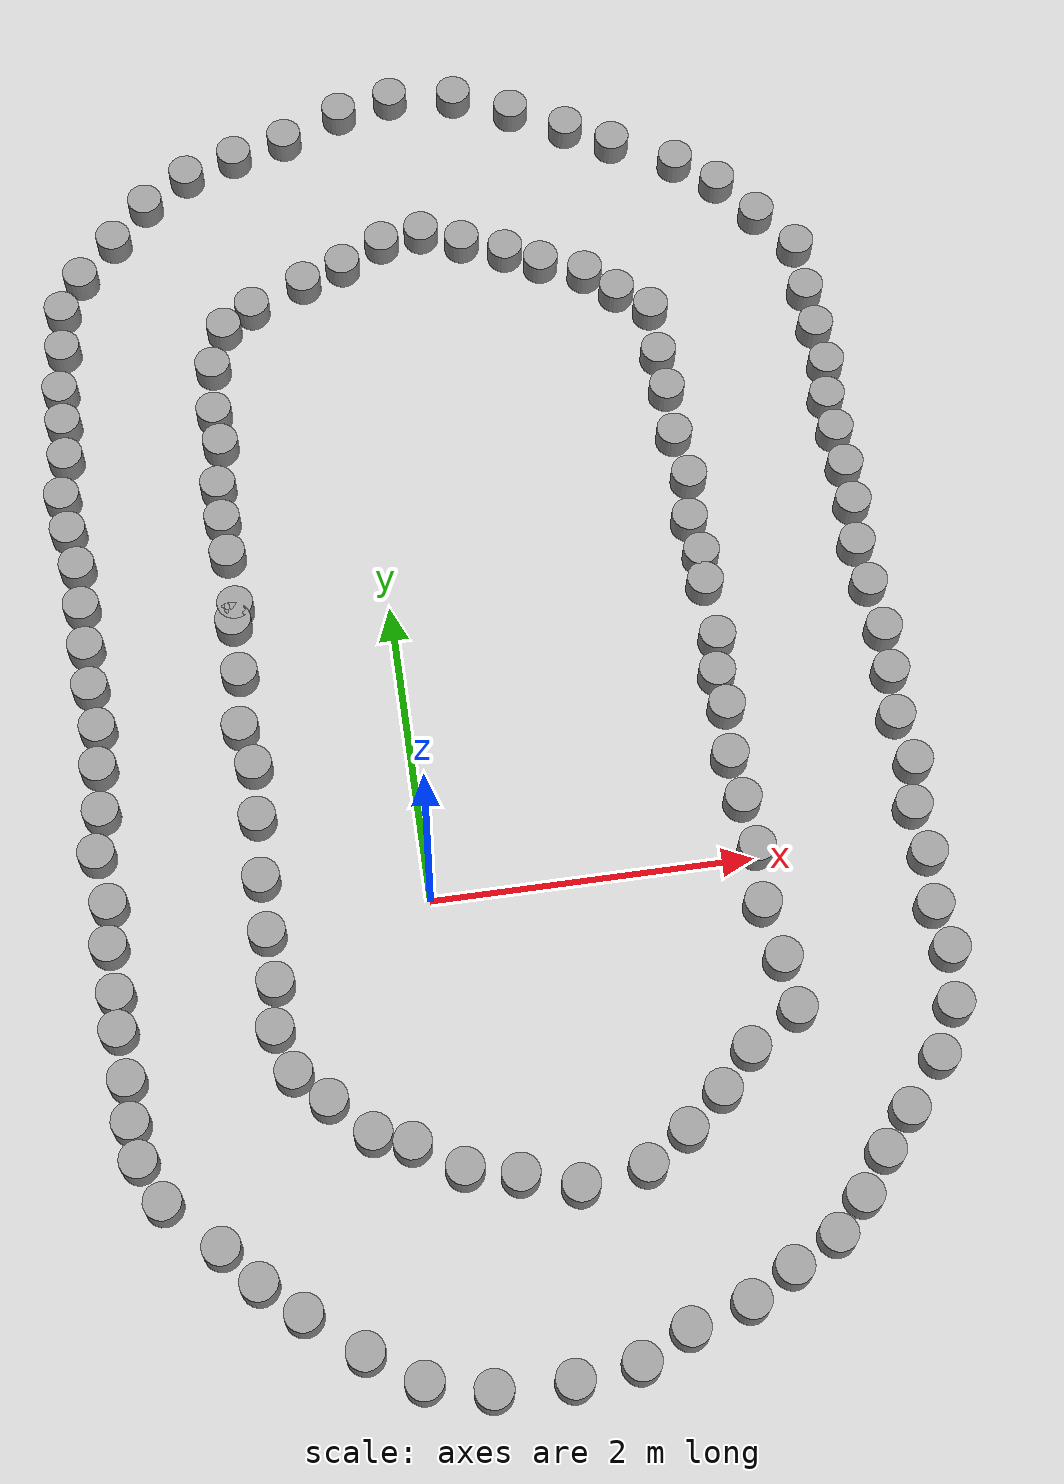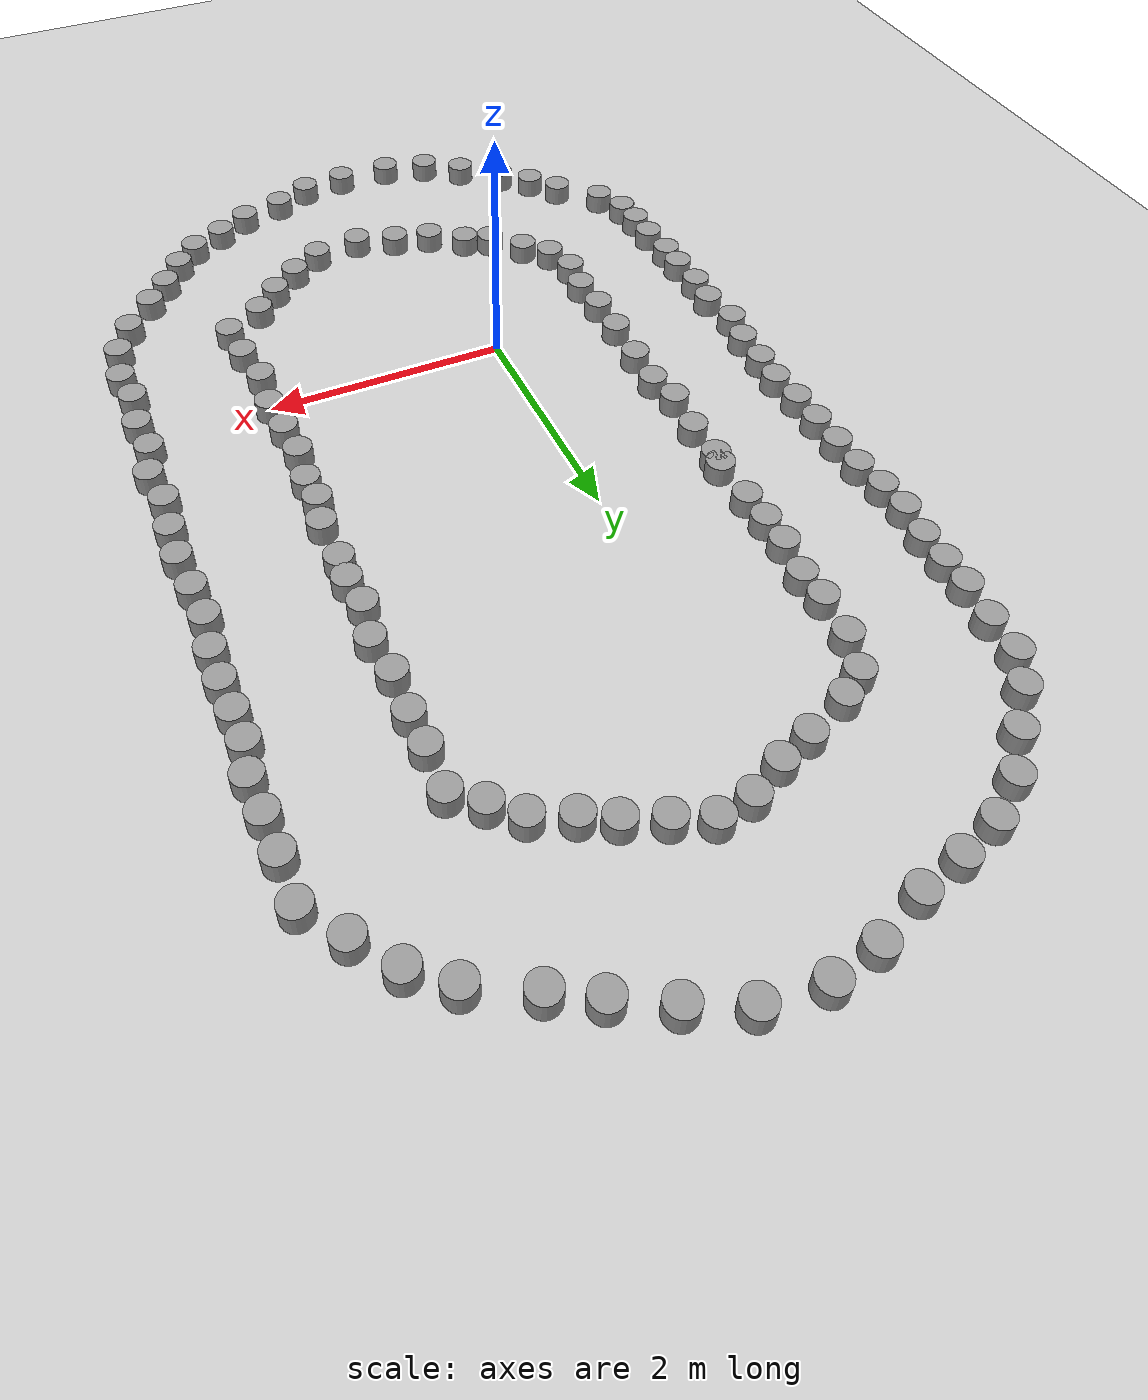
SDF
<sdf version="1.6">
 <world name="default">
  <light name="sun" type="directional">
   <pose>0 0 10 0 -0 0</pose>
   <diffuse>0.8 0.8 0.8 1</diffuse>
   <specular>0.2 0.2 0.2 1</specular>
   <attenuation>
    <range>1000</range>
    <constant>0.9</constant>
    <linear>0.01</linear>
    <quadratic>0.001</quadratic>
   </attenuation>
   <direction>-0.5 0.1 -0.9</direction>
  </light>
  <model name="ground_plane">
   <static>1</static>
   <link name="link">
    <collision name="collision">
     <geometry><plane><normal>0 0 1</normal><size>100 100</size></plane></geometry>
     <surface>
      <contact><collide_bitmask>65535</collide_bitmask></contact>
      <friction><ode><mu>100</mu><mu2>50</mu2></ode></friction>
     </surface>
    </collision>
    <visual name="visual">
     <cast_shadows>0</cast_shadows>
     <geometry><plane><normal>0 0 1</normal><size>100 100</size></plane></geometry>
     <material>
      <script><uri>file://media/materials/scripts/gazebo.material</uri><name>Gazebo/Grey</name></script>
     </material>
    </visual>
   </link>
  </model>
  <gravity>0 0 -9.8</gravity>
  <magnetic_field>6e-06 2.3e-05 -4.2e-05</magnetic_field>
  <atmosphere type="adiabatic"/>
  <physics name="default_physics" default="0" type="ode">
   <max_step_size>0.001</max_step_size>
   <real_time_factor>1</real_time_factor>
   <real_time_update_rate>1000</real_time_update_rate>
  </physics>
  <scene><ambient>0.4 0.4 0.4 1</ambient><background>0.7 0.7 0.7 1</background><shadows>1</shadows></scene>
  <audio><device>default</device></audio>
  <spherical_coordinates>
   <surface_model>EARTH_WGS84</surface_model>
   <latitude_deg>0</latitude_deg>
   <longitude_deg>0</longitude_deg>
   <elevation>0</elevation>
   <heading_deg>0</heading_deg>
  </spherical_coordinates>
  <model name="pillar">
   <link name="link_0">
    <inertial>
     <mass>0.0172437</mass>
     <inertia>
      <ixx>0.000207925</ixx>
      <ixy>0</ixy>
      <ixz>0</ixz>
      <iyy>0.000207925</iyy>
      <iyz>0</iyz>
      <izz>0.000114861</izz>
     </inertia>
    </inertial>
    <pose>2e-06 -0 0 0 -0 0</pose>
    <visual name="visual">
     <geometry><cylinder><radius>0.115422</radius><length>0.32362</length></cylinder></geometry>
     <material>
      <lighting>1</lighting>
      <script><uri>file://media/materials/scripts/gazebo.material</uri><name>Gazebo/Grey</name></script>
      <shader type="vertex"><normal_map>__default__</normal_map></shader>
     </material>
    </visual>
    <collision name="collision">
     <geometry><cylinder><radius>0.115422</radius><length>0.32362</length></cylinder></geometry>
     <surface>
      <friction>
       <ode><mu>1</mu><mu2>1</mu2><fdir1>0 0 0</fdir1><slip1>0</slip1><slip2>0</slip2></ode>
       <torsional>
        <coefficient>1</coefficient>
        <patch_radius>0</patch_radius>
        <surface_radius>0</surface_radius>
        <use_patch_radius>1</use_patch_radius>
        <ode><slip>0</slip></ode>
       </torsional>
      </friction>
      <bounce><restitution_coefficient>0</restitution_coefficient><threshold>1e+06</threshold></bounce>
      <contact>
       <collide_without_contact>0</collide_without_contact>
       <collide_without_contact_bitmask>1</collide_without_contact_bitmask>
       <collide_bitmask>1</collide_bitmask>
       <ode>
        <soft_cfm>0</soft_cfm>
        <soft_erp>0.2</soft_erp>
        <kp>1e+13</kp>
        <kd>1</kd>
        <max_vel>0.01</max_vel>
        <min_depth>0</min_depth>
       </ode>
       <bullet>
        <split_impulse>1</split_impulse>
        <split_impulse_penetration_threshold>-0.01</split_impulse_penetration_threshold>
        <soft_cfm>0</soft_cfm>
        <soft_erp>0.2</soft_erp>
        <kp>1e+13</kp>
        <kd>1</kd>
       </bullet>
      </contact>
     </surface>
    </collision>
   </link>
   <static>1</static>
   <pose>-2.01154 3.05582 0 0 -0 0</pose>
  </model>
  <model name="pillar_clone">
   <link name="link_0">
    <inertial>
     <mass>0.0172437</mass>
     <inertia>
      <ixx>0.000207925</ixx>
      <ixy>0</ixy>
      <ixz>0</ixz>
      <iyy>0.000207925</iyy>
      <iyz>0</iyz>
      <izz>0.000114861</izz>
     </inertia>
    </inertial>
    <pose>2e-06 -0 0 0 -0 0</pose>
    <visual name="visual">
     <geometry><cylinder><radius>0.115422</radius><length>0.32362</length></cylinder></geometry>
     <material>
      <lighting>1</lighting>
      <script><uri>file://media/materials/scripts/gazebo.material</uri><name>Gazebo/Grey</name></script>
      <shader type="vertex"><normal_map>__default__</normal_map></shader>
     </material>
    </visual>
    <collision name="collision">
     <geometry><cylinder><radius>0.115422</radius><length>0.32362</length></cylinder></geometry>
     <surface>
      <friction>
       <ode><mu>1</mu><mu2>1</mu2><fdir1>0 0 0</fdir1><slip1>0</slip1><slip2>0</slip2></ode>
       <torsional>
        <coefficient>1</coefficient>
        <patch_radius>0</patch_radius>
        <surface_radius>0</surface_radius>
        <use_patch_radius>1</use_patch_radius>
        <ode><slip>0</slip></ode>
       </torsional>
      </friction>
      <bounce><restitution_coefficient>0</restitution_coefficient><threshold>1e+06</threshold></bounce>
      <contact>
       <collide_without_contact>0</collide_without_contact>
       <collide_without_contact_bitmask>1</collide_without_contact_bitmask>
       <collide_bitmask>1</collide_bitmask>
       <ode>
        <soft_cfm>0</soft_cfm>
        <soft_erp>0.2</soft_erp>
        <kp>1e+13</kp>
        <kd>1</kd>
        <max_vel>0.01</max_vel>
        <min_depth>0</min_depth>
       </ode>
       <bullet>
        <split_impulse>1</split_impulse>
        <split_impulse_penetration_threshold>-0.01</split_impulse_penetration_threshold>
        <soft_cfm>0</soft_cfm>
        <soft_erp>0.2</soft_erp>
        <kp>1e+13</kp>
        <kd>1</kd>
       </bullet>
      </contact>
     </surface>
    </collision>
   </link>
   <static>1</static>
   <pose>-1.99112 2.80091 0 0 -0 0</pose>
  </model>
  <model name="pillar_clone_0">
   <link name="link_0">
    <inertial>
     <mass>0.0172437</mass>
     <inertia>
      <ixx>0.000207925</ixx>
      <ixy>0</ixy>
      <ixz>0</ixz>
      <iyy>0.000207925</iyy>
      <iyz>0</iyz>
      <izz>0.000114861</izz>
     </inertia>
    </inertial>
    <pose>2e-06 -0 0 0 -0 0</pose>
    <visual name="visual">
     <geometry><cylinder><radius>0.115422</radius><length>0.32362</length></cylinder></geometry>
     <material>
      <lighting>1</lighting>
      <script><uri>file://media/materials/scripts/gazebo.material</uri><name>Gazebo/Grey</name></script>
      <shader type="vertex"><normal_map>__default__</normal_map></shader>
     </material>
    </visual>
    <collision name="collision">
     <geometry><cylinder><radius>0.115422</radius><length>0.32362</length></cylinder></geometry>
     <surface>
      <friction>
       <ode><mu>1</mu><mu2>1</mu2><fdir1>0 0 0</fdir1><slip1>0</slip1><slip2>0</slip2></ode>
       <torsional>
        <coefficient>1</coefficient>
        <patch_radius>0</patch_radius>
        <surface_radius>0</surface_radius>
        <use_patch_radius>1</use_patch_radius>
        <ode><slip>0</slip></ode>
       </torsional>
      </friction>
      <bounce><restitution_coefficient>0</restitution_coefficient><threshold>1e+06</threshold></bounce>
      <contact>
       <collide_without_contact>0</collide_without_contact>
       <collide_without_contact_bitmask>1</collide_without_contact_bitmask>
       <collide_bitmask>1</collide_bitmask>
       <ode>
        <soft_cfm>0</soft_cfm>
        <soft_erp>0.2</soft_erp>
        <kp>1e+13</kp>
        <kd>1</kd>
        <max_vel>0.01</max_vel>
        <min_depth>0</min_depth>
       </ode>
       <bullet>
        <split_impulse>1</split_impulse>
        <split_impulse_penetration_threshold>-0.01</split_impulse_penetration_threshold>
        <soft_cfm>0</soft_cfm>
        <soft_erp>0.2</soft_erp>
        <kp>1e+13</kp>
        <kd>1</kd>
       </bullet>
      </contact>
     </surface>
    </collision>
   </link>
   <static>1</static>
   <pose>-1.95249 2.53371 0 0 -0 0</pose>
  </model>
  <model name="pillar_clone_1">
   <link name="link_0">
    <inertial>
     <mass>0.0172437</mass>
     <inertia>
      <ixx>0.000207925</ixx>
      <ixy>0</ixy>
      <ixz>0</ixz>
      <iyy>0.000207925</iyy>
      <iyz>0</iyz>
      <izz>0.000114861</izz>
     </inertia>
    </inertial>
    <pose>2e-06 -0 0 0 -0 0</pose>
    <visual name="visual">
     <geometry><cylinder><radius>0.115422</radius><length>0.32362</length></cylinder></geometry>
     <material>
      <lighting>1</lighting>
      <script><uri>file://media/materials/scripts/gazebo.material</uri><name>Gazebo/Grey</name></script>
      <shader type="vertex"><normal_map>__default__</normal_map></shader>
     </material>
    </visual>
    <collision name="collision">
     <geometry><cylinder><radius>0.115422</radius><length>0.32362</length></cylinder></geometry>
     <surface>
      <friction>
       <ode><mu>1</mu><mu2>1</mu2><fdir1>0 0 0</fdir1><slip1>0</slip1><slip2>0</slip2></ode>
       <torsional>
        <coefficient>1</coefficient>
        <patch_radius>0</patch_radius>
        <surface_radius>0</surface_radius>
        <use_patch_radius>1</use_patch_radius>
        <ode><slip>0</slip></ode>
       </torsional>
      </friction>
      <bounce><restitution_coefficient>0</restitution_coefficient><threshold>1e+06</threshold></bounce>
      <contact>
       <collide_without_contact>0</collide_without_contact>
       <collide_without_contact_bitmask>1</collide_without_contact_bitmask>
       <collide_bitmask>1</collide_bitmask>
       <ode>
        <soft_cfm>0</soft_cfm>
        <soft_erp>0.2</soft_erp>
        <kp>1e+13</kp>
        <kd>1</kd>
        <max_vel>0.01</max_vel>
        <min_depth>0</min_depth>
       </ode>
       <bullet>
        <split_impulse>1</split_impulse>
        <split_impulse_penetration_threshold>-0.01</split_impulse_penetration_threshold>
        <soft_cfm>0</soft_cfm>
        <soft_erp>0.2</soft_erp>
        <kp>1e+13</kp>
        <kd>1</kd>
       </bullet>
      </contact>
     </surface>
    </collision>
   </link>
   <static>1</static>
   <pose>-1.9471 2.24459 0 0 -0 0</pose>
  </model>
  <model name="pillar_clone_2">
   <link name="link_0">
    <inertial>
     <mass>0.0172437</mass>
     <inertia>
      <ixx>0.000207925</ixx>
      <ixy>0</ixy>
      <ixz>0</ixz>
      <iyy>0.000207925</iyy>
      <iyz>0</iyz>
      <izz>0.000114861</izz>
     </inertia>
    </inertial>
    <pose>2e-06 -0 0 0 -0 0</pose>
    <visual name="visual">
     <geometry><cylinder><radius>0.115422</radius><length>0.32362</length></cylinder></geometry>
     <material>
      <lighting>1</lighting>
      <script><uri>file://media/materials/scripts/gazebo.material</uri><name>Gazebo/Grey</name></script>
      <shader type="vertex"><normal_map>__default__</normal_map></shader>
     </material>
    </visual>
    <collision name="collision">
     <geometry><cylinder><radius>0.115422</radius><length>0.32362</length></cylinder></geometry>
     <surface>
      <friction>
       <ode><mu>1</mu><mu2>1</mu2><fdir1>0 0 0</fdir1><slip1>0</slip1><slip2>0</slip2></ode>
       <torsional>
        <coefficient>1</coefficient>
        <patch_radius>0</patch_radius>
        <surface_radius>0</surface_radius>
        <use_patch_radius>1</use_patch_radius>
        <ode><slip>0</slip></ode>
       </torsional>
      </friction>
      <bounce><restitution_coefficient>0</restitution_coefficient><threshold>1e+06</threshold></bounce>
      <contact>
       <collide_without_contact>0</collide_without_contact>
       <collide_without_contact_bitmask>1</collide_without_contact_bitmask>
       <collide_bitmask>1</collide_bitmask>
       <ode>
        <soft_cfm>0</soft_cfm>
        <soft_erp>0.2</soft_erp>
        <kp>1e+13</kp>
        <kd>1</kd>
        <max_vel>0.01</max_vel>
        <min_depth>0</min_depth>
       </ode>
       <bullet>
        <split_impulse>1</split_impulse>
        <split_impulse_penetration_threshold>-0.01</split_impulse_penetration_threshold>
        <soft_cfm>0</soft_cfm>
        <soft_erp>0.2</soft_erp>
        <kp>1e+13</kp>
        <kd>1</kd>
       </bullet>
      </contact>
     </surface>
    </collision>
   </link>
   <static>1</static>
   <pose>-1.94177 1.95842 0 0 -0 0</pose>
  </model>
  <model name="pillar_clone_3">
   <link name="link_0">
    <inertial>
     <mass>0.0172437</mass>
     <inertia>
      <ixx>0.000207925</ixx>
      <ixy>0</ixy>
      <ixz>0</ixz>
      <iyy>0.000207925</iyy>
      <iyz>0</iyz>
      <izz>0.000114861</izz>
     </inertia>
    </inertial>
    <pose>2e-06 -0 0 0 -0 0</pose>
    <visual name="visual">
     <geometry><cylinder><radius>0.115422</radius><length>0.32362</length></cylinder></geometry>
     <material>
      <lighting>1</lighting>
      <script><uri>file://media/materials/scripts/gazebo.material</uri><name>Gazebo/Grey</name></script>
      <shader type="vertex"><normal_map>__default__</normal_map></shader>
     </material>
    </visual>
    <collision name="collision">
     <geometry><cylinder><radius>0.115422</radius><length>0.32362</length></cylinder></geometry>
     <surface>
      <friction>
       <ode><mu>1</mu><mu2>1</mu2><fdir1>0 0 0</fdir1><slip1>0</slip1><slip2>0</slip2></ode>
       <torsional>
        <coefficient>1</coefficient>
        <patch_radius>0</patch_radius>
        <surface_radius>0</surface_radius>
        <use_patch_radius>1</use_patch_radius>
        <ode><slip>0</slip></ode>
       </torsional>
      </friction>
      <bounce><restitution_coefficient>0</restitution_coefficient><threshold>1e+06</threshold></bounce>
      <contact>
       <collide_without_contact>0</collide_without_contact>
       <collide_without_contact_bitmask>1</collide_without_contact_bitmask>
       <collide_bitmask>1</collide_bitmask>
       <ode>
        <soft_cfm>0</soft_cfm>
        <soft_erp>0.2</soft_erp>
        <kp>1e+13</kp>
        <kd>1</kd>
        <max_vel>0.01</max_vel>
        <min_depth>0</min_depth>
       </ode>
       <bullet>
        <split_impulse>1</split_impulse>
        <split_impulse_penetration_threshold>-0.01</split_impulse_penetration_threshold>
        <soft_cfm>0</soft_cfm>
        <soft_erp>0.2</soft_erp>
        <kp>1e+13</kp>
        <kd>1</kd>
       </bullet>
      </contact>
     </surface>
    </collision>
   </link>
   <static>1</static>
   <pose>-1.93622 1.67516 0 0 -0 0</pose>
  </model>
  <model name="pillar_clone_4">
   <link name="link_0">
    <inertial>
     <mass>0.0172437</mass>
     <inertia>
      <ixx>0.000207925</ixx>
      <ixy>0</ixy>
      <ixz>0</ixz>
      <iyy>0.000207925</iyy>
      <iyz>0</iyz>
      <izz>0.000114861</izz>
     </inertia>
    </inertial>
    <pose>2e-06 -0 0 0 -0 0</pose>
    <visual name="visual">
     <geometry><cylinder><radius>0.115422</radius><length>0.32362</length></cylinder></geometry>
     <material>
      <lighting>1</lighting>
      <script><uri>file://media/materials/scripts/gazebo.material</uri><name>Gazebo/Grey</name></script>
      <shader type="vertex"><normal_map>__default__</normal_map></shader>
     </material>
    </visual>
    <collision name="collision">
     <geometry><cylinder><radius>0.115422</radius><length>0.32362</length></cylinder></geometry>
     <surface>
      <friction>
       <ode><mu>1</mu><mu2>1</mu2><fdir1>0 0 0</fdir1><slip1>0</slip1><slip2>0</slip2></ode>
       <torsional>
        <coefficient>1</coefficient>
        <patch_radius>0</patch_radius>
        <surface_radius>0</surface_radius>
        <use_patch_radius>1</use_patch_radius>
        <ode><slip>0</slip></ode>
       </torsional>
      </friction>
      <bounce><restitution_coefficient>0</restitution_coefficient><threshold>1e+06</threshold></bounce>
      <contact>
       <collide_without_contact>0</collide_without_contact>
       <collide_without_contact_bitmask>1</collide_without_contact_bitmask>
       <collide_bitmask>1</collide_bitmask>
       <ode>
        <soft_cfm>0</soft_cfm>
        <soft_erp>0.2</soft_erp>
        <kp>1e+13</kp>
        <kd>1</kd>
        <max_vel>0.01</max_vel>
        <min_depth>0</min_depth>
       </ode>
       <bullet>
        <split_impulse>1</split_impulse>
        <split_impulse_penetration_threshold>-0.01</split_impulse_penetration_threshold>
        <soft_cfm>0</soft_cfm>
        <soft_erp>0.2</soft_erp>
        <kp>1e+13</kp>
        <kd>1</kd>
       </bullet>
      </contact>
     </surface>
    </collision>
   </link>
   <static>1</static>
   <pose>-1.91045 1.38722 0 0 -0 0</pose>
  </model>
  <model name="pillar_clone_5">
   <link name="link_0">
    <inertial>
     <mass>0.0172437</mass>
     <inertia>
      <ixx>0.000207925</ixx>
      <ixy>0</ixy>
      <ixz>0</ixz>
      <iyy>0.000207925</iyy>
      <iyz>0</iyz>
      <izz>0.000114861</izz>
     </inertia>
    </inertial>
    <pose>2e-06 -0 0 0 -0 0</pose>
    <visual name="visual">
     <geometry><cylinder><radius>0.115422</radius><length>0.32362</length></cylinder></geometry>
     <material>
      <lighting>1</lighting>
      <script><uri>file://media/materials/scripts/gazebo.material</uri><name>Gazebo/Grey</name></script>
      <shader type="vertex"><normal_map>__default__</normal_map></shader>
     </material>
    </visual>
    <collision name="collision">
     <geometry><cylinder><radius>0.115422</radius><length>0.32362</length></cylinder></geometry>
     <surface>
      <friction>
       <ode><mu>1</mu><mu2>1</mu2><fdir1>0 0 0</fdir1><slip1>0</slip1><slip2>0</slip2></ode>
       <torsional>
        <coefficient>1</coefficient>
        <patch_radius>0</patch_radius>
        <surface_radius>0</surface_radius>
        <use_patch_radius>1</use_patch_radius>
        <ode><slip>0</slip></ode>
       </torsional>
      </friction>
      <bounce><restitution_coefficient>0</restitution_coefficient><threshold>1e+06</threshold></bounce>
      <contact>
       <collide_without_contact>0</collide_without_contact>
       <collide_without_contact_bitmask>1</collide_without_contact_bitmask>
       <collide_bitmask>1</collide_bitmask>
       <ode>
        <soft_cfm>0</soft_cfm>
        <soft_erp>0.2</soft_erp>
        <kp>1e+13</kp>
        <kd>1</kd>
        <max_vel>0.01</max_vel>
        <min_depth>0</min_depth>
       </ode>
       <bullet>
        <split_impulse>1</split_impulse>
        <split_impulse_penetration_threshold>-0.01</split_impulse_penetration_threshold>
        <soft_cfm>0</soft_cfm>
        <soft_erp>0.2</soft_erp>
        <kp>1e+13</kp>
        <kd>1</kd>
       </bullet>
      </contact>
     </surface>
    </collision>
   </link>
   <static>1</static>
   <pose>-1.92724 1.12302 0 0 -0 0</pose>
  </model>
  <model name="pillar_clone_6">
   <link name="link_0">
    <inertial>
     <mass>0.0172437</mass>
     <inertia>
      <ixx>0.000207925</ixx>
      <ixy>0</ixy>
      <ixz>0</ixz>
      <iyy>0.000207925</iyy>
      <iyz>0</iyz>
      <izz>0.000114861</izz>
     </inertia>
    </inertial>
    <pose>2e-06 -0 0 0 -0 0</pose>
    <visual name="visual">
     <geometry><cylinder><radius>0.115422</radius><length>0.32362</length></cylinder></geometry>
     <material>
      <lighting>1</lighting>
      <script><uri>file://media/materials/scripts/gazebo.material</uri><name>Gazebo/Grey</name></script>
      <shader type="vertex"><normal_map>__default__</normal_map></shader>
     </material>
    </visual>
    <collision name="collision">
     <geometry><cylinder><radius>0.115422</radius><length>0.32362</length></cylinder></geometry>
     <surface>
      <friction>
       <ode><mu>1</mu><mu2>1</mu2><fdir1>0 0 0</fdir1><slip1>0</slip1><slip2>0</slip2></ode>
       <torsional>
        <coefficient>1</coefficient>
        <patch_radius>0</patch_radius>
        <surface_radius>0</surface_radius>
        <use_patch_radius>1</use_patch_radius>
        <ode><slip>0</slip></ode>
       </torsional>
      </friction>
      <bounce><restitution_coefficient>0</restitution_coefficient><threshold>1e+06</threshold></bounce>
      <contact>
       <collide_without_contact>0</collide_without_contact>
       <collide_without_contact_bitmask>1</collide_without_contact_bitmask>
       <collide_bitmask>1</collide_bitmask>
       <ode>
        <soft_cfm>0</soft_cfm>
        <soft_erp>0.2</soft_erp>
        <kp>1e+13</kp>
        <kd>1</kd>
        <max_vel>0.01</max_vel>
        <min_depth>0</min_depth>
       </ode>
       <bullet>
        <split_impulse>1</split_impulse>
        <split_impulse_penetration_threshold>-0.01</split_impulse_penetration_threshold>
        <soft_cfm>0</soft_cfm>
        <soft_erp>0.2</soft_erp>
        <kp>1e+13</kp>
        <kd>1</kd>
       </bullet>
      </contact>
     </surface>
    </collision>
   </link>
   <static>1</static>
   <pose>-1.93349 0.821144 0 0 -0 0</pose>
  </model>
  <model name="pillar_clone_7">
   <link name="link_0">
    <inertial>
     <mass>0.0172437</mass>
     <inertia>
      <ixx>0.000207925</ixx>
      <ixy>0</ixy>
      <ixz>0</ixz>
      <iyy>0.000207925</iyy>
      <iyz>0</iyz>
      <izz>0.000114861</izz>
     </inertia>
    </inertial>
    <pose>2e-06 -0 0 0 -0 0</pose>
    <visual name="visual">
     <geometry><cylinder><radius>0.115422</radius><length>0.32362</length></cylinder></geometry>
     <material>
      <lighting>1</lighting>
      <script><uri>file://media/materials/scripts/gazebo.material</uri><name>Gazebo/Grey</name></script>
      <shader type="vertex"><normal_map>__default__</normal_map></shader>
     </material>
    </visual>
    <collision name="collision">
     <geometry><cylinder><radius>0.115422</radius><length>0.32362</length></cylinder></geometry>
     <surface>
      <friction>
       <ode><mu>1</mu><mu2>1</mu2><fdir1>0 0 0</fdir1><slip1>0</slip1><slip2>0</slip2></ode>
       <torsional>
        <coefficient>1</coefficient>
        <patch_radius>0</patch_radius>
        <surface_radius>0</surface_radius>
        <use_patch_radius>1</use_patch_radius>
        <ode><slip>0</slip></ode>
       </torsional>
      </friction>
      <bounce><restitution_coefficient>0</restitution_coefficient><threshold>1e+06</threshold></bounce>
      <contact>
       <collide_without_contact>0</collide_without_contact>
       <collide_without_contact_bitmask>1</collide_without_contact_bitmask>
       <collide_bitmask>1</collide_bitmask>
       <ode>
        <soft_cfm>0</soft_cfm>
        <soft_erp>0.2</soft_erp>
        <kp>1e+13</kp>
        <kd>1</kd>
        <max_vel>0.01</max_vel>
        <min_depth>0</min_depth>
       </ode>
       <bullet>
        <split_impulse>1</split_impulse>
        <split_impulse_penetration_threshold>-0.01</split_impulse_penetration_threshold>
        <soft_cfm>0</soft_cfm>
        <soft_erp>0.2</soft_erp>
        <kp>1e+13</kp>
        <kd>1</kd>
       </bullet>
      </contact>
     </surface>
    </collision>
   </link>
   <static>1</static>
   <pose>-1.98154 0.546224 0 0 -0 0</pose>
  </model>
  <model name="pillar_clone_8">
   <link name="link_0">
    <inertial>
     <mass>0.0172437</mass>
     <inertia>
      <ixx>0.000207925</ixx>
      <ixy>0</ixy>
      <ixz>0</ixz>
      <iyy>0.000207925</iyy>
      <iyz>0</iyz>
      <izz>0.000114861</izz>
     </inertia>
    </inertial>
    <pose>2e-06 -0 0 0 -0 0</pose>
    <visual name="visual">
     <geometry><cylinder><radius>0.115422</radius><length>0.32362</length></cylinder></geometry>
     <material>
      <lighting>1</lighting>
      <script><uri>file://media/materials/scripts/gazebo.material</uri><name>Gazebo/Grey</name></script>
      <shader type="vertex"><normal_map>__default__</normal_map></shader>
     </material>
    </visual>
    <collision name="collision">
     <geometry><cylinder><radius>0.115422</radius><length>0.32362</length></cylinder></geometry>
     <surface>
      <friction>
       <ode><mu>1</mu><mu2>1</mu2><fdir1>0 0 0</fdir1><slip1>0</slip1><slip2>0</slip2></ode>
       <torsional>
        <coefficient>1</coefficient>
        <patch_radius>0</patch_radius>
        <surface_radius>0</surface_radius>
        <use_patch_radius>1</use_patch_radius>
        <ode><slip>0</slip></ode>
       </torsional>
      </friction>
      <bounce><restitution_coefficient>0</restitution_coefficient><threshold>1e+06</threshold></bounce>
      <contact>
       <collide_without_contact>0</collide_without_contact>
       <collide_without_contact_bitmask>1</collide_without_contact_bitmask>
       <collide_bitmask>1</collide_bitmask>
       <ode>
        <soft_cfm>0</soft_cfm>
        <soft_erp>0.2</soft_erp>
        <kp>1e+13</kp>
        <kd>1</kd>
        <max_vel>0.01</max_vel>
        <min_depth>0</min_depth>
       </ode>
       <bullet>
        <split_impulse>1</split_impulse>
        <split_impulse_penetration_threshold>-0.01</split_impulse_penetration_threshold>
        <soft_cfm>0</soft_cfm>
        <soft_erp>0.2</soft_erp>
        <kp>1e+13</kp>
        <kd>1</kd>
       </bullet>
      </contact>
     </surface>
    </collision>
   </link>
   <static>1</static>
   <pose>-1.93324 0.214347 0 0 -0 0</pose>
  </model>
  <model name="pillar_clone_9">
   <link name="link_0">
    <inertial>
     <mass>0.0172437</mass>
     <inertia>
      <ixx>0.000207925</ixx>
      <ixy>0</ixy>
      <ixz>0</ixz>
      <iyy>0.000207925</iyy>
      <iyz>0</iyz>
      <izz>0.000114861</izz>
     </inertia>
    </inertial>
    <pose>2e-06 -0 0 0 -0 0</pose>
    <visual name="visual">
     <geometry><cylinder><radius>0.115422</radius><length>0.32362</length></cylinder></geometry>
     <material>
      <lighting>1</lighting>
      <script><uri>file://media/materials/scripts/gazebo.material</uri><name>Gazebo/Grey</name></script>
      <shader type="vertex"><normal_map>__default__</normal_map></shader>
     </material>
    </visual>
    <collision name="collision">
     <geometry><cylinder><radius>0.115422</radius><length>0.32362</length></cylinder></geometry>
     <surface>
      <friction>
       <ode><mu>1</mu><mu2>1</mu2><fdir1>0 0 0</fdir1><slip1>0</slip1><slip2>0</slip2></ode>
       <torsional>
        <coefficient>1</coefficient>
        <patch_radius>0</patch_radius>
        <surface_radius>0</surface_radius>
        <use_patch_radius>1</use_patch_radius>
        <ode><slip>0</slip></ode>
       </torsional>
      </friction>
      <bounce><restitution_coefficient>0</restitution_coefficient><threshold>1e+06</threshold></bounce>
      <contact>
       <collide_without_contact>0</collide_without_contact>
       <collide_without_contact_bitmask>1</collide_without_contact_bitmask>
       <collide_bitmask>1</collide_bitmask>
       <ode>
        <soft_cfm>0</soft_cfm>
        <soft_erp>0.2</soft_erp>
        <kp>1e+13</kp>
        <kd>1</kd>
        <max_vel>0.01</max_vel>
        <min_depth>0</min_depth>
       </ode>
       <bullet>
        <split_impulse>1</split_impulse>
        <split_impulse_penetration_threshold>-0.01</split_impulse_penetration_threshold>
        <soft_cfm>0</soft_cfm>
        <soft_erp>0.2</soft_erp>
        <kp>1e+13</kp>
        <kd>1</kd>
       </bullet>
      </contact>
     </surface>
    </collision>
   </link>
   <static>1</static>
   <pose>-1.9547 -0.052114 0 0 -0 0</pose>
  </model>
  <model name="pillar_clone_10">
   <link name="link_0">
    <inertial>
     <mass>0.0172437</mass>
     <inertia>
      <ixx>0.000207925</ixx>
      <ixy>0</ixy>
      <ixz>0</ixz>
      <iyy>0.000207925</iyy>
      <iyz>0</iyz>
      <izz>0.000114861</izz>
     </inertia>
    </inertial>
    <pose>2e-06 -0 0 0 -0 0</pose>
    <visual name="visual">
     <geometry><cylinder><radius>0.115422</radius><length>0.32362</length></cylinder></geometry>
     <material>
      <lighting>1</lighting>
      <script><uri>file://media/materials/scripts/gazebo.material</uri><name>Gazebo/Grey</name></script>
      <shader type="vertex"><normal_map>__default__</normal_map></shader>
     </material>
    </visual>
    <collision name="collision">
     <geometry><cylinder><radius>0.115422</radius><length>0.32362</length></cylinder></geometry>
     <surface>
      <friction>
       <ode><mu>1</mu><mu2>1</mu2><fdir1>0 0 0</fdir1><slip1>0</slip1><slip2>0</slip2></ode>
       <torsional>
        <coefficient>1</coefficient>
        <patch_radius>0</patch_radius>
        <surface_radius>0</surface_radius>
        <use_patch_radius>1</use_patch_radius>
        <ode><slip>0</slip></ode>
       </torsional>
      </friction>
      <bounce><restitution_coefficient>0</restitution_coefficient><threshold>1e+06</threshold></bounce>
      <contact>
       <collide_without_contact>0</collide_without_contact>
       <collide_without_contact_bitmask>1</collide_without_contact_bitmask>
       <collide_bitmask>1</collide_bitmask>
       <ode>
        <soft_cfm>0</soft_cfm>
        <soft_erp>0.2</soft_erp>
        <kp>1e+13</kp>
        <kd>1</kd>
        <max_vel>0.01</max_vel>
        <min_depth>0</min_depth>
       </ode>
       <bullet>
        <split_impulse>1</split_impulse>
        <split_impulse_penetration_threshold>-0.01</split_impulse_penetration_threshold>
        <soft_cfm>0</soft_cfm>
        <soft_erp>0.2</soft_erp>
        <kp>1e+13</kp>
        <kd>1</kd>
       </bullet>
      </contact>
     </surface>
    </collision>
   </link>
   <static>1</static>
   <pose>-1.93858 -0.358246 0 0 -0 0</pose>
  </model>
  <model name="pillar_clone_11">
   <link name="link_0">
    <inertial>
     <mass>0.0172437</mass>
     <inertia>
      <ixx>0.000207925</ixx>
      <ixy>0</ixy>
      <ixz>0</ixz>
      <iyy>0.000207925</iyy>
      <iyz>0</iyz>
      <izz>0.000114861</izz>
     </inertia>
    </inertial>
    <pose>2e-06 -0 0 0 -0 0</pose>
    <visual name="visual">
     <geometry><cylinder><radius>0.115422</radius><length>0.32362</length></cylinder></geometry>
     <material>
      <lighting>1</lighting>
      <script><uri>file://media/materials/scripts/gazebo.material</uri><name>Gazebo/Grey</name></script>
      <shader type="vertex"><normal_map>__default__</normal_map></shader>
     </material>
    </visual>
    <collision name="collision">
     <geometry><cylinder><radius>0.115422</radius><length>0.32362</length></cylinder></geometry>
     <surface>
      <friction>
       <ode><mu>1</mu><mu2>1</mu2><fdir1>0 0 0</fdir1><slip1>0</slip1><slip2>0</slip2></ode>
       <torsional>
        <coefficient>1</coefficient>
        <patch_radius>0</patch_radius>
        <surface_radius>0</surface_radius>
        <use_patch_radius>1</use_patch_radius>
        <ode><slip>0</slip></ode>
       </torsional>
      </friction>
      <bounce><restitution_coefficient>0</restitution_coefficient><threshold>1e+06</threshold></bounce>
      <contact>
       <collide_without_contact>0</collide_without_contact>
       <collide_without_contact_bitmask>1</collide_without_contact_bitmask>
       <collide_bitmask>1</collide_bitmask>
       <ode>
        <soft_cfm>0</soft_cfm>
        <soft_erp>0.2</soft_erp>
        <kp>1e+13</kp>
        <kd>1</kd>
        <max_vel>0.01</max_vel>
        <min_depth>0</min_depth>
       </ode>
       <bullet>
        <split_impulse>1</split_impulse>
        <split_impulse_penetration_threshold>-0.01</split_impulse_penetration_threshold>
        <soft_cfm>0</soft_cfm>
        <soft_erp>0.2</soft_erp>
        <kp>1e+13</kp>
        <kd>1</kd>
       </bullet>
      </contact>
     </surface>
    </collision>
   </link>
   <static>1</static>
   <pose>-1.94131 -0.588095 0 0 -0 0</pose>
  </model>
  <model name="pillar_clone_12">
   <link name="link_0">
    <inertial>
     <mass>0.0172437</mass>
     <inertia>
      <ixx>0.000207925</ixx>
      <ixy>0</ixy>
      <ixz>0</ixz>
      <iyy>0.000207925</iyy>
      <iyz>0</iyz>
      <izz>0.000114861</izz>
     </inertia>
    </inertial>
    <pose>2e-06 -0 0 0 -0 0</pose>
    <visual name="visual">
     <geometry><cylinder><radius>0.115422</radius><length>0.32362</length></cylinder></geometry>
     <material>
      <lighting>1</lighting>
      <script><uri>file://media/materials/scripts/gazebo.material</uri><name>Gazebo/Grey</name></script>
      <shader type="vertex"><normal_map>__default__</normal_map></shader>
     </material>
    </visual>
    <collision name="collision">
     <geometry><cylinder><radius>0.115422</radius><length>0.32362</length></cylinder></geometry>
     <surface>
      <friction>
       <ode><mu>1</mu><mu2>1</mu2><fdir1>0 0 0</fdir1><slip1>0</slip1><slip2>0</slip2></ode>
       <torsional>
        <coefficient>1</coefficient>
        <patch_radius>0</patch_radius>
        <surface_radius>0</surface_radius>
        <use_patch_radius>1</use_patch_radius>
        <ode><slip>0</slip></ode>
       </torsional>
      </friction>
      <bounce><restitution_coefficient>0</restitution_coefficient><threshold>1e+06</threshold></bounce>
      <contact>
       <collide_without_contact>0</collide_without_contact>
       <collide_without_contact_bitmask>1</collide_without_contact_bitmask>
       <collide_bitmask>1</collide_bitmask>
       <ode>
        <soft_cfm>0</soft_cfm>
        <soft_erp>0.2</soft_erp>
        <kp>1e+13</kp>
        <kd>1</kd>
        <max_vel>0.01</max_vel>
        <min_depth>0</min_depth>
       </ode>
       <bullet>
        <split_impulse>1</split_impulse>
        <split_impulse_penetration_threshold>-0.01</split_impulse_penetration_threshold>
        <soft_cfm>0</soft_cfm>
        <soft_erp>0.2</soft_erp>
        <kp>1e+13</kp>
        <kd>1</kd>
       </bullet>
      </contact>
     </surface>
    </collision>
   </link>
   <static>1</static>
   <pose>-1.91538 -0.894045 0 0 -0 0</pose>
  </model>
  <model name="pillar_clone_13">
   <link name="link_0">
    <inertial>
     <mass>0.0172437</mass>
     <inertia>
      <ixx>0.000207925</ixx>
      <ixy>0</ixy>
      <ixz>0</ixz>
      <iyy>0.000207925</iyy>
      <iyz>0</iyz>
      <izz>0.000114861</izz>
     </inertia>
    </inertial>
    <pose>2e-06 -0 0 0 -0 0</pose>
    <visual name="visual">
     <geometry><cylinder><radius>0.115422</radius><length>0.32362</length></cylinder></geometry>
     <material>
      <lighting>1</lighting>
      <script><uri>file://media/materials/scripts/gazebo.material</uri><name>Gazebo/Grey</name></script>
      <shader type="vertex"><normal_map>__default__</normal_map></shader>
     </material>
    </visual>
    <collision name="collision">
     <geometry><cylinder><radius>0.115422</radius><length>0.32362</length></cylinder></geometry>
     <surface>
      <friction>
       <ode><mu>1</mu><mu2>1</mu2><fdir1>0 0 0</fdir1><slip1>0</slip1><slip2>0</slip2></ode>
       <torsional>
        <coefficient>1</coefficient>
        <patch_radius>0</patch_radius>
        <surface_radius>0</surface_radius>
        <use_patch_radius>1</use_patch_radius>
        <ode><slip>0</slip></ode>
       </torsional>
      </friction>
      <bounce><restitution_coefficient>0</restitution_coefficient><threshold>1e+06</threshold></bounce>
      <contact>
       <collide_without_contact>0</collide_without_contact>
       <collide_without_contact_bitmask>1</collide_without_contact_bitmask>
       <collide_bitmask>1</collide_bitmask>
       <ode>
        <soft_cfm>0</soft_cfm>
        <soft_erp>0.2</soft_erp>
        <kp>1e+13</kp>
        <kd>1</kd>
        <max_vel>0.01</max_vel>
        <min_depth>0</min_depth>
       </ode>
       <bullet>
        <split_impulse>1</split_impulse>
        <split_impulse_penetration_threshold>-0.01</split_impulse_penetration_threshold>
        <soft_cfm>0</soft_cfm>
        <soft_erp>0.2</soft_erp>
        <kp>1e+13</kp>
        <kd>1</kd>
       </bullet>
      </contact>
     </surface>
    </collision>
   </link>
   <static>1</static>
   <pose>-1.96524 3.85851 0 0 -0 0</pose>
  </model>
  <model name="pillar_clone_14">
   <link name="link_0">
    <inertial>
     <mass>0.0172437</mass>
     <inertia>
      <ixx>0.000207925</ixx>
      <ixy>0</ixy>
      <ixz>0</ixz>
      <iyy>0.000207925</iyy>
      <iyz>0</iyz>
      <izz>0.000114861</izz>
     </inertia>
    </inertial>
    <pose>2e-06 -0 0 0 -0 0</pose>
    <visual name="visual">
     <geometry><cylinder><radius>0.115422</radius><length>0.32362</length></cylinder></geometry>
     <material>
      <lighting>1</lighting>
      <script><uri>file://media/materials/scripts/gazebo.material</uri><name>Gazebo/Grey</name></script>
      <shader type="vertex"><normal_map>__default__</normal_map></shader>
     </material>
    </visual>
    <collision name="collision">
     <geometry><cylinder><radius>0.115422</radius><length>0.32362</length></cylinder></geometry>
     <surface>
      <friction>
       <ode><mu>1</mu><mu2>1</mu2><fdir1>0 0 0</fdir1><slip1>0</slip1><slip2>0</slip2></ode>
       <torsional>
        <coefficient>1</coefficient>
        <patch_radius>0</patch_radius>
        <surface_radius>0</surface_radius>
        <use_patch_radius>1</use_patch_radius>
        <ode><slip>0</slip></ode>
       </torsional>
      </friction>
      <bounce><restitution_coefficient>0</restitution_coefficient><threshold>1e+06</threshold></bounce>
      <contact>
       <collide_without_contact>0</collide_without_contact>
       <collide_without_contact_bitmask>1</collide_without_contact_bitmask>
       <collide_bitmask>1</collide_bitmask>
       <ode>
        <soft_cfm>0</soft_cfm>
        <soft_erp>0.2</soft_erp>
        <kp>1e+13</kp>
        <kd>1</kd>
        <max_vel>0.01</max_vel>
        <min_depth>0</min_depth>
       </ode>
       <bullet>
        <split_impulse>1</split_impulse>
        <split_impulse_penetration_threshold>-0.01</split_impulse_penetration_threshold>
        <soft_cfm>0</soft_cfm>
        <soft_erp>0.2</soft_erp>
        <kp>1e+13</kp>
        <kd>1</kd>
       </bullet>
      </contact>
     </surface>
    </collision>
   </link>
   <static>1</static>
   <pose>-1.96342 3.6093 0 0 -0 0</pose>
  </model>
  <model name="pillar_clone_15">
   <link name="link_0">
    <inertial>
     <mass>0.0172437</mass>
     <inertia>
      <ixx>0.000207925</ixx>
      <ixy>0</ixy>
      <ixz>0</ixz>
      <iyy>0.000207925</iyy>
      <iyz>0</iyz>
      <izz>0.000114861</izz>
     </inertia>
    </inertial>
    <pose>2e-06 -0 0 0 -0 0</pose>
    <visual name="visual">
     <geometry><cylinder><radius>0.115422</radius><length>0.32362</length></cylinder></geometry>
     <material>
      <lighting>1</lighting>
      <script><uri>file://media/materials/scripts/gazebo.material</uri><name>Gazebo/Grey</name></script>
      <shader type="vertex"><normal_map>__default__</normal_map></shader>
     </material>
    </visual>
    <collision name="collision">
     <geometry><cylinder><radius>0.115422</radius><length>0.32362</length></cylinder></geometry>
     <surface>
      <friction>
       <ode><mu>1</mu><mu2>1</mu2><fdir1>0 0 0</fdir1><slip1>0</slip1><slip2>0</slip2></ode>
       <torsional>
        <coefficient>1</coefficient>
        <patch_radius>0</patch_radius>
        <surface_radius>0</surface_radius>
        <use_patch_radius>1</use_patch_radius>
        <ode><slip>0</slip></ode>
       </torsional>
      </friction>
      <bounce><restitution_coefficient>0</restitution_coefficient><threshold>1e+06</threshold></bounce>
      <contact>
       <collide_without_contact>0</collide_without_contact>
       <collide_without_contact_bitmask>1</collide_without_contact_bitmask>
       <collide_bitmask>1</collide_bitmask>
       <ode>
        <soft_cfm>0</soft_cfm>
        <soft_erp>0.2</soft_erp>
        <kp>1e+13</kp>
        <kd>1</kd>
        <max_vel>0.01</max_vel>
        <min_depth>0</min_depth>
       </ode>
       <bullet>
        <split_impulse>1</split_impulse>
        <split_impulse_penetration_threshold>-0.01</split_impulse_penetration_threshold>
        <soft_cfm>0</soft_cfm>
        <soft_erp>0.2</soft_erp>
        <kp>1e+13</kp>
        <kd>1</kd>
       </bullet>
      </contact>
     </surface>
    </collision>
   </link>
   <static>1</static>
   <pose>-1.96782 3.34684 0 0 -0 0</pose>
  </model>
  <model name="pillar_clone_16">
   <link name="link_0">
    <inertial>
     <mass>0.0172437</mass>
     <inertia>
      <ixx>0.000207925</ixx>
      <ixy>0</ixy>
      <ixz>0</ixz>
      <iyy>0.000207925</iyy>
      <iyz>0</iyz>
      <izz>0.000114861</izz>
     </inertia>
    </inertial>
    <pose>2e-06 -0 0 0 -0 0</pose>
    <visual name="visual">
     <geometry><cylinder><radius>0.115422</radius><length>0.32362</length></cylinder></geometry>
     <material>
      <lighting>1</lighting>
      <script><uri>file://media/materials/scripts/gazebo.material</uri><name>Gazebo/Grey</name></script>
      <shader type="vertex"><normal_map>__default__</normal_map></shader>
     </material>
    </visual>
    <collision name="collision">
     <geometry><cylinder><radius>0.115422</radius><length>0.32362</length></cylinder></geometry>
     <surface>
      <friction>
       <ode><mu>1</mu><mu2>1</mu2><fdir1>0 0 0</fdir1><slip1>0</slip1><slip2>0</slip2></ode>
       <torsional>
        <coefficient>1</coefficient>
        <patch_radius>0</patch_radius>
        <surface_radius>0</surface_radius>
        <use_patch_radius>1</use_patch_radius>
        <ode><slip>0</slip></ode>
       </torsional>
      </friction>
      <bounce><restitution_coefficient>0</restitution_coefficient><threshold>1e+06</threshold></bounce>
      <contact>
       <collide_without_contact>0</collide_without_contact>
       <collide_without_contact_bitmask>1</collide_without_contact_bitmask>
       <collide_bitmask>1</collide_bitmask>
       <ode>
        <soft_cfm>0</soft_cfm>
        <soft_erp>0.2</soft_erp>
        <kp>1e+13</kp>
        <kd>1</kd>
        <max_vel>0.01</max_vel>
        <min_depth>0</min_depth>
       </ode>
       <bullet>
        <split_impulse>1</split_impulse>
        <split_impulse_penetration_threshold>-0.01</split_impulse_penetration_threshold>
        <soft_cfm>0</soft_cfm>
        <soft_erp>0.2</soft_erp>
        <kp>1e+13</kp>
        <kd>1</kd>
       </bullet>
      </contact>
     </surface>
    </collision>
   </link>
   <static>1</static>
   <pose>3.07066 3.97139 0 0 -0 0</pose>
  </model>
  <model name="pillar_clone_17">
   <link name="link_0">
    <inertial>
     <mass>0.0172437</mass>
     <inertia>
      <ixx>0.000207925</ixx>
      <ixy>0</ixy>
      <ixz>0</ixz>
      <iyy>0.000207925</iyy>
      <iyz>0</iyz>
      <izz>0.000114861</izz>
     </inertia>
    </inertial>
    <pose>2e-06 -0 0 0 -0 0</pose>
    <visual name="visual">
     <geometry><cylinder><radius>0.115422</radius><length>0.32362</length></cylinder></geometry>
     <material>
      <lighting>1</lighting>
      <script><uri>file://media/materials/scripts/gazebo.material</uri><name>Gazebo/Grey</name></script>
      <shader type="vertex"><normal_map>__default__</normal_map></shader>
     </material>
    </visual>
    <collision name="collision">
     <geometry><cylinder><radius>0.115422</radius><length>0.32362</length></cylinder></geometry>
     <surface>
      <friction>
       <ode><mu>1</mu><mu2>1</mu2><fdir1>0 0 0</fdir1><slip1>0</slip1><slip2>0</slip2></ode>
       <torsional>
        <coefficient>1</coefficient>
        <patch_radius>0</patch_radius>
        <surface_radius>0</surface_radius>
        <use_patch_radius>1</use_patch_radius>
        <ode><slip>0</slip></ode>
       </torsional>
      </friction>
      <bounce><restitution_coefficient>0</restitution_coefficient><threshold>1e+06</threshold></bounce>
      <contact>
       <collide_without_contact>0</collide_without_contact>
       <collide_without_contact_bitmask>1</collide_without_contact_bitmask>
       <collide_bitmask>1</collide_bitmask>
       <ode>
        <soft_cfm>0</soft_cfm>
        <soft_erp>0.2</soft_erp>
        <kp>1e+13</kp>
        <kd>1</kd>
        <max_vel>0.01</max_vel>
        <min_depth>0</min_depth>
       </ode>
       <bullet>
        <split_impulse>1</split_impulse>
        <split_impulse_penetration_threshold>-0.01</split_impulse_penetration_threshold>
        <soft_cfm>0</soft_cfm>
        <soft_erp>0.2</soft_erp>
        <kp>1e+13</kp>
        <kd>1</kd>
       </bullet>
      </contact>
     </surface>
    </collision>
   </link>
   <static>1</static>
   <pose>3.08112 3.67254 0 0 -0 0</pose>
  </model>
  <model name="pillar_clone_18">
   <link name="link_0">
    <inertial>
     <mass>0.0172437</mass>
     <inertia>
      <ixx>0.000207925</ixx>
      <ixy>0</ixy>
      <ixz>0</ixz>
      <iyy>0.000207925</iyy>
      <iyz>0</iyz>
      <izz>0.000114861</izz>
     </inertia>
    </inertial>
    <pose>2e-06 -0 0 0 -0 0</pose>
    <visual name="visual">
     <geometry><cylinder><radius>0.115422</radius><length>0.32362</length></cylinder></geometry>
     <material>
      <lighting>1</lighting>
      <script><uri>file://media/materials/scripts/gazebo.material</uri><name>Gazebo/Grey</name></script>
      <shader type="vertex"><normal_map>__default__</normal_map></shader>
     </material>
    </visual>
    <collision name="collision">
     <geometry><cylinder><radius>0.115422</radius><length>0.32362</length></cylinder></geometry>
     <surface>
      <friction>
       <ode><mu>1</mu><mu2>1</mu2><fdir1>0 0 0</fdir1><slip1>0</slip1><slip2>0</slip2></ode>
       <torsional>
        <coefficient>1</coefficient>
        <patch_radius>0</patch_radius>
        <surface_radius>0</surface_radius>
        <use_patch_radius>1</use_patch_radius>
        <ode><slip>0</slip></ode>
       </torsional>
      </friction>
      <bounce><restitution_coefficient>0</restitution_coefficient><threshold>1e+06</threshold></bounce>
      <contact>
       <collide_without_contact>0</collide_without_contact>
       <collide_without_contact_bitmask>1</collide_without_contact_bitmask>
       <collide_bitmask>1</collide_bitmask>
       <ode>
        <soft_cfm>0</soft_cfm>
        <soft_erp>0.2</soft_erp>
        <kp>1e+13</kp>
        <kd>1</kd>
        <max_vel>0.01</max_vel>
        <min_depth>0</min_depth>
       </ode>
       <bullet>
        <split_impulse>1</split_impulse>
        <split_impulse_penetration_threshold>-0.01</split_impulse_penetration_threshold>
        <soft_cfm>0</soft_cfm>
        <soft_erp>0.2</soft_erp>
        <kp>1e+13</kp>
        <kd>1</kd>
       </bullet>
      </contact>
     </surface>
    </collision>
   </link>
   <static>1</static>
   <pose>3.09722 3.38086 0 0 -0 0</pose>
  </model>
  <model name="pillar_clone_19">
   <link name="link_0">
    <inertial>
     <mass>0.0172437</mass>
     <inertia>
      <ixx>0.000207925</ixx>
      <ixy>0</ixy>
      <ixz>0</ixz>
      <iyy>0.000207925</iyy>
      <iyz>0</iyz>
      <izz>0.000114861</izz>
     </inertia>
    </inertial>
    <pose>2e-06 -0 0 0 -0 0</pose>
    <visual name="visual">
     <geometry><cylinder><radius>0.115422</radius><length>0.32362</length></cylinder></geometry>
     <material>
      <lighting>1</lighting>
      <script><uri>file://media/materials/scripts/gazebo.material</uri><name>Gazebo/Grey</name></script>
      <shader type="vertex"><normal_map>__default__</normal_map></shader>
     </material>
    </visual>
    <collision name="collision">
     <geometry><cylinder><radius>0.115422</radius><length>0.32362</length></cylinder></geometry>
     <surface>
      <friction>
       <ode><mu>1</mu><mu2>1</mu2><fdir1>0 0 0</fdir1><slip1>0</slip1><slip2>0</slip2></ode>
       <torsional>
        <coefficient>1</coefficient>
        <patch_radius>0</patch_radius>
        <surface_radius>0</surface_radius>
        <use_patch_radius>1</use_patch_radius>
        <ode><slip>0</slip></ode>
       </torsional>
      </friction>
      <bounce><restitution_coefficient>0</restitution_coefficient><threshold>1e+06</threshold></bounce>
      <contact>
       <collide_without_contact>0</collide_without_contact>
       <collide_without_contact_bitmask>1</collide_without_contact_bitmask>
       <collide_bitmask>1</collide_bitmask>
       <ode>
        <soft_cfm>0</soft_cfm>
        <soft_erp>0.2</soft_erp>
        <kp>1e+13</kp>
        <kd>1</kd>
        <max_vel>0.01</max_vel>
        <min_depth>0</min_depth>
       </ode>
       <bullet>
        <split_impulse>1</split_impulse>
        <split_impulse_penetration_threshold>-0.01</split_impulse_penetration_threshold>
        <soft_cfm>0</soft_cfm>
        <soft_erp>0.2</soft_erp>
        <kp>1e+13</kp>
        <kd>1</kd>
       </bullet>
      </contact>
     </surface>
    </collision>
   </link>
   <static>1</static>
   <pose>3.05002 3.1194 0 0 -0 0</pose>
  </model>
  <model name="pillar_clone_20">
   <link name="link_0">
    <inertial>
     <mass>0.0172437</mass>
     <inertia>
      <ixx>0.000207925</ixx>
      <ixy>0</ixy>
      <ixz>0</ixz>
      <iyy>0.000207925</iyy>
      <iyz>0</iyz>
      <izz>0.000114861</izz>
     </inertia>
    </inertial>
    <pose>2e-06 -0 0 0 -0 0</pose>
    <visual name="visual">
     <geometry><cylinder><radius>0.115422</radius><length>0.32362</length></cylinder></geometry>
     <material>
      <lighting>1</lighting>
      <script><uri>file://media/materials/scripts/gazebo.material</uri><name>Gazebo/Grey</name></script>
      <shader type="vertex"><normal_map>__default__</normal_map></shader>
     </material>
    </visual>
    <collision name="collision">
     <geometry><cylinder><radius>0.115422</radius><length>0.32362</length></cylinder></geometry>
     <surface>
      <friction>
       <ode><mu>1</mu><mu2>1</mu2><fdir1>0 0 0</fdir1><slip1>0</slip1><slip2>0</slip2></ode>
       <torsional>
        <coefficient>1</coefficient>
        <patch_radius>0</patch_radius>
        <surface_radius>0</surface_radius>
        <use_patch_radius>1</use_patch_radius>
        <ode><slip>0</slip></ode>
       </torsional>
      </friction>
      <bounce><restitution_coefficient>0</restitution_coefficient><threshold>1e+06</threshold></bounce>
      <contact>
       <collide_without_contact>0</collide_without_contact>
       <collide_without_contact_bitmask>1</collide_without_contact_bitmask>
       <collide_bitmask>1</collide_bitmask>
       <ode>
        <soft_cfm>0</soft_cfm>
        <soft_erp>0.2</soft_erp>
        <kp>1e+13</kp>
        <kd>1</kd>
        <max_vel>0.01</max_vel>
        <min_depth>0</min_depth>
       </ode>
       <bullet>
        <split_impulse>1</split_impulse>
        <split_impulse_penetration_threshold>-0.01</split_impulse_penetration_threshold>
        <soft_cfm>0</soft_cfm>
        <soft_erp>0.2</soft_erp>
        <kp>1e+13</kp>
        <kd>1</kd>
       </bullet>
      </contact>
     </surface>
    </collision>
   </link>
   <static>1</static>
   <pose>3.05791 2.86537 0 0 -0 0</pose>
  </model>
  <model name="pillar_clone_21">
   <link name="link_0">
    <inertial>
     <mass>0.0172437</mass>
     <inertia>
      <ixx>0.000207925</ixx>
      <ixy>0</ixy>
      <ixz>0</ixz>
      <iyy>0.000207925</iyy>
      <iyz>0</iyz>
      <izz>0.000114861</izz>
     </inertia>
    </inertial>
    <pose>2e-06 -0 0 0 -0 0</pose>
    <visual name="visual">
     <geometry><cylinder><radius>0.115422</radius><length>0.32362</length></cylinder></geometry>
     <material>
      <lighting>1</lighting>
      <script><uri>file://media/materials/scripts/gazebo.material</uri><name>Gazebo/Grey</name></script>
      <shader type="vertex"><normal_map>__default__</normal_map></shader>
     </material>
    </visual>
    <collision name="collision">
     <geometry><cylinder><radius>0.115422</radius><length>0.32362</length></cylinder></geometry>
     <surface>
      <friction>
       <ode><mu>1</mu><mu2>1</mu2><fdir1>0 0 0</fdir1><slip1>0</slip1><slip2>0</slip2></ode>
       <torsional>
        <coefficient>1</coefficient>
        <patch_radius>0</patch_radius>
        <surface_radius>0</surface_radius>
        <use_patch_radius>1</use_patch_radius>
        <ode><slip>0</slip></ode>
       </torsional>
      </friction>
      <bounce><restitution_coefficient>0</restitution_coefficient><threshold>1e+06</threshold></bounce>
      <contact>
       <collide_without_contact>0</collide_without_contact>
       <collide_without_contact_bitmask>1</collide_without_contact_bitmask>
       <collide_bitmask>1</collide_bitmask>
       <ode>
        <soft_cfm>0</soft_cfm>
        <soft_erp>0.2</soft_erp>
        <kp>1e+13</kp>
        <kd>1</kd>
        <max_vel>0.01</max_vel>
        <min_depth>0</min_depth>
       </ode>
       <bullet>
        <split_impulse>1</split_impulse>
        <split_impulse_penetration_threshold>-0.01</split_impulse_penetration_threshold>
        <soft_cfm>0</soft_cfm>
        <soft_erp>0.2</soft_erp>
        <kp>1e+13</kp>
        <kd>1</kd>
       </bullet>
      </contact>
     </surface>
    </collision>
   </link>
   <static>1</static>
   <pose>3.06979 2.59644 0 0 -0 0</pose>
  </model>
  <model name="pillar_clone_22">
   <link name="link_0">
    <inertial>
     <mass>0.0172437</mass>
     <inertia>
      <ixx>0.000207925</ixx>
      <ixy>0</ixy>
      <ixz>0</ixz>
      <iyy>0.000207925</iyy>
      <iyz>0</iyz>
      <izz>0.000114861</izz>
     </inertia>
    </inertial>
    <pose>2e-06 -0 0 0 -0 0</pose>
    <visual name="visual">
     <geometry><cylinder><radius>0.115422</radius><length>0.32362</length></cylinder></geometry>
     <material>
      <lighting>1</lighting>
      <script><uri>file://media/materials/scripts/gazebo.material</uri><name>Gazebo/Grey</name></script>
      <shader type="vertex"><normal_map>__default__</normal_map></shader>
     </material>
    </visual>
    <collision name="collision">
     <geometry><cylinder><radius>0.115422</radius><length>0.32362</length></cylinder></geometry>
     <surface>
      <friction>
       <ode><mu>1</mu><mu2>1</mu2><fdir1>0 0 0</fdir1><slip1>0</slip1><slip2>0</slip2></ode>
       <torsional>
        <coefficient>1</coefficient>
        <patch_radius>0</patch_radius>
        <surface_radius>0</surface_radius>
        <use_patch_radius>1</use_patch_radius>
        <ode><slip>0</slip></ode>
       </torsional>
      </friction>
      <bounce><restitution_coefficient>0</restitution_coefficient><threshold>1e+06</threshold></bounce>
      <contact>
       <collide_without_contact>0</collide_without_contact>
       <collide_without_contact_bitmask>1</collide_without_contact_bitmask>
       <collide_bitmask>1</collide_bitmask>
       <ode>
        <soft_cfm>0</soft_cfm>
        <soft_erp>0.2</soft_erp>
        <kp>1e+13</kp>
        <kd>1</kd>
        <max_vel>0.01</max_vel>
        <min_depth>0</min_depth>
       </ode>
       <bullet>
        <split_impulse>1</split_impulse>
        <split_impulse_penetration_threshold>-0.01</split_impulse_penetration_threshold>
        <soft_cfm>0</soft_cfm>
        <soft_erp>0.2</soft_erp>
        <kp>1e+13</kp>
        <kd>1</kd>
       </bullet>
      </contact>
     </surface>
    </collision>
   </link>
   <static>1</static>
   <pose>3.06649 2.31725 0 0 -0 0</pose>
  </model>
  <model name="pillar_clone_23">
   <link name="link_0">
    <inertial>
     <mass>0.0172437</mass>
     <inertia>
      <ixx>0.000207925</ixx>
      <ixy>0</ixy>
      <ixz>0</ixz>
      <iyy>0.000207925</iyy>
      <iyz>0</iyz>
      <izz>0.000114861</izz>
     </inertia>
    </inertial>
    <pose>2e-06 -0 0 0 -0 0</pose>
    <visual name="visual">
     <geometry><cylinder><radius>0.115422</radius><length>0.32362</length></cylinder></geometry>
     <material>
      <lighting>1</lighting>
      <script><uri>file://media/materials/scripts/gazebo.material</uri><name>Gazebo/Grey</name></script>
      <shader type="vertex"><normal_map>__default__</normal_map></shader>
     </material>
    </visual>
    <collision name="collision">
     <geometry><cylinder><radius>0.115422</radius><length>0.32362</length></cylinder></geometry>
     <surface>
      <friction>
       <ode><mu>1</mu><mu2>1</mu2><fdir1>0 0 0</fdir1><slip1>0</slip1><slip2>0</slip2></ode>
       <torsional>
        <coefficient>1</coefficient>
        <patch_radius>0</patch_radius>
        <surface_radius>0</surface_radius>
        <use_patch_radius>1</use_patch_radius>
        <ode><slip>0</slip></ode>
       </torsional>
      </friction>
      <bounce><restitution_coefficient>0</restitution_coefficient><threshold>1e+06</threshold></bounce>
      <contact>
       <collide_without_contact>0</collide_without_contact>
       <collide_without_contact_bitmask>1</collide_without_contact_bitmask>
       <collide_bitmask>1</collide_bitmask>
       <ode>
        <soft_cfm>0</soft_cfm>
        <soft_erp>0.2</soft_erp>
        <kp>1e+13</kp>
        <kd>1</kd>
        <max_vel>0.01</max_vel>
        <min_depth>0</min_depth>
       </ode>
       <bullet>
        <split_impulse>1</split_impulse>
        <split_impulse_penetration_threshold>-0.01</split_impulse_penetration_threshold>
        <soft_cfm>0</soft_cfm>
        <soft_erp>0.2</soft_erp>
        <kp>1e+13</kp>
        <kd>1</kd>
       </bullet>
      </contact>
     </surface>
    </collision>
   </link>
   <static>1</static>
   <pose>3.03205 2.01728 0 0 -0 0</pose>
  </model>
  <model name="pillar_clone_24">
   <link name="link_0">
    <inertial>
     <mass>0.0172437</mass>
     <inertia>
      <ixx>0.000207925</ixx>
      <ixy>0</ixy>
      <ixz>0</ixz>
      <iyy>0.000207925</iyy>
      <iyz>0</iyz>
      <izz>0.000114861</izz>
     </inertia>
    </inertial>
    <pose>2e-06 -0 0 0 -0 0</pose>
    <visual name="visual">
     <geometry><cylinder><radius>0.115422</radius><length>0.32362</length></cylinder></geometry>
     <material>
      <lighting>1</lighting>
      <script><uri>file://media/materials/scripts/gazebo.material</uri><name>Gazebo/Grey</name></script>
      <shader type="vertex"><normal_map>__default__</normal_map></shader>
     </material>
    </visual>
    <collision name="collision">
     <geometry><cylinder><radius>0.115422</radius><length>0.32362</length></cylinder></geometry>
     <surface>
      <friction>
       <ode><mu>1</mu><mu2>1</mu2><fdir1>0 0 0</fdir1><slip1>0</slip1><slip2>0</slip2></ode>
       <torsional>
        <coefficient>1</coefficient>
        <patch_radius>0</patch_radius>
        <surface_radius>0</surface_radius>
        <use_patch_radius>1</use_patch_radius>
        <ode><slip>0</slip></ode>
       </torsional>
      </friction>
      <bounce><restitution_coefficient>0</restitution_coefficient><threshold>1e+06</threshold></bounce>
      <contact>
       <collide_without_contact>0</collide_without_contact>
       <collide_without_contact_bitmask>1</collide_without_contact_bitmask>
       <collide_bitmask>1</collide_bitmask>
       <ode>
        <soft_cfm>0</soft_cfm>
        <soft_erp>0.2</soft_erp>
        <kp>1e+13</kp>
        <kd>1</kd>
        <max_vel>0.01</max_vel>
        <min_depth>0</min_depth>
       </ode>
       <bullet>
        <split_impulse>1</split_impulse>
        <split_impulse_penetration_threshold>-0.01</split_impulse_penetration_threshold>
        <soft_cfm>0</soft_cfm>
        <soft_erp>0.2</soft_erp>
        <kp>1e+13</kp>
        <kd>1</kd>
       </bullet>
      </contact>
     </surface>
    </collision>
   </link>
   <static>1</static>
   <pose>3.05252 1.72172 0 0 -0 0</pose>
  </model>
  <model name="pillar_clone_25">
   <link name="link_0">
    <inertial>
     <mass>0.0172437</mass>
     <inertia>
      <ixx>0.000207925</ixx>
      <ixy>0</ixy>
      <ixz>0</ixz>
      <iyy>0.000207925</iyy>
      <iyz>0</iyz>
      <izz>0.000114861</izz>
     </inertia>
    </inertial>
    <pose>2e-06 -0 0 0 -0 0</pose>
    <visual name="visual">
     <geometry><cylinder><radius>0.115422</radius><length>0.32362</length></cylinder></geometry>
     <material>
      <lighting>1</lighting>
      <script><uri>file://media/materials/scripts/gazebo.material</uri><name>Gazebo/Grey</name></script>
      <shader type="vertex"><normal_map>__default__</normal_map></shader>
     </material>
    </visual>
    <collision name="collision">
     <geometry><cylinder><radius>0.115422</radius><length>0.32362</length></cylinder></geometry>
     <surface>
      <friction>
       <ode><mu>1</mu><mu2>1</mu2><fdir1>0 0 0</fdir1><slip1>0</slip1><slip2>0</slip2></ode>
       <torsional>
        <coefficient>1</coefficient>
        <patch_radius>0</patch_radius>
        <surface_radius>0</surface_radius>
        <use_patch_radius>1</use_patch_radius>
        <ode><slip>0</slip></ode>
       </torsional>
      </friction>
      <bounce><restitution_coefficient>0</restitution_coefficient><threshold>1e+06</threshold></bounce>
      <contact>
       <collide_without_contact>0</collide_without_contact>
       <collide_without_contact_bitmask>1</collide_without_contact_bitmask>
       <collide_bitmask>1</collide_bitmask>
       <ode>
        <soft_cfm>0</soft_cfm>
        <soft_erp>0.2</soft_erp>
        <kp>1e+13</kp>
        <kd>1</kd>
        <max_vel>0.01</max_vel>
        <min_depth>0</min_depth>
       </ode>
       <bullet>
        <split_impulse>1</split_impulse>
        <split_impulse_penetration_threshold>-0.01</split_impulse_penetration_threshold>
        <soft_cfm>0</soft_cfm>
        <soft_erp>0.2</soft_erp>
        <kp>1e+13</kp>
        <kd>1</kd>
       </bullet>
      </contact>
     </surface>
    </collision>
   </link>
   <static>1</static>
   <pose>3.08087 1.39534 0 0 -0 0</pose>
  </model>
  <model name="pillar_clone_26">
   <link name="link_0">
    <inertial>
     <mass>0.0172437</mass>
     <inertia>
      <ixx>0.000207925</ixx>
      <ixy>0</ixy>
      <ixz>0</ixz>
      <iyy>0.000207925</iyy>
      <iyz>0</iyz>
      <izz>0.000114861</izz>
     </inertia>
    </inertial>
    <pose>2e-06 -0 0 0 -0 0</pose>
    <visual name="visual">
     <geometry><cylinder><radius>0.115422</radius><length>0.32362</length></cylinder></geometry>
     <material>
      <lighting>1</lighting>
      <script><uri>file://media/materials/scripts/gazebo.material</uri><name>Gazebo/Grey</name></script>
      <shader type="vertex"><normal_map>__default__</normal_map></shader>
     </material>
    </visual>
    <collision name="collision">
     <geometry><cylinder><radius>0.115422</radius><length>0.32362</length></cylinder></geometry>
     <surface>
      <friction>
       <ode><mu>1</mu><mu2>1</mu2><fdir1>0 0 0</fdir1><slip1>0</slip1><slip2>0</slip2></ode>
       <torsional>
        <coefficient>1</coefficient>
        <patch_radius>0</patch_radius>
        <surface_radius>0</surface_radius>
        <use_patch_radius>1</use_patch_radius>
        <ode><slip>0</slip></ode>
       </torsional>
      </friction>
      <bounce><restitution_coefficient>0</restitution_coefficient><threshold>1e+06</threshold></bounce>
      <contact>
       <collide_without_contact>0</collide_without_contact>
       <collide_without_contact_bitmask>1</collide_without_contact_bitmask>
       <collide_bitmask>1</collide_bitmask>
       <ode>
        <soft_cfm>0</soft_cfm>
        <soft_erp>0.2</soft_erp>
        <kp>1e+13</kp>
        <kd>1</kd>
        <max_vel>0.01</max_vel>
        <min_depth>0</min_depth>
       </ode>
       <bullet>
        <split_impulse>1</split_impulse>
        <split_impulse_penetration_threshold>-0.01</split_impulse_penetration_threshold>
        <soft_cfm>0</soft_cfm>
        <soft_erp>0.2</soft_erp>
        <kp>1e+13</kp>
        <kd>1</kd>
       </bullet>
      </contact>
     </surface>
    </collision>
   </link>
   <static>1</static>
   <pose>3.0662 1.09873 0 0 -0 0</pose>
  </model>
  <model name="pillar_clone_27">
   <link name="link_0">
    <inertial>
     <mass>0.0172437</mass>
     <inertia>
      <ixx>0.000207925</ixx>
      <ixy>0</ixy>
      <ixz>0</ixz>
      <iyy>0.000207925</iyy>
      <iyz>0</iyz>
      <izz>0.000114861</izz>
     </inertia>
    </inertial>
    <pose>2e-06 -0 0 0 -0 0</pose>
    <visual name="visual">
     <geometry><cylinder><radius>0.115422</radius><length>0.32362</length></cylinder></geometry>
     <material>
      <lighting>1</lighting>
      <script><uri>file://media/materials/scripts/gazebo.material</uri><name>Gazebo/Grey</name></script>
      <shader type="vertex"><normal_map>__default__</normal_map></shader>
     </material>
    </visual>
    <collision name="collision">
     <geometry><cylinder><radius>0.115422</radius><length>0.32362</length></cylinder></geometry>
     <surface>
      <friction>
       <ode><mu>1</mu><mu2>1</mu2><fdir1>0 0 0</fdir1><slip1>0</slip1><slip2>0</slip2></ode>
       <torsional>
        <coefficient>1</coefficient>
        <patch_radius>0</patch_radius>
        <surface_radius>0</surface_radius>
        <use_patch_radius>1</use_patch_radius>
        <ode><slip>0</slip></ode>
       </torsional>
      </friction>
      <bounce><restitution_coefficient>0</restitution_coefficient><threshold>1e+06</threshold></bounce>
      <contact>
       <collide_without_contact>0</collide_without_contact>
       <collide_without_contact_bitmask>1</collide_without_contact_bitmask>
       <collide_bitmask>1</collide_bitmask>
       <ode>
        <soft_cfm>0</soft_cfm>
        <soft_erp>0.2</soft_erp>
        <kp>1e+13</kp>
        <kd>1</kd>
        <max_vel>0.01</max_vel>
        <min_depth>0</min_depth>
       </ode>
       <bullet>
        <split_impulse>1</split_impulse>
        <split_impulse_penetration_threshold>-0.01</split_impulse_penetration_threshold>
        <soft_cfm>0</soft_cfm>
        <soft_erp>0.2</soft_erp>
        <kp>1e+13</kp>
        <kd>1</kd>
       </bullet>
      </contact>
     </surface>
    </collision>
   </link>
   <static>1</static>
   <pose>3.03882 0.786964 0 0 -0 0</pose>
  </model>
  <model name="pillar_clone_28">
   <link name="link_0">
    <inertial>
     <mass>0.0172437</mass>
     <inertia>
      <ixx>0.000207925</ixx>
      <ixy>0</ixy>
      <ixz>0</ixz>
      <iyy>0.000207925</iyy>
      <iyz>0</iyz>
      <izz>0.000114861</izz>
     </inertia>
    </inertial>
    <pose>2e-06 -0 0 0 -0 0</pose>
    <visual name="visual">
     <geometry><cylinder><radius>0.115422</radius><length>0.32362</length></cylinder></geometry>
     <material>
      <lighting>1</lighting>
      <script><uri>file://media/materials/scripts/gazebo.material</uri><name>Gazebo/Grey</name></script>
      <shader type="vertex"><normal_map>__default__</normal_map></shader>
     </material>
    </visual>
    <collision name="collision">
     <geometry><cylinder><radius>0.115422</radius><length>0.32362</length></cylinder></geometry>
     <surface>
      <friction>
       <ode><mu>1</mu><mu2>1</mu2><fdir1>0 0 0</fdir1><slip1>0</slip1><slip2>0</slip2></ode>
       <torsional>
        <coefficient>1</coefficient>
        <patch_radius>0</patch_radius>
        <surface_radius>0</surface_radius>
        <use_patch_radius>1</use_patch_radius>
        <ode><slip>0</slip></ode>
       </torsional>
      </friction>
      <bounce><restitution_coefficient>0</restitution_coefficient><threshold>1e+06</threshold></bounce>
      <contact>
       <collide_without_contact>0</collide_without_contact>
       <collide_without_contact_bitmask>1</collide_without_contact_bitmask>
       <collide_bitmask>1</collide_bitmask>
       <ode>
        <soft_cfm>0</soft_cfm>
        <soft_erp>0.2</soft_erp>
        <kp>1e+13</kp>
        <kd>1</kd>
        <max_vel>0.01</max_vel>
        <min_depth>0</min_depth>
       </ode>
       <bullet>
        <split_impulse>1</split_impulse>
        <split_impulse_penetration_threshold>-0.01</split_impulse_penetration_threshold>
        <soft_cfm>0</soft_cfm>
        <soft_erp>0.2</soft_erp>
        <kp>1e+13</kp>
        <kd>1</kd>
       </bullet>
      </contact>
     </surface>
    </collision>
   </link>
   <static>1</static>
   <pose>3.08397 0.469575 0 0 -0 0</pose>
  </model>
  <model name="pillar_clone_29">
   <link name="link_0">
    <inertial>
     <mass>0.0172437</mass>
     <inertia>
      <ixx>0.000207925</ixx>
      <ixy>0</ixy>
      <ixz>0</ixz>
      <iyy>0.000207925</iyy>
      <iyz>0</iyz>
      <izz>0.000114861</izz>
     </inertia>
    </inertial>
    <pose>2e-06 -0 0 0 -0 0</pose>
    <visual name="visual">
     <geometry><cylinder><radius>0.115422</radius><length>0.32362</length></cylinder></geometry>
     <material>
      <lighting>1</lighting>
      <script><uri>file://media/materials/scripts/gazebo.material</uri><name>Gazebo/Grey</name></script>
      <shader type="vertex"><normal_map>__default__</normal_map></shader>
     </material>
    </visual>
    <collision name="collision">
     <geometry><cylinder><radius>0.115422</radius><length>0.32362</length></cylinder></geometry>
     <surface>
      <friction>
       <ode><mu>1</mu><mu2>1</mu2><fdir1>0 0 0</fdir1><slip1>0</slip1><slip2>0</slip2></ode>
       <torsional>
        <coefficient>1</coefficient>
        <patch_radius>0</patch_radius>
        <surface_radius>0</surface_radius>
        <use_patch_radius>1</use_patch_radius>
        <ode><slip>0</slip></ode>
       </torsional>
      </friction>
      <bounce><restitution_coefficient>0</restitution_coefficient><threshold>1e+06</threshold></bounce>
      <contact>
       <collide_without_contact>0</collide_without_contact>
       <collide_without_contact_bitmask>1</collide_without_contact_bitmask>
       <collide_bitmask>1</collide_bitmask>
       <ode>
        <soft_cfm>0</soft_cfm>
        <soft_erp>0.2</soft_erp>
        <kp>1e+13</kp>
        <kd>1</kd>
        <max_vel>0.01</max_vel>
        <min_depth>0</min_depth>
       </ode>
       <bullet>
        <split_impulse>1</split_impulse>
        <split_impulse_penetration_threshold>-0.01</split_impulse_penetration_threshold>
        <soft_cfm>0</soft_cfm>
        <soft_erp>0.2</soft_erp>
        <kp>1e+13</kp>
        <kd>1</kd>
       </bullet>
      </contact>
     </surface>
    </collision>
   </link>
   <static>1</static>
   <pose>3.0183 0.177162 0 0 -0 0</pose>
  </model>
  <model name="pillar_clone_30">
   <link name="link_0">
    <inertial>
     <mass>0.0172437</mass>
     <inertia>
      <ixx>0.000207925</ixx>
      <ixy>0</ixy>
      <ixz>0</ixz>
      <iyy>0.000207925</iyy>
      <iyz>0</iyz>
      <izz>0.000114861</izz>
     </inertia>
    </inertial>
    <pose>2e-06 -0 0 0 -0 0</pose>
    <visual name="visual">
     <geometry><cylinder><radius>0.115422</radius><length>0.32362</length></cylinder></geometry>
     <material>
      <lighting>1</lighting>
      <script><uri>file://media/materials/scripts/gazebo.material</uri><name>Gazebo/Grey</name></script>
      <shader type="vertex"><normal_map>__default__</normal_map></shader>
     </material>
    </visual>
    <collision name="collision">
     <geometry><cylinder><radius>0.115422</radius><length>0.32362</length></cylinder></geometry>
     <surface>
      <friction>
       <ode><mu>1</mu><mu2>1</mu2><fdir1>0 0 0</fdir1><slip1>0</slip1><slip2>0</slip2></ode>
       <torsional>
        <coefficient>1</coefficient>
        <patch_radius>0</patch_radius>
        <surface_radius>0</surface_radius>
        <use_patch_radius>1</use_patch_radius>
        <ode><slip>0</slip></ode>
       </torsional>
      </friction>
      <bounce><restitution_coefficient>0</restitution_coefficient><threshold>1e+06</threshold></bounce>
      <contact>
       <collide_without_contact>0</collide_without_contact>
       <collide_without_contact_bitmask>1</collide_without_contact_bitmask>
       <collide_bitmask>1</collide_bitmask>
       <ode>
        <soft_cfm>0</soft_cfm>
        <soft_erp>0.2</soft_erp>
        <kp>1e+13</kp>
        <kd>1</kd>
        <max_vel>0.01</max_vel>
        <min_depth>0</min_depth>
       </ode>
       <bullet>
        <split_impulse>1</split_impulse>
        <split_impulse_penetration_threshold>-0.01</split_impulse_penetration_threshold>
        <soft_cfm>0</soft_cfm>
        <soft_erp>0.2</soft_erp>
        <kp>1e+13</kp>
        <kd>1</kd>
       </bullet>
      </contact>
     </surface>
    </collision>
   </link>
   <static>1</static>
   <pose>3.04633 -0.136981 0 0 -0 0</pose>
  </model>
  <model name="pillar_clone_31">
   <link name="link_0">
    <inertial>
     <mass>0.0172437</mass>
     <inertia>
      <ixx>0.000207925</ixx>
      <ixy>0</ixy>
      <ixz>0</ixz>
      <iyy>0.000207925</iyy>
      <iyz>0</iyz>
      <izz>0.000114861</izz>
     </inertia>
    </inertial>
    <pose>2e-06 -0 0 0 -0 0</pose>
    <visual name="visual">
     <geometry><cylinder><radius>0.115422</radius><length>0.32362</length></cylinder></geometry>
     <material>
      <lighting>1</lighting>
      <script><uri>file://media/materials/scripts/gazebo.material</uri><name>Gazebo/Grey</name></script>
      <shader type="vertex"><normal_map>__default__</normal_map></shader>
     </material>
    </visual>
    <collision name="collision">
     <geometry><cylinder><radius>0.115422</radius><length>0.32362</length></cylinder></geometry>
     <surface>
      <friction>
       <ode><mu>1</mu><mu2>1</mu2><fdir1>0 0 0</fdir1><slip1>0</slip1><slip2>0</slip2></ode>
       <torsional>
        <coefficient>1</coefficient>
        <patch_radius>0</patch_radius>
        <surface_radius>0</surface_radius>
        <use_patch_radius>1</use_patch_radius>
        <ode><slip>0</slip></ode>
       </torsional>
      </friction>
      <bounce><restitution_coefficient>0</restitution_coefficient><threshold>1e+06</threshold></bounce>
      <contact>
       <collide_without_contact>0</collide_without_contact>
       <collide_without_contact_bitmask>1</collide_without_contact_bitmask>
       <collide_bitmask>1</collide_bitmask>
       <ode>
        <soft_cfm>0</soft_cfm>
        <soft_erp>0.2</soft_erp>
        <kp>1e+13</kp>
        <kd>1</kd>
        <max_vel>0.01</max_vel>
        <min_depth>0</min_depth>
       </ode>
       <bullet>
        <split_impulse>1</split_impulse>
        <split_impulse_penetration_threshold>-0.01</split_impulse_penetration_threshold>
        <soft_cfm>0</soft_cfm>
        <soft_erp>0.2</soft_erp>
        <kp>1e+13</kp>
        <kd>1</kd>
       </bullet>
      </contact>
     </surface>
    </collision>
   </link>
   <static>1</static>
   <pose>3.01254 -0.476016 0 0 -0 0</pose>
  </model>
  <model name="pillar_clone_32">
   <link name="link_0">
    <inertial>
     <mass>0.0172437</mass>
     <inertia>
      <ixx>0.000207925</ixx>
      <ixy>0</ixy>
      <ixz>0</ixz>
      <iyy>0.000207925</iyy>
      <iyz>0</iyz>
      <izz>0.000114861</izz>
     </inertia>
    </inertial>
    <pose>2e-06 -0 0 0 -0 0</pose>
    <visual name="visual">
     <geometry><cylinder><radius>0.115422</radius><length>0.32362</length></cylinder></geometry>
     <material>
      <lighting>1</lighting>
      <script><uri>file://media/materials/scripts/gazebo.material</uri><name>Gazebo/Grey</name></script>
      <shader type="vertex"><normal_map>__default__</normal_map></shader>
     </material>
    </visual>
    <collision name="collision">
     <geometry><cylinder><radius>0.115422</radius><length>0.32362</length></cylinder></geometry>
     <surface>
      <friction>
       <ode><mu>1</mu><mu2>1</mu2><fdir1>0 0 0</fdir1><slip1>0</slip1><slip2>0</slip2></ode>
       <torsional>
        <coefficient>1</coefficient>
        <patch_radius>0</patch_radius>
        <surface_radius>0</surface_radius>
        <use_patch_radius>1</use_patch_radius>
        <ode><slip>0</slip></ode>
       </torsional>
      </friction>
      <bounce><restitution_coefficient>0</restitution_coefficient><threshold>1e+06</threshold></bounce>
      <contact>
       <collide_without_contact>0</collide_without_contact>
       <collide_without_contact_bitmask>1</collide_without_contact_bitmask>
       <collide_bitmask>1</collide_bitmask>
       <ode>
        <soft_cfm>0</soft_cfm>
        <soft_erp>0.2</soft_erp>
        <kp>1e+13</kp>
        <kd>1</kd>
        <max_vel>0.01</max_vel>
        <min_depth>0</min_depth>
       </ode>
       <bullet>
        <split_impulse>1</split_impulse>
        <split_impulse_penetration_threshold>-0.01</split_impulse_penetration_threshold>
        <soft_cfm>0</soft_cfm>
        <soft_erp>0.2</soft_erp>
        <kp>1e+13</kp>
        <kd>1</kd>
       </bullet>
      </contact>
     </surface>
    </collision>
   </link>
   <static>1</static>
   <pose>3.05111 -0.761142 0 0 -0 0</pose>
  </model>
  <model name="pillar_clone_33">
   <link name="link_0">
    <inertial>
     <mass>0.0172437</mass>
     <inertia>
      <ixx>0.000207925</ixx>
      <ixy>0</ixy>
      <ixz>0</ixz>
      <iyy>0.000207925</iyy>
      <iyz>0</iyz>
      <izz>0.000114861</izz>
     </inertia>
    </inertial>
    <pose>2e-06 -0 0 0 -0 0</pose>
    <visual name="visual">
     <geometry><cylinder><radius>0.115422</radius><length>0.32362</length></cylinder></geometry>
     <material>
      <lighting>1</lighting>
      <script><uri>file://media/materials/scripts/gazebo.material</uri><name>Gazebo/Grey</name></script>
      <shader type="vertex"><normal_map>__default__</normal_map></shader>
     </material>
    </visual>
    <collision name="collision">
     <geometry><cylinder><radius>0.115422</radius><length>0.32362</length></cylinder></geometry>
     <surface>
      <friction>
       <ode><mu>1</mu><mu2>1</mu2><fdir1>0 0 0</fdir1><slip1>0</slip1><slip2>0</slip2></ode>
       <torsional>
        <coefficient>1</coefficient>
        <patch_radius>0</patch_radius>
        <surface_radius>0</surface_radius>
        <use_patch_radius>1</use_patch_radius>
        <ode><slip>0</slip></ode>
       </torsional>
      </friction>
      <bounce><restitution_coefficient>0</restitution_coefficient><threshold>1e+06</threshold></bounce>
      <contact>
       <collide_without_contact>0</collide_without_contact>
       <collide_without_contact_bitmask>1</collide_without_contact_bitmask>
       <collide_bitmask>1</collide_bitmask>
       <ode>
        <soft_cfm>0</soft_cfm>
        <soft_erp>0.2</soft_erp>
        <kp>1e+13</kp>
        <kd>1</kd>
        <max_vel>0.01</max_vel>
        <min_depth>0</min_depth>
       </ode>
       <bullet>
        <split_impulse>1</split_impulse>
        <split_impulse_penetration_threshold>-0.01</split_impulse_penetration_threshold>
        <soft_cfm>0</soft_cfm>
        <soft_erp>0.2</soft_erp>
        <kp>1e+13</kp>
        <kd>1</kd>
       </bullet>
      </contact>
     </surface>
    </collision>
   </link>
   <static>1</static>
   <pose>3.0028 -1.10097 0 0 -0 0</pose>
  </model>
  <model name="pillar_clone_34">
   <link name="link_0">
    <inertial>
     <mass>0.0172437</mass>
     <inertia>
      <ixx>0.000207925</ixx>
      <ixy>0</ixy>
      <ixz>0</ixz>
      <iyy>0.000207925</iyy>
      <iyz>0</iyz>
      <izz>0.000114861</izz>
     </inertia>
    </inertial>
    <pose>2e-06 -0 0 0 -0 0</pose>
    <visual name="visual">
     <geometry><cylinder><radius>0.115422</radius><length>0.32362</length></cylinder></geometry>
     <material>
      <lighting>1</lighting>
      <script><uri>file://media/materials/scripts/gazebo.material</uri><name>Gazebo/Grey</name></script>
      <shader type="vertex"><normal_map>__default__</normal_map></shader>
     </material>
    </visual>
    <collision name="collision">
     <geometry><cylinder><radius>0.115422</radius><length>0.32362</length></cylinder></geometry>
     <surface>
      <friction>
       <ode><mu>1</mu><mu2>1</mu2><fdir1>0 0 0</fdir1><slip1>0</slip1><slip2>0</slip2></ode>
       <torsional>
        <coefficient>1</coefficient>
        <patch_radius>0</patch_radius>
        <surface_radius>0</surface_radius>
        <use_patch_radius>1</use_patch_radius>
        <ode><slip>0</slip></ode>
       </torsional>
      </friction>
      <bounce><restitution_coefficient>0</restitution_coefficient><threshold>1e+06</threshold></bounce>
      <contact>
       <collide_without_contact>0</collide_without_contact>
       <collide_without_contact_bitmask>1</collide_without_contact_bitmask>
       <collide_bitmask>1</collide_bitmask>
       <ode>
        <soft_cfm>0</soft_cfm>
        <soft_erp>0.2</soft_erp>
        <kp>1e+13</kp>
        <kd>1</kd>
        <max_vel>0.01</max_vel>
        <min_depth>0</min_depth>
       </ode>
       <bullet>
        <split_impulse>1</split_impulse>
        <split_impulse_penetration_threshold>-0.01</split_impulse_penetration_threshold>
        <soft_cfm>0</soft_cfm>
        <soft_erp>0.2</soft_erp>
        <kp>1e+13</kp>
        <kd>1</kd>
       </bullet>
      </contact>
     </surface>
    </collision>
   </link>
   <static>1</static>
   <pose>1.12129 -2.77078 0 0 -0 0</pose>
  </model>
  <model name="pillar_clone_35">
   <link name="link_0">
    <inertial>
     <mass>0.0172437</mass>
     <inertia>
      <ixx>0.000207925</ixx>
      <ixy>0</ixy>
      <ixz>0</ixz>
      <iyy>0.000207925</iyy>
      <iyz>0</iyz>
      <izz>0.000114861</izz>
     </inertia>
    </inertial>
    <pose>2e-06 -0 0 0 -0 0</pose>
    <visual name="visual">
     <geometry><cylinder><radius>0.115422</radius><length>0.32362</length></cylinder></geometry>
     <material>
      <lighting>1</lighting>
      <script><uri>file://media/materials/scripts/gazebo.material</uri><name>Gazebo/Grey</name></script>
      <shader type="vertex"><normal_map>__default__</normal_map></shader>
     </material>
    </visual>
    <collision name="collision">
     <geometry><cylinder><radius>0.115422</radius><length>0.32362</length></cylinder></geometry>
     <surface>
      <friction>
       <ode><mu>1</mu><mu2>1</mu2><fdir1>0 0 0</fdir1><slip1>0</slip1><slip2>0</slip2></ode>
       <torsional>
        <coefficient>1</coefficient>
        <patch_radius>0</patch_radius>
        <surface_radius>0</surface_radius>
        <use_patch_radius>1</use_patch_radius>
        <ode><slip>0</slip></ode>
       </torsional>
      </friction>
      <bounce><restitution_coefficient>0</restitution_coefficient><threshold>1e+06</threshold></bounce>
      <contact>
       <collide_without_contact>0</collide_without_contact>
       <collide_without_contact_bitmask>1</collide_without_contact_bitmask>
       <collide_bitmask>1</collide_bitmask>
       <ode>
        <soft_cfm>0</soft_cfm>
        <soft_erp>0.2</soft_erp>
        <kp>1e+13</kp>
        <kd>1</kd>
        <max_vel>0.01</max_vel>
        <min_depth>0</min_depth>
       </ode>
       <bullet>
        <split_impulse>1</split_impulse>
        <split_impulse_penetration_threshold>-0.01</split_impulse_penetration_threshold>
        <soft_cfm>0</soft_cfm>
        <soft_erp>0.2</soft_erp>
        <kp>1e+13</kp>
        <kd>1</kd>
       </bullet>
      </contact>
     </surface>
    </collision>
   </link>
   <static>1</static>
   <pose>1.48879 -2.66743 0 0 -0 0</pose>
  </model>
  <model name="pillar_clone_36">
   <link name="link_0">
    <inertial>
     <mass>0.0172437</mass>
     <inertia>
      <ixx>0.000207925</ixx>
      <ixy>0</ixy>
      <ixz>0</ixz>
      <iyy>0.000207925</iyy>
      <iyz>0</iyz>
      <izz>0.000114861</izz>
     </inertia>
    </inertial>
    <pose>2e-06 -0 0 0 -0 0</pose>
    <visual name="visual">
     <geometry><cylinder><radius>0.115422</radius><length>0.32362</length></cylinder></geometry>
     <material>
      <lighting>1</lighting>
      <script><uri>file://media/materials/scripts/gazebo.material</uri><name>Gazebo/Grey</name></script>
      <shader type="vertex"><normal_map>__default__</normal_map></shader>
     </material>
    </visual>
    <collision name="collision">
     <geometry><cylinder><radius>0.115422</radius><length>0.32362</length></cylinder></geometry>
     <surface>
      <friction>
       <ode><mu>1</mu><mu2>1</mu2><fdir1>0 0 0</fdir1><slip1>0</slip1><slip2>0</slip2></ode>
       <torsional>
        <coefficient>1</coefficient>
        <patch_radius>0</patch_radius>
        <surface_radius>0</surface_radius>
        <use_patch_radius>1</use_patch_radius>
        <ode><slip>0</slip></ode>
       </torsional>
      </friction>
      <bounce><restitution_coefficient>0</restitution_coefficient><threshold>1e+06</threshold></bounce>
      <contact>
       <collide_without_contact>0</collide_without_contact>
       <collide_without_contact_bitmask>1</collide_without_contact_bitmask>
       <collide_bitmask>1</collide_bitmask>
       <ode>
        <soft_cfm>0</soft_cfm>
        <soft_erp>0.2</soft_erp>
        <kp>1e+13</kp>
        <kd>1</kd>
        <max_vel>0.01</max_vel>
        <min_depth>0</min_depth>
       </ode>
       <bullet>
        <split_impulse>1</split_impulse>
        <split_impulse_penetration_threshold>-0.01</split_impulse_penetration_threshold>
        <soft_cfm>0</soft_cfm>
        <soft_erp>0.2</soft_erp>
        <kp>1e+13</kp>
        <kd>1</kd>
       </bullet>
      </contact>
     </surface>
    </collision>
   </link>
   <static>1</static>
   <pose>1.76382 -2.50996 0 0 -0 0</pose>
  </model>
  <model name="pillar_clone_37">
   <link name="link_0">
    <inertial>
     <mass>0.0172437</mass>
     <inertia>
      <ixx>0.000207925</ixx>
      <ixy>0</ixy>
      <ixz>0</ixz>
      <iyy>0.000207925</iyy>
      <iyz>0</iyz>
      <izz>0.000114861</izz>
     </inertia>
    </inertial>
    <pose>2e-06 -0 0 0 -0 0</pose>
    <visual name="visual">
     <geometry><cylinder><radius>0.115422</radius><length>0.32362</length></cylinder></geometry>
     <material>
      <lighting>1</lighting>
      <script><uri>file://media/materials/scripts/gazebo.material</uri><name>Gazebo/Grey</name></script>
      <shader type="vertex"><normal_map>__default__</normal_map></shader>
     </material>
    </visual>
    <collision name="collision">
     <geometry><cylinder><radius>0.115422</radius><length>0.32362</length></cylinder></geometry>
     <surface>
      <friction>
       <ode><mu>1</mu><mu2>1</mu2><fdir1>0 0 0</fdir1><slip1>0</slip1><slip2>0</slip2></ode>
       <torsional>
        <coefficient>1</coefficient>
        <patch_radius>0</patch_radius>
        <surface_radius>0</surface_radius>
        <use_patch_radius>1</use_patch_radius>
        <ode><slip>0</slip></ode>
       </torsional>
      </friction>
      <bounce><restitution_coefficient>0</restitution_coefficient><threshold>1e+06</threshold></bounce>
      <contact>
       <collide_without_contact>0</collide_without_contact>
       <collide_without_contact_bitmask>1</collide_without_contact_bitmask>
       <collide_bitmask>1</collide_bitmask>
       <ode>
        <soft_cfm>0</soft_cfm>
        <soft_erp>0.2</soft_erp>
        <kp>1e+13</kp>
        <kd>1</kd>
        <max_vel>0.01</max_vel>
        <min_depth>0</min_depth>
       </ode>
       <bullet>
        <split_impulse>1</split_impulse>
        <split_impulse_penetration_threshold>-0.01</split_impulse_penetration_threshold>
        <soft_cfm>0</soft_cfm>
        <soft_erp>0.2</soft_erp>
        <kp>1e+13</kp>
        <kd>1</kd>
       </bullet>
      </contact>
     </surface>
    </collision>
   </link>
   <static>1</static>
   <pose>0.815934 -2.92062 0 0 -0 0</pose>
  </model>
  <model name="pillar_clone_38">
   <link name="link_0">
    <inertial>
     <mass>0.0172437</mass>
     <inertia>
      <ixx>0.000207925</ixx>
      <ixy>0</ixy>
      <ixz>0</ixz>
      <iyy>0.000207925</iyy>
      <iyz>0</iyz>
      <izz>0.000114861</izz>
     </inertia>
    </inertial>
    <pose>2e-06 -0 0 0 -0 0</pose>
    <visual name="visual">
     <geometry><cylinder><radius>0.115422</radius><length>0.32362</length></cylinder></geometry>
     <material>
      <lighting>1</lighting>
      <script><uri>file://media/materials/scripts/gazebo.material</uri><name>Gazebo/Grey</name></script>
      <shader type="vertex"><normal_map>__default__</normal_map></shader>
     </material>
    </visual>
    <collision name="collision">
     <geometry><cylinder><radius>0.115422</radius><length>0.32362</length></cylinder></geometry>
     <surface>
      <friction>
       <ode><mu>1</mu><mu2>1</mu2><fdir1>0 0 0</fdir1><slip1>0</slip1><slip2>0</slip2></ode>
       <torsional>
        <coefficient>1</coefficient>
        <patch_radius>0</patch_radius>
        <surface_radius>0</surface_radius>
        <use_patch_radius>1</use_patch_radius>
        <ode><slip>0</slip></ode>
       </torsional>
      </friction>
      <bounce><restitution_coefficient>0</restitution_coefficient><threshold>1e+06</threshold></bounce>
      <contact>
       <collide_without_contact>0</collide_without_contact>
       <collide_without_contact_bitmask>1</collide_without_contact_bitmask>
       <collide_bitmask>1</collide_bitmask>
       <ode>
        <soft_cfm>0</soft_cfm>
        <soft_erp>0.2</soft_erp>
        <kp>1e+13</kp>
        <kd>1</kd>
        <max_vel>0.01</max_vel>
        <min_depth>0</min_depth>
       </ode>
       <bullet>
        <split_impulse>1</split_impulse>
        <split_impulse_penetration_threshold>-0.01</split_impulse_penetration_threshold>
        <soft_cfm>0</soft_cfm>
        <soft_erp>0.2</soft_erp>
        <kp>1e+13</kp>
        <kd>1</kd>
       </bullet>
      </contact>
     </surface>
    </collision>
   </link>
   <static>1</static>
   <pose>0.429906 -2.9671 0 0 -0 0</pose>
  </model>
  <model name="pillar_clone_39">
   <link name="link_0">
    <inertial>
     <mass>0.0172437</mass>
     <inertia>
      <ixx>0.000207925</ixx>
      <ixy>0</ixy>
      <ixz>0</ixz>
      <iyy>0.000207925</iyy>
      <iyz>0</iyz>
      <izz>0.000114861</izz>
     </inertia>
    </inertial>
    <pose>2e-06 -0 0 0 -0 0</pose>
    <visual name="visual">
     <geometry><cylinder><radius>0.115422</radius><length>0.32362</length></cylinder></geometry>
     <material>
      <lighting>1</lighting>
      <script><uri>file://media/materials/scripts/gazebo.material</uri><name>Gazebo/Grey</name></script>
      <shader type="vertex"><normal_map>__default__</normal_map></shader>
     </material>
    </visual>
    <collision name="collision">
     <geometry><cylinder><radius>0.115422</radius><length>0.32362</length></cylinder></geometry>
     <surface>
      <friction>
       <ode><mu>1</mu><mu2>1</mu2><fdir1>0 0 0</fdir1><slip1>0</slip1><slip2>0</slip2></ode>
       <torsional>
        <coefficient>1</coefficient>
        <patch_radius>0</patch_radius>
        <surface_radius>0</surface_radius>
        <use_patch_radius>1</use_patch_radius>
        <ode><slip>0</slip></ode>
       </torsional>
      </friction>
      <bounce><restitution_coefficient>0</restitution_coefficient><threshold>1e+06</threshold></bounce>
      <contact>
       <collide_without_contact>0</collide_without_contact>
       <collide_without_contact_bitmask>1</collide_without_contact_bitmask>
       <collide_bitmask>1</collide_bitmask>
       <ode>
        <soft_cfm>0</soft_cfm>
        <soft_erp>0.2</soft_erp>
        <kp>1e+13</kp>
        <kd>1</kd>
        <max_vel>0.01</max_vel>
        <min_depth>0</min_depth>
       </ode>
       <bullet>
        <split_impulse>1</split_impulse>
        <split_impulse_penetration_threshold>-0.01</split_impulse_penetration_threshold>
        <soft_cfm>0</soft_cfm>
        <soft_erp>0.2</soft_erp>
        <kp>1e+13</kp>
        <kd>1</kd>
       </bullet>
      </contact>
     </surface>
    </collision>
   </link>
   <static>1</static>
   <pose>-0.406799 -2.86076 0 0 -0 0</pose>
  </model>
  <model name="pillar_clone_40">
   <link name="link_0">
    <inertial>
     <mass>0.0172437</mass>
     <inertia>
      <ixx>0.000207925</ixx>
      <ixy>0</ixy>
      <ixz>0</ixz>
      <iyy>0.000207925</iyy>
      <iyz>0</iyz>
      <izz>0.000114861</izz>
     </inertia>
    </inertial>
    <pose>2e-06 -0 0 0 -0 0</pose>
    <visual name="visual">
     <geometry><cylinder><radius>0.115422</radius><length>0.32362</length></cylinder></geometry>
     <material>
      <lighting>1</lighting>
      <script><uri>file://media/materials/scripts/gazebo.material</uri><name>Gazebo/Grey</name></script>
      <shader type="vertex"><normal_map>__default__</normal_map></shader>
     </material>
    </visual>
    <collision name="collision">
     <geometry><cylinder><radius>0.115422</radius><length>0.32362</length></cylinder></geometry>
     <surface>
      <friction>
       <ode><mu>1</mu><mu2>1</mu2><fdir1>0 0 0</fdir1><slip1>0</slip1><slip2>0</slip2></ode>
       <torsional>
        <coefficient>1</coefficient>
        <patch_radius>0</patch_radius>
        <surface_radius>0</surface_radius>
        <use_patch_radius>1</use_patch_radius>
        <ode><slip>0</slip></ode>
       </torsional>
      </friction>
      <bounce><restitution_coefficient>0</restitution_coefficient><threshold>1e+06</threshold></bounce>
      <contact>
       <collide_without_contact>0</collide_without_contact>
       <collide_without_contact_bitmask>1</collide_without_contact_bitmask>
       <collide_bitmask>1</collide_bitmask>
       <ode>
        <soft_cfm>0</soft_cfm>
        <soft_erp>0.2</soft_erp>
        <kp>1e+13</kp>
        <kd>1</kd>
        <max_vel>0.01</max_vel>
        <min_depth>0</min_depth>
       </ode>
       <bullet>
        <split_impulse>1</split_impulse>
        <split_impulse_penetration_threshold>-0.01</split_impulse_penetration_threshold>
        <soft_cfm>0</soft_cfm>
        <soft_erp>0.2</soft_erp>
        <kp>1e+13</kp>
        <kd>1</kd>
       </bullet>
      </contact>
     </surface>
    </collision>
   </link>
   <static>1</static>
   <pose>-0.027955 -2.9603 0 0 -0 0</pose>
  </model>
  <model name="pillar_clone_41">
   <link name="link_0">
    <inertial>
     <mass>0.0172437</mass>
     <inertia>
      <ixx>0.000207925</ixx>
      <ixy>0</ixy>
      <ixz>0</ixz>
      <iyy>0.000207925</iyy>
      <iyz>0</iyz>
      <izz>0.000114861</izz>
     </inertia>
    </inertial>
    <pose>2e-06 -0 0 0 -0 0</pose>
    <visual name="visual">
     <geometry><cylinder><radius>0.115422</radius><length>0.32362</length></cylinder></geometry>
     <material>
      <lighting>1</lighting>
      <script><uri>file://media/materials/scripts/gazebo.material</uri><name>Gazebo/Grey</name></script>
      <shader type="vertex"><normal_map>__default__</normal_map></shader>
     </material>
    </visual>
    <collision name="collision">
     <geometry><cylinder><radius>0.115422</radius><length>0.32362</length></cylinder></geometry>
     <surface>
      <friction>
       <ode><mu>1</mu><mu2>1</mu2><fdir1>0 0 0</fdir1><slip1>0</slip1><slip2>0</slip2></ode>
       <torsional>
        <coefficient>1</coefficient>
        <patch_radius>0</patch_radius>
        <surface_radius>0</surface_radius>
        <use_patch_radius>1</use_patch_radius>
        <ode><slip>0</slip></ode>
       </torsional>
      </friction>
      <bounce><restitution_coefficient>0</restitution_coefficient><threshold>1e+06</threshold></bounce>
      <contact>
       <collide_without_contact>0</collide_without_contact>
       <collide_without_contact_bitmask>1</collide_without_contact_bitmask>
       <collide_bitmask>1</collide_bitmask>
       <ode>
        <soft_cfm>0</soft_cfm>
        <soft_erp>0.2</soft_erp>
        <kp>1e+13</kp>
        <kd>1</kd>
        <max_vel>0.01</max_vel>
        <min_depth>0</min_depth>
       </ode>
       <bullet>
        <split_impulse>1</split_impulse>
        <split_impulse_penetration_threshold>-0.01</split_impulse_penetration_threshold>
        <soft_cfm>0</soft_cfm>
        <soft_erp>0.2</soft_erp>
        <kp>1e+13</kp>
        <kd>1</kd>
       </bullet>
      </contact>
     </surface>
    </collision>
   </link>
   <static>1</static>
   <pose>-0.714507 -2.65318 0 0 -0 0</pose>
  </model>
  <model name="pillar_clone_42">
   <link name="link_0">
    <inertial>
     <mass>0.0172437</mass>
     <inertia>
      <ixx>0.000207925</ixx>
      <ixy>0</ixy>
      <ixz>0</ixz>
      <iyy>0.000207925</iyy>
      <iyz>0</iyz>
      <izz>0.000114861</izz>
     </inertia>
    </inertial>
    <pose>2e-06 -0 0 0 -0 0</pose>
    <visual name="visual">
     <geometry><cylinder><radius>0.115422</radius><length>0.32362</length></cylinder></geometry>
     <material>
      <lighting>1</lighting>
      <script><uri>file://media/materials/scripts/gazebo.material</uri><name>Gazebo/Grey</name></script>
      <shader type="vertex"><normal_map>__default__</normal_map></shader>
     </material>
    </visual>
    <collision name="collision">
     <geometry><cylinder><radius>0.115422</radius><length>0.32362</length></cylinder></geometry>
     <surface>
      <friction>
       <ode><mu>1</mu><mu2>1</mu2><fdir1>0 0 0</fdir1><slip1>0</slip1><slip2>0</slip2></ode>
       <torsional>
        <coefficient>1</coefficient>
        <patch_radius>0</patch_radius>
        <surface_radius>0</surface_radius>
        <use_patch_radius>1</use_patch_radius>
        <ode><slip>0</slip></ode>
       </torsional>
      </friction>
      <bounce><restitution_coefficient>0</restitution_coefficient><threshold>1e+06</threshold></bounce>
      <contact>
       <collide_without_contact>0</collide_without_contact>
       <collide_without_contact_bitmask>1</collide_without_contact_bitmask>
       <collide_bitmask>1</collide_bitmask>
       <ode>
        <soft_cfm>0</soft_cfm>
        <soft_erp>0.2</soft_erp>
        <kp>1e+13</kp>
        <kd>1</kd>
        <max_vel>0.01</max_vel>
        <min_depth>0</min_depth>
       </ode>
       <bullet>
        <split_impulse>1</split_impulse>
        <split_impulse_penetration_threshold>-0.01</split_impulse_penetration_threshold>
        <soft_cfm>0</soft_cfm>
        <soft_erp>0.2</soft_erp>
        <kp>1e+13</kp>
        <kd>1</kd>
       </bullet>
      </contact>
     </surface>
    </collision>
   </link>
   <static>1</static>
   <pose>-1.03434 -2.39164 0 0 -0 0</pose>
  </model>
  <model name="pillar_clone_43">
   <link name="link_0">
    <inertial>
     <mass>0.0172437</mass>
     <inertia>
      <ixx>0.000207925</ixx>
      <ixy>0</ixy>
      <ixz>0</ixz>
      <iyy>0.000207925</iyy>
      <iyz>0</iyz>
      <izz>0.000114861</izz>
     </inertia>
    </inertial>
    <pose>2e-06 -0 0 0 -0 0</pose>
    <visual name="visual">
     <geometry><cylinder><radius>0.115422</radius><length>0.32362</length></cylinder></geometry>
     <material>
      <lighting>1</lighting>
      <script><uri>file://media/materials/scripts/gazebo.material</uri><name>Gazebo/Grey</name></script>
      <shader type="vertex"><normal_map>__default__</normal_map></shader>
     </material>
    </visual>
    <collision name="collision">
     <geometry><cylinder><radius>0.115422</radius><length>0.32362</length></cylinder></geometry>
     <surface>
      <friction>
       <ode><mu>1</mu><mu2>1</mu2><fdir1>0 0 0</fdir1><slip1>0</slip1><slip2>0</slip2></ode>
       <torsional>
        <coefficient>1</coefficient>
        <patch_radius>0</patch_radius>
        <surface_radius>0</surface_radius>
        <use_patch_radius>1</use_patch_radius>
        <ode><slip>0</slip></ode>
       </torsional>
      </friction>
      <bounce><restitution_coefficient>0</restitution_coefficient><threshold>1e+06</threshold></bounce>
      <contact>
       <collide_without_contact>0</collide_without_contact>
       <collide_without_contact_bitmask>1</collide_without_contact_bitmask>
       <collide_bitmask>1</collide_bitmask>
       <ode>
        <soft_cfm>0</soft_cfm>
        <soft_erp>0.2</soft_erp>
        <kp>1e+13</kp>
        <kd>1</kd>
        <max_vel>0.01</max_vel>
        <min_depth>0</min_depth>
       </ode>
       <bullet>
        <split_impulse>1</split_impulse>
        <split_impulse_penetration_threshold>-0.01</split_impulse_penetration_threshold>
        <soft_cfm>0</soft_cfm>
        <soft_erp>0.2</soft_erp>
        <kp>1e+13</kp>
        <kd>1</kd>
       </bullet>
      </contact>
     </surface>
    </collision>
   </link>
   <static>1</static>
   <pose>-1.26655 -2.18525 0 0 -0 0</pose>
  </model>
  <model name="pillar_clone_44">
   <link name="link_0">
    <inertial>
     <mass>0.0172437</mass>
     <inertia>
      <ixx>0.000207925</ixx>
      <ixy>0</ixy>
      <ixz>0</ixz>
      <iyy>0.000207925</iyy>
      <iyz>0</iyz>
      <izz>0.000114861</izz>
     </inertia>
    </inertial>
    <pose>2e-06 -0 0 0 -0 0</pose>
    <visual name="visual">
     <geometry><cylinder><radius>0.115422</radius><length>0.32362</length></cylinder></geometry>
     <material>
      <lighting>1</lighting>
      <script><uri>file://media/materials/scripts/gazebo.material</uri><name>Gazebo/Grey</name></script>
      <shader type="vertex"><normal_map>__default__</normal_map></shader>
     </material>
    </visual>
    <collision name="collision">
     <geometry><cylinder><radius>0.115422</radius><length>0.32362</length></cylinder></geometry>
     <surface>
      <friction>
       <ode><mu>1</mu><mu2>1</mu2><fdir1>0 0 0</fdir1><slip1>0</slip1><slip2>0</slip2></ode>
       <torsional>
        <coefficient>1</coefficient>
        <patch_radius>0</patch_radius>
        <surface_radius>0</surface_radius>
        <use_patch_radius>1</use_patch_radius>
        <ode><slip>0</slip></ode>
       </torsional>
      </friction>
      <bounce><restitution_coefficient>0</restitution_coefficient><threshold>1e+06</threshold></bounce>
      <contact>
       <collide_without_contact>0</collide_without_contact>
       <collide_without_contact_bitmask>1</collide_without_contact_bitmask>
       <collide_bitmask>1</collide_bitmask>
       <ode>
        <soft_cfm>0</soft_cfm>
        <soft_erp>0.2</soft_erp>
        <kp>1e+13</kp>
        <kd>1</kd>
        <max_vel>0.01</max_vel>
        <min_depth>0</min_depth>
       </ode>
       <bullet>
        <split_impulse>1</split_impulse>
        <split_impulse_penetration_threshold>-0.01</split_impulse_penetration_threshold>
        <soft_cfm>0</soft_cfm>
        <soft_erp>0.2</soft_erp>
        <kp>1e+13</kp>
        <kd>1</kd>
       </bullet>
      </contact>
     </surface>
    </collision>
   </link>
   <static>1</static>
   <pose>-1.4595 -1.95409 0 0 -0 0</pose>
  </model>
  <model name="pillar_clone_45">
   <link name="link_0">
    <inertial>
     <mass>0.0172437</mass>
     <inertia>
      <ixx>0.000207925</ixx>
      <ixy>0</ixy>
      <ixz>0</ixz>
      <iyy>0.000207925</iyy>
      <iyz>0</iyz>
      <izz>0.000114861</izz>
     </inertia>
    </inertial>
    <pose>2e-06 -0 0 0 -0 0</pose>
    <visual name="visual">
     <geometry><cylinder><radius>0.115422</radius><length>0.32362</length></cylinder></geometry>
     <material>
      <lighting>1</lighting>
      <script><uri>file://media/materials/scripts/gazebo.material</uri><name>Gazebo/Grey</name></script>
      <shader type="vertex"><normal_map>__default__</normal_map></shader>
     </material>
    </visual>
    <collision name="collision">
     <geometry><cylinder><radius>0.115422</radius><length>0.32362</length></cylinder></geometry>
     <surface>
      <friction>
       <ode><mu>1</mu><mu2>1</mu2><fdir1>0 0 0</fdir1><slip1>0</slip1><slip2>0</slip2></ode>
       <torsional>
        <coefficient>1</coefficient>
        <patch_radius>0</patch_radius>
        <surface_radius>0</surface_radius>
        <use_patch_radius>1</use_patch_radius>
        <ode><slip>0</slip></ode>
       </torsional>
      </friction>
      <bounce><restitution_coefficient>0</restitution_coefficient><threshold>1e+06</threshold></bounce>
      <contact>
       <collide_without_contact>0</collide_without_contact>
       <collide_without_contact_bitmask>1</collide_without_contact_bitmask>
       <collide_bitmask>1</collide_bitmask>
       <ode>
        <soft_cfm>0</soft_cfm>
        <soft_erp>0.2</soft_erp>
        <kp>1e+13</kp>
        <kd>1</kd>
        <max_vel>0.01</max_vel>
        <min_depth>0</min_depth>
       </ode>
       <bullet>
        <split_impulse>1</split_impulse>
        <split_impulse_penetration_threshold>-0.01</split_impulse_penetration_threshold>
        <soft_cfm>0</soft_cfm>
        <soft_erp>0.2</soft_erp>
        <kp>1e+13</kp>
        <kd>1</kd>
       </bullet>
      </contact>
     </surface>
    </collision>
   </link>
   <static>1</static>
   <pose>-1.76873 -1.65016 0 0 -0 0</pose>
  </model>
  <model name="pillar_clone_46">
   <link name="link_0">
    <inertial>
     <mass>0.0172437</mass>
     <inertia>
      <ixx>0.000207925</ixx>
      <ixy>0</ixy>
      <ixz>0</ixz>
      <iyy>0.000207925</iyy>
      <iyz>0</iyz>
      <izz>0.000114861</izz>
     </inertia>
    </inertial>
    <pose>2e-06 -0 0 0 -0 0</pose>
    <visual name="visual">
     <geometry><cylinder><radius>0.115422</radius><length>0.32362</length></cylinder></geometry>
     <material>
      <lighting>1</lighting>
      <script><uri>file://media/materials/scripts/gazebo.material</uri><name>Gazebo/Grey</name></script>
      <shader type="vertex"><normal_map>__default__</normal_map></shader>
     </material>
    </visual>
    <collision name="collision">
     <geometry><cylinder><radius>0.115422</radius><length>0.32362</length></cylinder></geometry>
     <surface>
      <friction>
       <ode><mu>1</mu><mu2>1</mu2><fdir1>0 0 0</fdir1><slip1>0</slip1><slip2>0</slip2></ode>
       <torsional>
        <coefficient>1</coefficient>
        <patch_radius>0</patch_radius>
        <surface_radius>0</surface_radius>
        <use_patch_radius>1</use_patch_radius>
        <ode><slip>0</slip></ode>
       </torsional>
      </friction>
      <bounce><restitution_coefficient>0</restitution_coefficient><threshold>1e+06</threshold></bounce>
      <contact>
       <collide_without_contact>0</collide_without_contact>
       <collide_without_contact_bitmask>1</collide_without_contact_bitmask>
       <collide_bitmask>1</collide_bitmask>
       <ode>
        <soft_cfm>0</soft_cfm>
        <soft_erp>0.2</soft_erp>
        <kp>1e+13</kp>
        <kd>1</kd>
        <max_vel>0.01</max_vel>
        <min_depth>0</min_depth>
       </ode>
       <bullet>
        <split_impulse>1</split_impulse>
        <split_impulse_penetration_threshold>-0.01</split_impulse_penetration_threshold>
        <soft_cfm>0</soft_cfm>
        <soft_erp>0.2</soft_erp>
        <kp>1e+13</kp>
        <kd>1</kd>
       </bullet>
      </contact>
     </surface>
    </collision>
   </link>
   <static>1</static>
   <pose>-1.88608 -1.38661 0 0 -0 0</pose>
  </model>
  <model name="pillar_clone_47">
   <link name="link_0">
    <inertial>
     <mass>0.0172437</mass>
     <inertia>
      <ixx>0.000207925</ixx>
      <ixy>0</ixy>
      <ixz>0</ixz>
      <iyy>0.000207925</iyy>
      <iyz>0</iyz>
      <izz>0.000114861</izz>
     </inertia>
    </inertial>
    <pose>2e-06 -0 0 0 -0 0</pose>
    <visual name="visual">
     <geometry><cylinder><radius>0.115422</radius><length>0.32362</length></cylinder></geometry>
     <material>
      <lighting>1</lighting>
      <script><uri>file://media/materials/scripts/gazebo.material</uri><name>Gazebo/Grey</name></script>
      <shader type="vertex"><normal_map>__default__</normal_map></shader>
     </material>
    </visual>
    <collision name="collision">
     <geometry><cylinder><radius>0.115422</radius><length>0.32362</length></cylinder></geometry>
     <surface>
      <friction>
       <ode><mu>1</mu><mu2>1</mu2><fdir1>0 0 0</fdir1><slip1>0</slip1><slip2>0</slip2></ode>
       <torsional>
        <coefficient>1</coefficient>
        <patch_radius>0</patch_radius>
        <surface_radius>0</surface_radius>
        <use_patch_radius>1</use_patch_radius>
        <ode><slip>0</slip></ode>
       </torsional>
      </friction>
      <bounce><restitution_coefficient>0</restitution_coefficient><threshold>1e+06</threshold></bounce>
      <contact>
       <collide_without_contact>0</collide_without_contact>
       <collide_without_contact_bitmask>1</collide_without_contact_bitmask>
       <collide_bitmask>1</collide_bitmask>
       <ode>
        <soft_cfm>0</soft_cfm>
        <soft_erp>0.2</soft_erp>
        <kp>1e+13</kp>
        <kd>1</kd>
        <max_vel>0.01</max_vel>
        <min_depth>0</min_depth>
       </ode>
       <bullet>
        <split_impulse>1</split_impulse>
        <split_impulse_penetration_threshold>-0.01</split_impulse_penetration_threshold>
        <soft_cfm>0</soft_cfm>
        <soft_erp>0.2</soft_erp>
        <kp>1e+13</kp>
        <kd>1</kd>
       </bullet>
      </contact>
     </surface>
    </collision>
   </link>
   <static>1</static>
   <pose>-1.91314 -1.15234 0 0 -0 0</pose>
  </model>
  <model name="pillar_clone_36_clone">
   <link name="link_0">
    <inertial>
     <mass>0.0172437</mass>
     <inertia>
      <ixx>0.000207925</ixx>
      <ixy>0</ixy>
      <ixz>0</ixz>
      <iyy>0.000207925</iyy>
      <iyz>0</iyz>
      <izz>0.000114861</izz>
     </inertia>
    </inertial>
    <pose>2e-06 -0 0 0 -0 0</pose>
    <visual name="visual">
     <geometry><cylinder><radius>0.115422</radius><length>0.32362</length></cylinder></geometry>
     <material>
      <lighting>1</lighting>
      <script><uri>file://media/materials/scripts/gazebo.material</uri><name>Gazebo/Grey</name></script>
      <shader type="vertex"><normal_map>__default__</normal_map></shader>
     </material>
    </visual>
    <collision name="collision">
     <geometry><cylinder><radius>0.115422</radius><length>0.32362</length></cylinder></geometry>
     <surface>
      <friction>
       <ode><mu>1</mu><mu2>1</mu2><fdir1>0 0 0</fdir1><slip1>0</slip1><slip2>0</slip2></ode>
       <torsional>
        <coefficient>1</coefficient>
        <patch_radius>0</patch_radius>
        <surface_radius>0</surface_radius>
        <use_patch_radius>1</use_patch_radius>
        <ode><slip>0</slip></ode>
       </torsional>
      </friction>
      <bounce><restitution_coefficient>0</restitution_coefficient><threshold>1e+06</threshold></bounce>
      <contact>
       <collide_without_contact>0</collide_without_contact>
       <collide_without_contact_bitmask>1</collide_without_contact_bitmask>
       <collide_bitmask>1</collide_bitmask>
       <ode>
        <soft_cfm>0</soft_cfm>
        <soft_erp>0.2</soft_erp>
        <kp>1e+13</kp>
        <kd>1</kd>
        <max_vel>0.01</max_vel>
        <min_depth>0</min_depth>
       </ode>
       <bullet>
        <split_impulse>1</split_impulse>
        <split_impulse_penetration_threshold>-0.01</split_impulse_penetration_threshold>
        <soft_cfm>0</soft_cfm>
        <soft_erp>0.2</soft_erp>
        <kp>1e+13</kp>
        <kd>1</kd>
       </bullet>
      </contact>
     </surface>
    </collision>
   </link>
   <static>1</static>
   <pose>2.85015 -1.40169 0 0 -0 0</pose>
  </model>
  <model name="pillar_clone_36_clone_0">
   <link name="link_0">
    <inertial>
     <mass>0.0172437</mass>
     <inertia>
      <ixx>0.000207925</ixx>
      <ixy>0</ixy>
      <ixz>0</ixz>
      <iyy>0.000207925</iyy>
      <iyz>0</iyz>
      <izz>0.000114861</izz>
     </inertia>
    </inertial>
    <pose>2e-06 -0 0 0 -0 0</pose>
    <visual name="visual">
     <geometry><cylinder><radius>0.115422</radius><length>0.32362</length></cylinder></geometry>
     <material>
      <lighting>1</lighting>
      <script><uri>file://media/materials/scripts/gazebo.material</uri><name>Gazebo/Grey</name></script>
      <shader type="vertex"><normal_map>__default__</normal_map></shader>
     </material>
    </visual>
    <collision name="collision">
     <geometry><cylinder><radius>0.115422</radius><length>0.32362</length></cylinder></geometry>
     <surface>
      <friction>
       <ode><mu>1</mu><mu2>1</mu2><fdir1>0 0 0</fdir1><slip1>0</slip1><slip2>0</slip2></ode>
       <torsional>
        <coefficient>1</coefficient>
        <patch_radius>0</patch_radius>
        <surface_radius>0</surface_radius>
        <use_patch_radius>1</use_patch_radius>
        <ode><slip>0</slip></ode>
       </torsional>
      </friction>
      <bounce><restitution_coefficient>0</restitution_coefficient><threshold>1e+06</threshold></bounce>
      <contact>
       <collide_without_contact>0</collide_without_contact>
       <collide_without_contact_bitmask>1</collide_without_contact_bitmask>
       <collide_bitmask>1</collide_bitmask>
       <ode>
        <soft_cfm>0</soft_cfm>
        <soft_erp>0.2</soft_erp>
        <kp>1e+13</kp>
        <kd>1</kd>
        <max_vel>0.01</max_vel>
        <min_depth>0</min_depth>
       </ode>
       <bullet>
        <split_impulse>1</split_impulse>
        <split_impulse_penetration_threshold>-0.01</split_impulse_penetration_threshold>
        <soft_cfm>0</soft_cfm>
        <soft_erp>0.2</soft_erp>
        <kp>1e+13</kp>
        <kd>1</kd>
       </bullet>
      </contact>
     </surface>
    </collision>
   </link>
   <static>1</static>
   <pose>2.6073 -1.69408 0 0 -0 0</pose>
  </model>
  <model name="pillar_clone_36_clone_1">
   <link name="link_0">
    <inertial>
     <mass>0.0172437</mass>
     <inertia>
      <ixx>0.000207925</ixx>
      <ixy>0</ixy>
      <ixz>0</ixz>
      <iyy>0.000207925</iyy>
      <iyz>0</iyz>
      <izz>0.000114861</izz>
     </inertia>
    </inertial>
    <pose>2e-06 -0 0 0 -0 0</pose>
    <visual name="visual">
     <geometry><cylinder><radius>0.115422</radius><length>0.32362</length></cylinder></geometry>
     <material>
      <lighting>1</lighting>
      <script><uri>file://media/materials/scripts/gazebo.material</uri><name>Gazebo/Grey</name></script>
      <shader type="vertex"><normal_map>__default__</normal_map></shader>
     </material>
    </visual>
    <collision name="collision">
     <geometry><cylinder><radius>0.115422</radius><length>0.32362</length></cylinder></geometry>
     <surface>
      <friction>
       <ode><mu>1</mu><mu2>1</mu2><fdir1>0 0 0</fdir1><slip1>0</slip1><slip2>0</slip2></ode>
       <torsional>
        <coefficient>1</coefficient>
        <patch_radius>0</patch_radius>
        <surface_radius>0</surface_radius>
        <use_patch_radius>1</use_patch_radius>
        <ode><slip>0</slip></ode>
       </torsional>
      </friction>
      <bounce><restitution_coefficient>0</restitution_coefficient><threshold>1e+06</threshold></bounce>
      <contact>
       <collide_without_contact>0</collide_without_contact>
       <collide_without_contact_bitmask>1</collide_without_contact_bitmask>
       <collide_bitmask>1</collide_bitmask>
       <ode>
        <soft_cfm>0</soft_cfm>
        <soft_erp>0.2</soft_erp>
        <kp>1e+13</kp>
        <kd>1</kd>
        <max_vel>0.01</max_vel>
        <min_depth>0</min_depth>
       </ode>
       <bullet>
        <split_impulse>1</split_impulse>
        <split_impulse_penetration_threshold>-0.01</split_impulse_penetration_threshold>
        <soft_cfm>0</soft_cfm>
        <soft_erp>0.2</soft_erp>
        <kp>1e+13</kp>
        <kd>1</kd>
       </bullet>
      </contact>
     </surface>
    </collision>
   </link>
   <static>1</static>
   <pose>2.41905 -1.9188 0 0 -0 0</pose>
  </model>
  <model name="pillar_clone_36_clone_2">
   <link name="link_0">
    <inertial>
     <mass>0.0172437</mass>
     <inertia>
      <ixx>0.000207925</ixx>
      <ixy>0</ixy>
      <ixz>0</ixz>
      <iyy>0.000207925</iyy>
      <iyz>0</iyz>
      <izz>0.000114861</izz>
     </inertia>
    </inertial>
    <pose>2e-06 -0 0 0 -0 0</pose>
    <visual name="visual">
     <geometry><cylinder><radius>0.115422</radius><length>0.32362</length></cylinder></geometry>
     <material>
      <lighting>1</lighting>
      <script><uri>file://media/materials/scripts/gazebo.material</uri><name>Gazebo/Grey</name></script>
      <shader type="vertex"><normal_map>__default__</normal_map></shader>
     </material>
    </visual>
    <collision name="collision">
     <geometry><cylinder><radius>0.115422</radius><length>0.32362</length></cylinder></geometry>
     <surface>
      <friction>
       <ode><mu>1</mu><mu2>1</mu2><fdir1>0 0 0</fdir1><slip1>0</slip1><slip2>0</slip2></ode>
       <torsional>
        <coefficient>1</coefficient>
        <patch_radius>0</patch_radius>
        <surface_radius>0</surface_radius>
        <use_patch_radius>1</use_patch_radius>
        <ode><slip>0</slip></ode>
       </torsional>
      </friction>
      <bounce><restitution_coefficient>0</restitution_coefficient><threshold>1e+06</threshold></bounce>
      <contact>
       <collide_without_contact>0</collide_without_contact>
       <collide_without_contact_bitmask>1</collide_without_contact_bitmask>
       <collide_bitmask>1</collide_bitmask>
       <ode>
        <soft_cfm>0</soft_cfm>
        <soft_erp>0.2</soft_erp>
        <kp>1e+13</kp>
        <kd>1</kd>
        <max_vel>0.01</max_vel>
        <min_depth>0</min_depth>
       </ode>
       <bullet>
        <split_impulse>1</split_impulse>
        <split_impulse_penetration_threshold>-0.01</split_impulse_penetration_threshold>
        <soft_cfm>0</soft_cfm>
        <soft_erp>0.2</soft_erp>
        <kp>1e+13</kp>
        <kd>1</kd>
       </bullet>
      </contact>
     </surface>
    </collision>
   </link>
   <static>1</static>
   <pose>2.24195 -2.1591 0 0 -0 0</pose>
  </model>
  <model name="pillar_clone_36_clone_3">
   <link name="link_0">
    <inertial>
     <mass>0.0172437</mass>
     <inertia>
      <ixx>0.000207925</ixx>
      <ixy>0</ixy>
      <ixz>0</ixz>
      <iyy>0.000207925</iyy>
      <iyz>0</iyz>
      <izz>0.000114861</izz>
     </inertia>
    </inertial>
    <pose>2e-06 -0 0 0 -0 0</pose>
    <visual name="visual">
     <geometry><cylinder><radius>0.115422</radius><length>0.32362</length></cylinder></geometry>
     <material>
      <lighting>1</lighting>
      <script><uri>file://media/materials/scripts/gazebo.material</uri><name>Gazebo/Grey</name></script>
      <shader type="vertex"><normal_map>__default__</normal_map></shader>
     </material>
    </visual>
    <collision name="collision">
     <geometry><cylinder><radius>0.115422</radius><length>0.32362</length></cylinder></geometry>
     <surface>
      <friction>
       <ode><mu>1</mu><mu2>1</mu2><fdir1>0 0 0</fdir1><slip1>0</slip1><slip2>0</slip2></ode>
       <torsional>
        <coefficient>1</coefficient>
        <patch_radius>0</patch_radius>
        <surface_radius>0</surface_radius>
        <use_patch_radius>1</use_patch_radius>
        <ode><slip>0</slip></ode>
       </torsional>
      </friction>
      <bounce><restitution_coefficient>0</restitution_coefficient><threshold>1e+06</threshold></bounce>
      <contact>
       <collide_without_contact>0</collide_without_contact>
       <collide_without_contact_bitmask>1</collide_without_contact_bitmask>
       <collide_bitmask>1</collide_bitmask>
       <ode>
        <soft_cfm>0</soft_cfm>
        <soft_erp>0.2</soft_erp>
        <kp>1e+13</kp>
        <kd>1</kd>
        <max_vel>0.01</max_vel>
        <min_depth>0</min_depth>
       </ode>
       <bullet>
        <split_impulse>1</split_impulse>
        <split_impulse_penetration_threshold>-0.01</split_impulse_penetration_threshold>
        <soft_cfm>0</soft_cfm>
        <soft_erp>0.2</soft_erp>
        <kp>1e+13</kp>
        <kd>1</kd>
       </bullet>
      </contact>
     </surface>
    </collision>
   </link>
   <static>1</static>
   <pose>2.04795 -2.36254 0 0 -0 0</pose>
  </model>
  <model name="pillar_clone_36_clone_4">
   <link name="link_0">
    <inertial>
     <mass>0.0172437</mass>
     <inertia>
      <ixx>0.000207925</ixx>
      <ixy>0</ixy>
      <ixz>0</ixz>
      <iyy>0.000207925</iyy>
      <iyz>0</iyz>
      <izz>0.000114861</izz>
     </inertia>
    </inertial>
    <pose>2e-06 -0 0 0 -0 0</pose>
    <visual name="visual">
     <geometry><cylinder><radius>0.115422</radius><length>0.32362</length></cylinder></geometry>
     <material>
      <lighting>1</lighting>
      <script><uri>file://media/materials/scripts/gazebo.material</uri><name>Gazebo/Grey</name></script>
      <shader type="vertex"><normal_map>__default__</normal_map></shader>
     </material>
    </visual>
    <collision name="collision">
     <geometry><cylinder><radius>0.115422</radius><length>0.32362</length></cylinder></geometry>
     <surface>
      <friction>
       <ode><mu>1</mu><mu2>1</mu2><fdir1>0 0 0</fdir1><slip1>0</slip1><slip2>0</slip2></ode>
       <torsional>
        <coefficient>1</coefficient>
        <patch_radius>0</patch_radius>
        <surface_radius>0</surface_radius>
        <use_patch_radius>1</use_patch_radius>
        <ode><slip>0</slip></ode>
       </torsional>
      </friction>
      <bounce><restitution_coefficient>0</restitution_coefficient><threshold>1e+06</threshold></bounce>
      <contact>
       <collide_without_contact>0</collide_without_contact>
       <collide_without_contact_bitmask>1</collide_without_contact_bitmask>
       <collide_bitmask>1</collide_bitmask>
       <ode>
        <soft_cfm>0</soft_cfm>
        <soft_erp>0.2</soft_erp>
        <kp>1e+13</kp>
        <kd>1</kd>
        <max_vel>0.01</max_vel>
        <min_depth>0</min_depth>
       </ode>
       <bullet>
        <split_impulse>1</split_impulse>
        <split_impulse_penetration_threshold>-0.01</split_impulse_penetration_threshold>
        <soft_cfm>0</soft_cfm>
        <soft_erp>0.2</soft_erp>
        <kp>1e+13</kp>
        <kd>1</kd>
       </bullet>
      </contact>
     </surface>
    </collision>
   </link>
   <static>1</static>
   <pose>0.488108 5.92745 0 0 -0 0</pose>
  </model>
  <model name="pillar_clone_36_clone_5">
   <link name="link_0">
    <inertial>
     <mass>0.0172437</mass>
     <inertia>
      <ixx>0.000207925</ixx>
      <ixy>0</ixy>
      <ixz>0</ixz>
      <iyy>0.000207925</iyy>
      <iyz>0</iyz>
      <izz>0.000114861</izz>
     </inertia>
    </inertial>
    <pose>2e-06 -0 0 0 -0 0</pose>
    <visual name="visual">
     <geometry><cylinder><radius>0.115422</radius><length>0.32362</length></cylinder></geometry>
     <material>
      <lighting>1</lighting>
      <script><uri>file://media/materials/scripts/gazebo.material</uri><name>Gazebo/Grey</name></script>
      <shader type="vertex"><normal_map>__default__</normal_map></shader>
     </material>
    </visual>
    <collision name="collision">
     <geometry><cylinder><radius>0.115422</radius><length>0.32362</length></cylinder></geometry>
     <surface>
      <friction>
       <ode><mu>1</mu><mu2>1</mu2><fdir1>0 0 0</fdir1><slip1>0</slip1><slip2>0</slip2></ode>
       <torsional>
        <coefficient>1</coefficient>
        <patch_radius>0</patch_radius>
        <surface_radius>0</surface_radius>
        <use_patch_radius>1</use_patch_radius>
        <ode><slip>0</slip></ode>
       </torsional>
      </friction>
      <bounce><restitution_coefficient>0</restitution_coefficient><threshold>1e+06</threshold></bounce>
      <contact>
       <collide_without_contact>0</collide_without_contact>
       <collide_without_contact_bitmask>1</collide_without_contact_bitmask>
       <collide_bitmask>1</collide_bitmask>
       <ode>
        <soft_cfm>0</soft_cfm>
        <soft_erp>0.2</soft_erp>
        <kp>1e+13</kp>
        <kd>1</kd>
        <max_vel>0.01</max_vel>
        <min_depth>0</min_depth>
       </ode>
       <bullet>
        <split_impulse>1</split_impulse>
        <split_impulse_penetration_threshold>-0.01</split_impulse_penetration_threshold>
        <soft_cfm>0</soft_cfm>
        <soft_erp>0.2</soft_erp>
        <kp>1e+13</kp>
        <kd>1</kd>
       </bullet>
      </contact>
     </surface>
    </collision>
   </link>
   <static>1</static>
   <pose>0.931547 5.88101 0 0 -0 0</pose>
  </model>
  <model name="pillar_clone_36_clone_6">
   <link name="link_0">
    <inertial>
     <mass>0.0172437</mass>
     <inertia>
      <ixx>0.000207925</ixx>
      <ixy>0</ixy>
      <ixz>0</ixz>
      <iyy>0.000207925</iyy>
      <iyz>0</iyz>
      <izz>0.000114861</izz>
     </inertia>
    </inertial>
    <pose>2e-06 -0 0 0 -0 0</pose>
    <visual name="visual">
     <geometry><cylinder><radius>0.115422</radius><length>0.32362</length></cylinder></geometry>
     <material>
      <lighting>1</lighting>
      <script><uri>file://media/materials/scripts/gazebo.material</uri><name>Gazebo/Grey</name></script>
      <shader type="vertex"><normal_map>__default__</normal_map></shader>
     </material>
    </visual>
    <collision name="collision">
     <geometry><cylinder><radius>0.115422</radius><length>0.32362</length></cylinder></geometry>
     <surface>
      <friction>
       <ode><mu>1</mu><mu2>1</mu2><fdir1>0 0 0</fdir1><slip1>0</slip1><slip2>0</slip2></ode>
       <torsional>
        <coefficient>1</coefficient>
        <patch_radius>0</patch_radius>
        <surface_radius>0</surface_radius>
        <use_patch_radius>1</use_patch_radius>
        <ode><slip>0</slip></ode>
       </torsional>
      </friction>
      <bounce><restitution_coefficient>0</restitution_coefficient><threshold>1e+06</threshold></bounce>
      <contact>
       <collide_without_contact>0</collide_without_contact>
       <collide_without_contact_bitmask>1</collide_without_contact_bitmask>
       <collide_bitmask>1</collide_bitmask>
       <ode>
        <soft_cfm>0</soft_cfm>
        <soft_erp>0.2</soft_erp>
        <kp>1e+13</kp>
        <kd>1</kd>
        <max_vel>0.01</max_vel>
        <min_depth>0</min_depth>
       </ode>
       <bullet>
        <split_impulse>1</split_impulse>
        <split_impulse_penetration_threshold>-0.01</split_impulse_penetration_threshold>
        <soft_cfm>0</soft_cfm>
        <soft_erp>0.2</soft_erp>
        <kp>1e+13</kp>
        <kd>1</kd>
       </bullet>
      </contact>
     </surface>
    </collision>
   </link>
   <static>1</static>
   <pose>1.31132 5.71151 0 0 -0 0</pose>
  </model>
  <model name="pillar_clone_36_clone_7">
   <link name="link_0">
    <inertial>
     <mass>0.0172437</mass>
     <inertia>
      <ixx>0.000207925</ixx>
      <ixy>0</ixy>
      <ixz>0</ixz>
      <iyy>0.000207925</iyy>
      <iyz>0</iyz>
      <izz>0.000114861</izz>
     </inertia>
    </inertial>
    <pose>2e-06 -0 0 0 -0 0</pose>
    <visual name="visual">
     <geometry><cylinder><radius>0.115422</radius><length>0.32362</length></cylinder></geometry>
     <material>
      <lighting>1</lighting>
      <script><uri>file://media/materials/scripts/gazebo.material</uri><name>Gazebo/Grey</name></script>
      <shader type="vertex"><normal_map>__default__</normal_map></shader>
     </material>
    </visual>
    <collision name="collision">
     <geometry><cylinder><radius>0.115422</radius><length>0.32362</length></cylinder></geometry>
     <surface>
      <friction>
       <ode><mu>1</mu><mu2>1</mu2><fdir1>0 0 0</fdir1><slip1>0</slip1><slip2>0</slip2></ode>
       <torsional>
        <coefficient>1</coefficient>
        <patch_radius>0</patch_radius>
        <surface_radius>0</surface_radius>
        <use_patch_radius>1</use_patch_radius>
        <ode><slip>0</slip></ode>
       </torsional>
      </friction>
      <bounce><restitution_coefficient>0</restitution_coefficient><threshold>1e+06</threshold></bounce>
      <contact>
       <collide_without_contact>0</collide_without_contact>
       <collide_without_contact_bitmask>1</collide_without_contact_bitmask>
       <collide_bitmask>1</collide_bitmask>
       <ode>
        <soft_cfm>0</soft_cfm>
        <soft_erp>0.2</soft_erp>
        <kp>1e+13</kp>
        <kd>1</kd>
        <max_vel>0.01</max_vel>
        <min_depth>0</min_depth>
       </ode>
       <bullet>
        <split_impulse>1</split_impulse>
        <split_impulse_penetration_threshold>-0.01</split_impulse_penetration_threshold>
        <soft_cfm>0</soft_cfm>
        <soft_erp>0.2</soft_erp>
        <kp>1e+13</kp>
        <kd>1</kd>
       </bullet>
      </contact>
     </surface>
    </collision>
   </link>
   <static>1</static>
   <pose>1.66938 5.51752 0 0 -0 0</pose>
  </model>
  <model name="pillar_clone_36_clone_8">
   <link name="link_0">
    <inertial>
     <mass>0.0172437</mass>
     <inertia>
      <ixx>0.000207925</ixx>
      <ixy>0</ixy>
      <ixz>0</ixz>
      <iyy>0.000207925</iyy>
      <iyz>0</iyz>
      <izz>0.000114861</izz>
     </inertia>
    </inertial>
    <pose>2e-06 -0 0 0 -0 0</pose>
    <visual name="visual">
     <geometry><cylinder><radius>0.115422</radius><length>0.32362</length></cylinder></geometry>
     <material>
      <lighting>1</lighting>
      <script><uri>file://media/materials/scripts/gazebo.material</uri><name>Gazebo/Grey</name></script>
      <shader type="vertex"><normal_map>__default__</normal_map></shader>
     </material>
    </visual>
    <collision name="collision">
     <geometry><cylinder><radius>0.115422</radius><length>0.32362</length></cylinder></geometry>
     <surface>
      <friction>
       <ode><mu>1</mu><mu2>1</mu2><fdir1>0 0 0</fdir1><slip1>0</slip1><slip2>0</slip2></ode>
       <torsional>
        <coefficient>1</coefficient>
        <patch_radius>0</patch_radius>
        <surface_radius>0</surface_radius>
        <use_patch_radius>1</use_patch_radius>
        <ode><slip>0</slip></ode>
       </torsional>
      </friction>
      <bounce><restitution_coefficient>0</restitution_coefficient><threshold>1e+06</threshold></bounce>
      <contact>
       <collide_without_contact>0</collide_without_contact>
       <collide_without_contact_bitmask>1</collide_without_contact_bitmask>
       <collide_bitmask>1</collide_bitmask>
       <ode>
        <soft_cfm>0</soft_cfm>
        <soft_erp>0.2</soft_erp>
        <kp>1e+13</kp>
        <kd>1</kd>
        <max_vel>0.01</max_vel>
        <min_depth>0</min_depth>
       </ode>
       <bullet>
        <split_impulse>1</split_impulse>
        <split_impulse_penetration_threshold>-0.01</split_impulse_penetration_threshold>
        <soft_cfm>0</soft_cfm>
        <soft_erp>0.2</soft_erp>
        <kp>1e+13</kp>
        <kd>1</kd>
       </bullet>
      </contact>
     </surface>
    </collision>
   </link>
   <static>1</static>
   <pose>1.96808 5.34849 0 0 -0 0</pose>
  </model>
  <model name="pillar_clone_36_clone_9">
   <link name="link_0">
    <inertial>
     <mass>0.0172437</mass>
     <inertia>
      <ixx>0.000207925</ixx>
      <ixy>0</ixy>
      <ixz>0</ixz>
      <iyy>0.000207925</iyy>
      <iyz>0</iyz>
      <izz>0.000114861</izz>
     </inertia>
    </inertial>
    <pose>2e-06 -0 0 0 -0 0</pose>
    <visual name="visual">
     <geometry><cylinder><radius>0.115422</radius><length>0.32362</length></cylinder></geometry>
     <material>
      <lighting>1</lighting>
      <script><uri>file://media/materials/scripts/gazebo.material</uri><name>Gazebo/Grey</name></script>
      <shader type="vertex"><normal_map>__default__</normal_map></shader>
     </material>
    </visual>
    <collision name="collision">
     <geometry><cylinder><radius>0.115422</radius><length>0.32362</length></cylinder></geometry>
     <surface>
      <friction>
       <ode><mu>1</mu><mu2>1</mu2><fdir1>0 0 0</fdir1><slip1>0</slip1><slip2>0</slip2></ode>
       <torsional>
        <coefficient>1</coefficient>
        <patch_radius>0</patch_radius>
        <surface_radius>0</surface_radius>
        <use_patch_radius>1</use_patch_radius>
        <ode><slip>0</slip></ode>
       </torsional>
      </friction>
      <bounce><restitution_coefficient>0</restitution_coefficient><threshold>1e+06</threshold></bounce>
      <contact>
       <collide_without_contact>0</collide_without_contact>
       <collide_without_contact_bitmask>1</collide_without_contact_bitmask>
       <collide_bitmask>1</collide_bitmask>
       <ode>
        <soft_cfm>0</soft_cfm>
        <soft_erp>0.2</soft_erp>
        <kp>1e+13</kp>
        <kd>1</kd>
        <max_vel>0.01</max_vel>
        <min_depth>0</min_depth>
       </ode>
       <bullet>
        <split_impulse>1</split_impulse>
        <split_impulse_penetration_threshold>-0.01</split_impulse_penetration_threshold>
        <soft_cfm>0</soft_cfm>
        <soft_erp>0.2</soft_erp>
        <kp>1e+13</kp>
        <kd>1</kd>
       </bullet>
      </contact>
     </surface>
    </collision>
   </link>
   <static>1</static>
   <pose>2.37694 5.13127 0 0 -0 0</pose>
  </model>
  <model name="pillar_clone_36_clone_10">
   <link name="link_0">
    <inertial>
     <mass>0.0172437</mass>
     <inertia>
      <ixx>0.000207925</ixx>
      <ixy>0</ixy>
      <ixz>0</ixz>
      <iyy>0.000207925</iyy>
      <iyz>0</iyz>
      <izz>0.000114861</izz>
     </inertia>
    </inertial>
    <pose>2e-06 -0 0 0 -0 0</pose>
    <visual name="visual">
     <geometry><cylinder><radius>0.115422</radius><length>0.32362</length></cylinder></geometry>
     <material>
      <lighting>1</lighting>
      <script><uri>file://media/materials/scripts/gazebo.material</uri><name>Gazebo/Grey</name></script>
      <shader type="vertex"><normal_map>__default__</normal_map></shader>
     </material>
    </visual>
    <collision name="collision">
     <geometry><cylinder><radius>0.115422</radius><length>0.32362</length></cylinder></geometry>
     <surface>
      <friction>
       <ode><mu>1</mu><mu2>1</mu2><fdir1>0 0 0</fdir1><slip1>0</slip1><slip2>0</slip2></ode>
       <torsional>
        <coefficient>1</coefficient>
        <patch_radius>0</patch_radius>
        <surface_radius>0</surface_radius>
        <use_patch_radius>1</use_patch_radius>
        <ode><slip>0</slip></ode>
       </torsional>
      </friction>
      <bounce><restitution_coefficient>0</restitution_coefficient><threshold>1e+06</threshold></bounce>
      <contact>
       <collide_without_contact>0</collide_without_contact>
       <collide_without_contact_bitmask>1</collide_without_contact_bitmask>
       <collide_bitmask>1</collide_bitmask>
       <ode>
        <soft_cfm>0</soft_cfm>
        <soft_erp>0.2</soft_erp>
        <kp>1e+13</kp>
        <kd>1</kd>
        <max_vel>0.01</max_vel>
        <min_depth>0</min_depth>
       </ode>
       <bullet>
        <split_impulse>1</split_impulse>
        <split_impulse_penetration_threshold>-0.01</split_impulse_penetration_threshold>
        <soft_cfm>0</soft_cfm>
        <soft_erp>0.2</soft_erp>
        <kp>1e+13</kp>
        <kd>1</kd>
       </bullet>
      </contact>
     </surface>
    </collision>
   </link>
   <static>1</static>
   <pose>2.63432 4.91939 0 0 -0 0</pose>
  </model>
  <model name="pillar_clone_36_clone_11">
   <link name="link_0">
    <inertial>
     <mass>0.0172437</mass>
     <inertia>
      <ixx>0.000207925</ixx>
      <ixy>0</ixy>
      <ixz>0</ixz>
      <iyy>0.000207925</iyy>
      <iyz>0</iyz>
      <izz>0.000114861</izz>
     </inertia>
    </inertial>
    <pose>2e-06 -0 0 0 -0 0</pose>
    <visual name="visual">
     <geometry><cylinder><radius>0.115422</radius><length>0.32362</length></cylinder></geometry>
     <material>
      <lighting>1</lighting>
      <script><uri>file://media/materials/scripts/gazebo.material</uri><name>Gazebo/Grey</name></script>
      <shader type="vertex"><normal_map>__default__</normal_map></shader>
     </material>
    </visual>
    <collision name="collision">
     <geometry><cylinder><radius>0.115422</radius><length>0.32362</length></cylinder></geometry>
     <surface>
      <friction>
       <ode><mu>1</mu><mu2>1</mu2><fdir1>0 0 0</fdir1><slip1>0</slip1><slip2>0</slip2></ode>
       <torsional>
        <coefficient>1</coefficient>
        <patch_radius>0</patch_radius>
        <surface_radius>0</surface_radius>
        <use_patch_radius>1</use_patch_radius>
        <ode><slip>0</slip></ode>
       </torsional>
      </friction>
      <bounce><restitution_coefficient>0</restitution_coefficient><threshold>1e+06</threshold></bounce>
      <contact>
       <collide_without_contact>0</collide_without_contact>
       <collide_without_contact_bitmask>1</collide_without_contact_bitmask>
       <collide_bitmask>1</collide_bitmask>
       <ode>
        <soft_cfm>0</soft_cfm>
        <soft_erp>0.2</soft_erp>
        <kp>1e+13</kp>
        <kd>1</kd>
        <max_vel>0.01</max_vel>
        <min_depth>0</min_depth>
       </ode>
       <bullet>
        <split_impulse>1</split_impulse>
        <split_impulse_penetration_threshold>-0.01</split_impulse_penetration_threshold>
        <soft_cfm>0</soft_cfm>
        <soft_erp>0.2</soft_erp>
        <kp>1e+13</kp>
        <kd>1</kd>
       </bullet>
      </contact>
     </surface>
    </collision>
   </link>
   <static>1</static>
   <pose>2.85406 4.62694 0 0 -0 0</pose>
  </model>
  <model name="pillar_clone_36_clone_12">
   <link name="link_0">
    <inertial>
     <mass>0.0172437</mass>
     <inertia>
      <ixx>0.000207925</ixx>
      <ixy>0</ixy>
      <ixz>0</ixz>
      <iyy>0.000207925</iyy>
      <iyz>0</iyz>
      <izz>0.000114861</izz>
     </inertia>
    </inertial>
    <pose>2e-06 -0 0 0 -0 0</pose>
    <visual name="visual">
     <geometry><cylinder><radius>0.115422</radius><length>0.32362</length></cylinder></geometry>
     <material>
      <lighting>1</lighting>
      <script><uri>file://media/materials/scripts/gazebo.material</uri><name>Gazebo/Grey</name></script>
      <shader type="vertex"><normal_map>__default__</normal_map></shader>
     </material>
    </visual>
    <collision name="collision">
     <geometry><cylinder><radius>0.115422</radius><length>0.32362</length></cylinder></geometry>
     <surface>
      <friction>
       <ode><mu>1</mu><mu2>1</mu2><fdir1>0 0 0</fdir1><slip1>0</slip1><slip2>0</slip2></ode>
       <torsional>
        <coefficient>1</coefficient>
        <patch_radius>0</patch_radius>
        <surface_radius>0</surface_radius>
        <use_patch_radius>1</use_patch_radius>
        <ode><slip>0</slip></ode>
       </torsional>
      </friction>
      <bounce><restitution_coefficient>0</restitution_coefficient><threshold>1e+06</threshold></bounce>
      <contact>
       <collide_without_contact>0</collide_without_contact>
       <collide_without_contact_bitmask>1</collide_without_contact_bitmask>
       <collide_bitmask>1</collide_bitmask>
       <ode>
        <soft_cfm>0</soft_cfm>
        <soft_erp>0.2</soft_erp>
        <kp>1e+13</kp>
        <kd>1</kd>
        <max_vel>0.01</max_vel>
        <min_depth>0</min_depth>
       </ode>
       <bullet>
        <split_impulse>1</split_impulse>
        <split_impulse_penetration_threshold>-0.01</split_impulse_penetration_threshold>
        <soft_cfm>0</soft_cfm>
        <soft_erp>0.2</soft_erp>
        <kp>1e+13</kp>
        <kd>1</kd>
       </bullet>
      </contact>
     </surface>
    </collision>
   </link>
   <static>1</static>
   <pose>3.07184 4.32898 0 0 -0 0</pose>
  </model>
  <model name="pillar_clone_36_clone_13">
   <link name="link_0">
    <inertial>
     <mass>0.0172437</mass>
     <inertia>
      <ixx>0.000207925</ixx>
      <ixy>0</ixy>
      <ixz>0</ixz>
      <iyy>0.000207925</iyy>
      <iyz>0</iyz>
      <izz>0.000114861</izz>
     </inertia>
    </inertial>
    <pose>2e-06 -0 0 0 -0 0</pose>
    <visual name="visual">
     <geometry><cylinder><radius>0.115422</radius><length>0.32362</length></cylinder></geometry>
     <material>
      <lighting>1</lighting>
      <script><uri>file://media/materials/scripts/gazebo.material</uri><name>Gazebo/Grey</name></script>
      <shader type="vertex"><normal_map>__default__</normal_map></shader>
     </material>
    </visual>
    <collision name="collision">
     <geometry><cylinder><radius>0.115422</radius><length>0.32362</length></cylinder></geometry>
     <surface>
      <friction>
       <ode><mu>1</mu><mu2>1</mu2><fdir1>0 0 0</fdir1><slip1>0</slip1><slip2>0</slip2></ode>
       <torsional>
        <coefficient>1</coefficient>
        <patch_radius>0</patch_radius>
        <surface_radius>0</surface_radius>
        <use_patch_radius>1</use_patch_radius>
        <ode><slip>0</slip></ode>
       </torsional>
      </friction>
      <bounce><restitution_coefficient>0</restitution_coefficient><threshold>1e+06</threshold></bounce>
      <contact>
       <collide_without_contact>0</collide_without_contact>
       <collide_without_contact_bitmask>1</collide_without_contact_bitmask>
       <collide_bitmask>1</collide_bitmask>
       <ode>
        <soft_cfm>0</soft_cfm>
        <soft_erp>0.2</soft_erp>
        <kp>1e+13</kp>
        <kd>1</kd>
        <max_vel>0.01</max_vel>
        <min_depth>0</min_depth>
       </ode>
       <bullet>
        <split_impulse>1</split_impulse>
        <split_impulse_penetration_threshold>-0.01</split_impulse_penetration_threshold>
        <soft_cfm>0</soft_cfm>
        <soft_erp>0.2</soft_erp>
        <kp>1e+13</kp>
        <kd>1</kd>
       </bullet>
      </contact>
     </surface>
    </collision>
   </link>
   <static>1</static>
   <pose>-1.92624 4.17436 0 0 -0 0</pose>
  </model>
  <model name="pillar_clone_36_clone_14">
   <link name="link_0">
    <inertial>
     <mass>0.0172437</mass>
     <inertia>
      <ixx>0.000207925</ixx>
      <ixy>0</ixy>
      <ixz>0</ixz>
      <iyy>0.000207925</iyy>
      <iyz>0</iyz>
      <izz>0.000114861</izz>
     </inertia>
    </inertial>
    <pose>2e-06 -0 0 0 -0 0</pose>
    <visual name="visual">
     <geometry><cylinder><radius>0.115422</radius><length>0.32362</length></cylinder></geometry>
     <material>
      <lighting>1</lighting>
      <script><uri>file://media/materials/scripts/gazebo.material</uri><name>Gazebo/Grey</name></script>
      <shader type="vertex"><normal_map>__default__</normal_map></shader>
     </material>
    </visual>
    <collision name="collision">
     <geometry><cylinder><radius>0.115422</radius><length>0.32362</length></cylinder></geometry>
     <surface>
      <friction>
       <ode><mu>1</mu><mu2>1</mu2><fdir1>0 0 0</fdir1><slip1>0</slip1><slip2>0</slip2></ode>
       <torsional>
        <coefficient>1</coefficient>
        <patch_radius>0</patch_radius>
        <surface_radius>0</surface_radius>
        <use_patch_radius>1</use_patch_radius>
        <ode><slip>0</slip></ode>
       </torsional>
      </friction>
      <bounce><restitution_coefficient>0</restitution_coefficient><threshold>1e+06</threshold></bounce>
      <contact>
       <collide_without_contact>0</collide_without_contact>
       <collide_without_contact_bitmask>1</collide_without_contact_bitmask>
       <collide_bitmask>1</collide_bitmask>
       <ode>
        <soft_cfm>0</soft_cfm>
        <soft_erp>0.2</soft_erp>
        <kp>1e+13</kp>
        <kd>1</kd>
        <max_vel>0.01</max_vel>
        <min_depth>0</min_depth>
       </ode>
       <bullet>
        <split_impulse>1</split_impulse>
        <split_impulse_penetration_threshold>-0.01</split_impulse_penetration_threshold>
        <soft_cfm>0</soft_cfm>
        <soft_erp>0.2</soft_erp>
        <kp>1e+13</kp>
        <kd>1</kd>
       </bullet>
      </contact>
     </surface>
    </collision>
   </link>
   <static>1</static>
   <pose>-1.90785 4.4788 0 0 -0 0</pose>
  </model>
  <model name="pillar_clone_36_clone_15">
   <link name="link_0">
    <inertial>
     <mass>0.0172437</mass>
     <inertia>
      <ixx>0.000207925</ixx>
      <ixy>0</ixy>
      <ixz>0</ixz>
      <iyy>0.000207925</iyy>
      <iyz>0</iyz>
      <izz>0.000114861</izz>
     </inertia>
    </inertial>
    <pose>2e-06 -0 0 0 -0 0</pose>
    <visual name="visual">
     <geometry><cylinder><radius>0.115422</radius><length>0.32362</length></cylinder></geometry>
     <material>
      <lighting>1</lighting>
      <script><uri>file://media/materials/scripts/gazebo.material</uri><name>Gazebo/Grey</name></script>
      <shader type="vertex"><normal_map>__default__</normal_map></shader>
     </material>
    </visual>
    <collision name="collision">
     <geometry><cylinder><radius>0.115422</radius><length>0.32362</length></cylinder></geometry>
     <surface>
      <friction>
       <ode><mu>1</mu><mu2>1</mu2><fdir1>0 0 0</fdir1><slip1>0</slip1><slip2>0</slip2></ode>
       <torsional>
        <coefficient>1</coefficient>
        <patch_radius>0</patch_radius>
        <surface_radius>0</surface_radius>
        <use_patch_radius>1</use_patch_radius>
        <ode><slip>0</slip></ode>
       </torsional>
      </friction>
      <bounce><restitution_coefficient>0</restitution_coefficient><threshold>1e+06</threshold></bounce>
      <contact>
       <collide_without_contact>0</collide_without_contact>
       <collide_without_contact_bitmask>1</collide_without_contact_bitmask>
       <collide_bitmask>1</collide_bitmask>
       <ode>
        <soft_cfm>0</soft_cfm>
        <soft_erp>0.2</soft_erp>
        <kp>1e+13</kp>
        <kd>1</kd>
        <max_vel>0.01</max_vel>
        <min_depth>0</min_depth>
       </ode>
       <bullet>
        <split_impulse>1</split_impulse>
        <split_impulse_penetration_threshold>-0.01</split_impulse_penetration_threshold>
        <soft_cfm>0</soft_cfm>
        <soft_erp>0.2</soft_erp>
        <kp>1e+13</kp>
        <kd>1</kd>
       </bullet>
      </contact>
     </surface>
    </collision>
   </link>
   <static>1</static>
   <pose>-1.52119 5 0 0 -0 0</pose>
  </model>
  <model name="pillar_clone_36_clone_16">
   <link name="link_0">
    <inertial>
     <mass>0.0172437</mass>
     <inertia>
      <ixx>0.000207925</ixx>
      <ixy>0</ixy>
      <ixz>0</ixz>
      <iyy>0.000207925</iyy>
      <iyz>0</iyz>
      <izz>0.000114861</izz>
     </inertia>
    </inertial>
    <pose>2e-06 -0 0 0 -0 0</pose>
    <visual name="visual">
     <geometry><cylinder><radius>0.115422</radius><length>0.32362</length></cylinder></geometry>
     <material>
      <lighting>1</lighting>
      <script><uri>file://media/materials/scripts/gazebo.material</uri><name>Gazebo/Grey</name></script>
      <shader type="vertex"><normal_map>__default__</normal_map></shader>
     </material>
    </visual>
    <collision name="collision">
     <geometry><cylinder><radius>0.115422</radius><length>0.32362</length></cylinder></geometry>
     <surface>
      <friction>
       <ode><mu>1</mu><mu2>1</mu2><fdir1>0 0 0</fdir1><slip1>0</slip1><slip2>0</slip2></ode>
       <torsional>
        <coefficient>1</coefficient>
        <patch_radius>0</patch_radius>
        <surface_radius>0</surface_radius>
        <use_patch_radius>1</use_patch_radius>
        <ode><slip>0</slip></ode>
       </torsional>
      </friction>
      <bounce><restitution_coefficient>0</restitution_coefficient><threshold>1e+06</threshold></bounce>
      <contact>
       <collide_without_contact>0</collide_without_contact>
       <collide_without_contact_bitmask>1</collide_without_contact_bitmask>
       <collide_bitmask>1</collide_bitmask>
       <ode>
        <soft_cfm>0</soft_cfm>
        <soft_erp>0.2</soft_erp>
        <kp>1e+13</kp>
        <kd>1</kd>
        <max_vel>0.01</max_vel>
        <min_depth>0</min_depth>
       </ode>
       <bullet>
        <split_impulse>1</split_impulse>
        <split_impulse_penetration_threshold>-0.01</split_impulse_penetration_threshold>
        <soft_cfm>0</soft_cfm>
        <soft_erp>0.2</soft_erp>
        <kp>1e+13</kp>
        <kd>1</kd>
       </bullet>
      </contact>
     </surface>
    </collision>
   </link>
   <static>1</static>
   <pose>-1.28242 5.26483 0 0 -0 0</pose>
  </model>
  <model name="pillar_clone_36_clone_17">
   <link name="link_0">
    <inertial>
     <mass>0.0172437</mass>
     <inertia>
      <ixx>0.000207925</ixx>
      <ixy>0</ixy>
      <ixz>0</ixz>
      <iyy>0.000207925</iyy>
      <iyz>0</iyz>
      <izz>0.000114861</izz>
     </inertia>
    </inertial>
    <pose>2e-06 -0 0 0 -0 0</pose>
    <visual name="visual">
     <geometry><cylinder><radius>0.115422</radius><length>0.32362</length></cylinder></geometry>
     <material>
      <lighting>1</lighting>
      <script><uri>file://media/materials/scripts/gazebo.material</uri><name>Gazebo/Grey</name></script>
      <shader type="vertex"><normal_map>__default__</normal_map></shader>
     </material>
    </visual>
    <collision name="collision">
     <geometry><cylinder><radius>0.115422</radius><length>0.32362</length></cylinder></geometry>
     <surface>
      <friction>
       <ode><mu>1</mu><mu2>1</mu2><fdir1>0 0 0</fdir1><slip1>0</slip1><slip2>0</slip2></ode>
       <torsional>
        <coefficient>1</coefficient>
        <patch_radius>0</patch_radius>
        <surface_radius>0</surface_radius>
        <use_patch_radius>1</use_patch_radius>
        <ode><slip>0</slip></ode>
       </torsional>
      </friction>
      <bounce><restitution_coefficient>0</restitution_coefficient><threshold>1e+06</threshold></bounce>
      <contact>
       <collide_without_contact>0</collide_without_contact>
       <collide_without_contact_bitmask>1</collide_without_contact_bitmask>
       <collide_bitmask>1</collide_bitmask>
       <ode>
        <soft_cfm>0</soft_cfm>
        <soft_erp>0.2</soft_erp>
        <kp>1e+13</kp>
        <kd>1</kd>
        <max_vel>0.01</max_vel>
        <min_depth>0</min_depth>
       </ode>
       <bullet>
        <split_impulse>1</split_impulse>
        <split_impulse_penetration_threshold>-0.01</split_impulse_penetration_threshold>
        <soft_cfm>0</soft_cfm>
        <soft_erp>0.2</soft_erp>
        <kp>1e+13</kp>
        <kd>1</kd>
       </bullet>
      </contact>
     </surface>
    </collision>
   </link>
   <static>1</static>
   <pose>-1.76495 4.73224 0 0 -0 0</pose>
  </model>
  <model name="pillar_clone_36_clone_18">
   <link name="link_0">
    <inertial>
     <mass>0.0172437</mass>
     <inertia>
      <ixx>0.000207925</ixx>
      <ixy>0</ixy>
      <ixz>0</ixz>
      <iyy>0.000207925</iyy>
      <iyz>0</iyz>
      <izz>0.000114861</izz>
     </inertia>
    </inertial>
    <pose>2e-06 -0 0 0 -0 0</pose>
    <visual name="visual">
     <geometry><cylinder><radius>0.115422</radius><length>0.32362</length></cylinder></geometry>
     <material>
      <lighting>1</lighting>
      <script><uri>file://media/materials/scripts/gazebo.material</uri><name>Gazebo/Grey</name></script>
      <shader type="vertex"><normal_map>__default__</normal_map></shader>
     </material>
    </visual>
    <collision name="collision">
     <geometry><cylinder><radius>0.115422</radius><length>0.32362</length></cylinder></geometry>
     <surface>
      <friction>
       <ode><mu>1</mu><mu2>1</mu2><fdir1>0 0 0</fdir1><slip1>0</slip1><slip2>0</slip2></ode>
       <torsional>
        <coefficient>1</coefficient>
        <patch_radius>0</patch_radius>
        <surface_radius>0</surface_radius>
        <use_patch_radius>1</use_patch_radius>
        <ode><slip>0</slip></ode>
       </torsional>
      </friction>
      <bounce><restitution_coefficient>0</restitution_coefficient><threshold>1e+06</threshold></bounce>
      <contact>
       <collide_without_contact>0</collide_without_contact>
       <collide_without_contact_bitmask>1</collide_without_contact_bitmask>
       <collide_bitmask>1</collide_bitmask>
       <ode>
        <soft_cfm>0</soft_cfm>
        <soft_erp>0.2</soft_erp>
        <kp>1e+13</kp>
        <kd>1</kd>
        <max_vel>0.01</max_vel>
        <min_depth>0</min_depth>
       </ode>
       <bullet>
        <split_impulse>1</split_impulse>
        <split_impulse_penetration_threshold>-0.01</split_impulse_penetration_threshold>
        <soft_cfm>0</soft_cfm>
        <soft_erp>0.2</soft_erp>
        <kp>1e+13</kp>
        <kd>1</kd>
       </bullet>
      </contact>
     </surface>
    </collision>
   </link>
   <static>1</static>
   <pose>-0.640386 5.58485 0 0 -0 0</pose>
  </model>
  <model name="pillar_clone_36_clone_19">
   <link name="link_0">
    <inertial>
     <mass>0.0172437</mass>
     <inertia>
      <ixx>0.000207925</ixx>
      <ixy>0</ixy>
      <ixz>0</ixz>
      <iyy>0.000207925</iyy>
      <iyz>0</iyz>
      <izz>0.000114861</izz>
     </inertia>
    </inertial>
    <pose>2e-06 -0 0 0 -0 0</pose>
    <visual name="visual">
     <geometry><cylinder><radius>0.115422</radius><length>0.32362</length></cylinder></geometry>
     <material>
      <lighting>1</lighting>
      <script><uri>file://media/materials/scripts/gazebo.material</uri><name>Gazebo/Grey</name></script>
      <shader type="vertex"><normal_map>__default__</normal_map></shader>
     </material>
    </visual>
    <collision name="collision">
     <geometry><cylinder><radius>0.115422</radius><length>0.32362</length></cylinder></geometry>
     <surface>
      <friction>
       <ode><mu>1</mu><mu2>1</mu2><fdir1>0 0 0</fdir1><slip1>0</slip1><slip2>0</slip2></ode>
       <torsional>
        <coefficient>1</coefficient>
        <patch_radius>0</patch_radius>
        <surface_radius>0</surface_radius>
        <use_patch_radius>1</use_patch_radius>
        <ode><slip>0</slip></ode>
       </torsional>
      </friction>
      <bounce><restitution_coefficient>0</restitution_coefficient><threshold>1e+06</threshold></bounce>
      <contact>
       <collide_without_contact>0</collide_without_contact>
       <collide_without_contact_bitmask>1</collide_without_contact_bitmask>
       <collide_bitmask>1</collide_bitmask>
       <ode>
        <soft_cfm>0</soft_cfm>
        <soft_erp>0.2</soft_erp>
        <kp>1e+13</kp>
        <kd>1</kd>
        <max_vel>0.01</max_vel>
        <min_depth>0</min_depth>
       </ode>
       <bullet>
        <split_impulse>1</split_impulse>
        <split_impulse_penetration_threshold>-0.01</split_impulse_penetration_threshold>
        <soft_cfm>0</soft_cfm>
        <soft_erp>0.2</soft_erp>
        <kp>1e+13</kp>
        <kd>1</kd>
       </bullet>
      </contact>
     </surface>
    </collision>
   </link>
   <static>1</static>
   <pose>-0.281741 5.68035 0 0 -0 0</pose>
  </model>
  <model name="pillar_clone_36_clone_20">
   <link name="link_0">
    <inertial>
     <mass>0.0172437</mass>
     <inertia>
      <ixx>0.000207925</ixx>
      <ixy>0</ixy>
      <ixz>0</ixz>
      <iyy>0.000207925</iyy>
      <iyz>0</iyz>
      <izz>0.000114861</izz>
     </inertia>
    </inertial>
    <pose>2e-06 -0 0 0 -0 0</pose>
    <visual name="visual">
     <geometry><cylinder><radius>0.115422</radius><length>0.32362</length></cylinder></geometry>
     <material>
      <lighting>1</lighting>
      <script><uri>file://media/materials/scripts/gazebo.material</uri><name>Gazebo/Grey</name></script>
      <shader type="vertex"><normal_map>__default__</normal_map></shader>
     </material>
    </visual>
    <collision name="collision">
     <geometry><cylinder><radius>0.115422</radius><length>0.32362</length></cylinder></geometry>
     <surface>
      <friction>
       <ode><mu>1</mu><mu2>1</mu2><fdir1>0 0 0</fdir1><slip1>0</slip1><slip2>0</slip2></ode>
       <torsional>
        <coefficient>1</coefficient>
        <patch_radius>0</patch_radius>
        <surface_radius>0</surface_radius>
        <use_patch_radius>1</use_patch_radius>
        <ode><slip>0</slip></ode>
       </torsional>
      </friction>
      <bounce><restitution_coefficient>0</restitution_coefficient><threshold>1e+06</threshold></bounce>
      <contact>
       <collide_without_contact>0</collide_without_contact>
       <collide_without_contact_bitmask>1</collide_without_contact_bitmask>
       <collide_bitmask>1</collide_bitmask>
       <ode>
        <soft_cfm>0</soft_cfm>
        <soft_erp>0.2</soft_erp>
        <kp>1e+13</kp>
        <kd>1</kd>
        <max_vel>0.01</max_vel>
        <min_depth>0</min_depth>
       </ode>
       <bullet>
        <split_impulse>1</split_impulse>
        <split_impulse_penetration_threshold>-0.01</split_impulse_penetration_threshold>
        <soft_cfm>0</soft_cfm>
        <soft_erp>0.2</soft_erp>
        <kp>1e+13</kp>
        <kd>1</kd>
       </bullet>
      </contact>
     </surface>
    </collision>
   </link>
   <static>1</static>
   <pose>0.121023 5.85063 0 0 -0 0</pose>
  </model>
  <model name="pillar_clone_36_clone_21">
   <link name="link_0">
    <inertial>
     <mass>0.0172437</mass>
     <inertia>
      <ixx>0.000207925</ixx>
      <ixy>0</ixy>
      <ixz>0</ixz>
      <iyy>0.000207925</iyy>
      <iyz>0</iyz>
      <izz>0.000114861</izz>
     </inertia>
    </inertial>
    <pose>2e-06 -0 0 0 -0 0</pose>
    <visual name="visual">
     <geometry><cylinder><radius>0.115422</radius><length>0.32362</length></cylinder></geometry>
     <material>
      <lighting>1</lighting>
      <script><uri>file://media/materials/scripts/gazebo.material</uri><name>Gazebo/Grey</name></script>
      <shader type="vertex"><normal_map>__default__</normal_map></shader>
     </material>
    </visual>
    <collision name="collision">
     <geometry><cylinder><radius>0.115422</radius><length>0.32362</length></cylinder></geometry>
     <surface>
      <friction>
       <ode><mu>1</mu><mu2>1</mu2><fdir1>0 0 0</fdir1><slip1>0</slip1><slip2>0</slip2></ode>
       <torsional>
        <coefficient>1</coefficient>
        <patch_radius>0</patch_radius>
        <surface_radius>0</surface_radius>
        <use_patch_radius>1</use_patch_radius>
        <ode><slip>0</slip></ode>
       </torsional>
      </friction>
      <bounce><restitution_coefficient>0</restitution_coefficient><threshold>1e+06</threshold></bounce>
      <contact>
       <collide_without_contact>0</collide_without_contact>
       <collide_without_contact_bitmask>1</collide_without_contact_bitmask>
       <collide_bitmask>1</collide_bitmask>
       <ode>
        <soft_cfm>0</soft_cfm>
        <soft_erp>0.2</soft_erp>
        <kp>1e+13</kp>
        <kd>1</kd>
        <max_vel>0.01</max_vel>
        <min_depth>0</min_depth>
       </ode>
       <bullet>
        <split_impulse>1</split_impulse>
        <split_impulse_penetration_threshold>-0.01</split_impulse_penetration_threshold>
        <soft_cfm>0</soft_cfm>
        <soft_erp>0.2</soft_erp>
        <kp>1e+13</kp>
        <kd>1</kd>
       </bullet>
      </contact>
     </surface>
    </collision>
   </link>
   <static>1</static>
   <pose>-0.981742 5.46708 0 0 -0 0</pose>
  </model>
  <model name="pillar_clone_36_clone_22">
   <link name="link_0">
    <inertial>
     <mass>0.0172437</mass>
     <inertia>
      <ixx>0.000207925</ixx>
      <ixy>0</ixy>
      <ixz>0</ixz>
      <iyy>0.000207925</iyy>
      <iyz>0</iyz>
      <izz>0.000114861</izz>
     </inertia>
    </inertial>
    <pose>2e-06 -0 0 0 -0 0</pose>
    <visual name="visual">
     <geometry><cylinder><radius>0.115422</radius><length>0.32362</length></cylinder></geometry>
     <material>
      <lighting>1</lighting>
      <script><uri>file://media/materials/scripts/gazebo.material</uri><name>Gazebo/Grey</name></script>
      <shader type="vertex"><normal_map>__default__</normal_map></shader>
     </material>
    </visual>
    <collision name="collision">
     <geometry><cylinder><radius>0.115422</radius><length>0.32362</length></cylinder></geometry>
     <surface>
      <friction>
       <ode><mu>1</mu><mu2>1</mu2><fdir1>0 0 0</fdir1><slip1>0</slip1><slip2>0</slip2></ode>
       <torsional>
        <coefficient>1</coefficient>
        <patch_radius>0</patch_radius>
        <surface_radius>0</surface_radius>
        <use_patch_radius>1</use_patch_radius>
        <ode><slip>0</slip></ode>
       </torsional>
      </friction>
      <bounce><restitution_coefficient>0</restitution_coefficient><threshold>1e+06</threshold></bounce>
      <contact>
       <collide_without_contact>0</collide_without_contact>
       <collide_without_contact_bitmask>1</collide_without_contact_bitmask>
       <collide_bitmask>1</collide_bitmask>
       <ode>
        <soft_cfm>0</soft_cfm>
        <soft_erp>0.2</soft_erp>
        <kp>1e+13</kp>
        <kd>1</kd>
        <max_vel>0.01</max_vel>
        <min_depth>0</min_depth>
       </ode>
       <bullet>
        <split_impulse>1</split_impulse>
        <split_impulse_penetration_threshold>-0.01</split_impulse_penetration_threshold>
        <soft_cfm>0</soft_cfm>
        <soft_erp>0.2</soft_erp>
        <kp>1e+13</kp>
        <kd>1</kd>
       </bullet>
      </contact>
     </surface>
    </collision>
   </link>
   <static>1</static>
   <pose>2.0057 2.9809 0 0 -0 0</pose>
  </model>
  <model name="pillar_clone_36_clone_23">
   <link name="link_0">
    <inertial>
     <mass>0.0172437</mass>
     <inertia>
      <ixx>0.000207925</ixx>
      <ixy>0</ixy>
      <ixz>0</ixz>
      <iyy>0.000207925</iyy>
      <iyz>0</iyz>
      <izz>0.000114861</izz>
     </inertia>
    </inertial>
    <pose>2e-06 -0 0 0 -0 0</pose>
    <visual name="visual">
     <geometry><cylinder><radius>0.115422</radius><length>0.32362</length></cylinder></geometry>
     <material>
      <lighting>1</lighting>
      <script><uri>file://media/materials/scripts/gazebo.material</uri><name>Gazebo/Grey</name></script>
      <shader type="vertex"><normal_map>__default__</normal_map></shader>
     </material>
    </visual>
    <collision name="collision">
     <geometry><cylinder><radius>0.115422</radius><length>0.32362</length></cylinder></geometry>
     <surface>
      <friction>
       <ode><mu>1</mu><mu2>1</mu2><fdir1>0 0 0</fdir1><slip1>0</slip1><slip2>0</slip2></ode>
       <torsional>
        <coefficient>1</coefficient>
        <patch_radius>0</patch_radius>
        <surface_radius>0</surface_radius>
        <use_patch_radius>1</use_patch_radius>
        <ode><slip>0</slip></ode>
       </torsional>
      </friction>
      <bounce><restitution_coefficient>0</restitution_coefficient><threshold>1e+06</threshold></bounce>
      <contact>
       <collide_without_contact>0</collide_without_contact>
       <collide_without_contact_bitmask>1</collide_without_contact_bitmask>
       <collide_bitmask>1</collide_bitmask>
       <ode>
        <soft_cfm>0</soft_cfm>
        <soft_erp>0.2</soft_erp>
        <kp>1e+13</kp>
        <kd>1</kd>
        <max_vel>0.01</max_vel>
        <min_depth>0</min_depth>
       </ode>
       <bullet>
        <split_impulse>1</split_impulse>
        <split_impulse_penetration_threshold>-0.01</split_impulse_penetration_threshold>
        <soft_cfm>0</soft_cfm>
        <soft_erp>0.2</soft_erp>
        <kp>1e+13</kp>
        <kd>1</kd>
       </bullet>
      </contact>
     </surface>
    </collision>
   </link>
   <static>1</static>
   <pose>2.04688 2.65464 0 0 -0 0</pose>
  </model>
  <model name="pillar_clone_36_clone_24">
   <link name="link_0">
    <inertial>
     <mass>0.0172437</mass>
     <inertia>
      <ixx>0.000207925</ixx>
      <ixy>0</ixy>
      <ixz>0</ixz>
      <iyy>0.000207925</iyy>
      <iyz>0</iyz>
      <izz>0.000114861</izz>
     </inertia>
    </inertial>
    <pose>2e-06 -0 0 0 -0 0</pose>
    <visual name="visual">
     <geometry><cylinder><radius>0.115422</radius><length>0.32362</length></cylinder></geometry>
     <material>
      <lighting>1</lighting>
      <script><uri>file://media/materials/scripts/gazebo.material</uri><name>Gazebo/Grey</name></script>
      <shader type="vertex"><normal_map>__default__</normal_map></shader>
     </material>
    </visual>
    <collision name="collision">
     <geometry><cylinder><radius>0.115422</radius><length>0.32362</length></cylinder></geometry>
     <surface>
      <friction>
       <ode><mu>1</mu><mu2>1</mu2><fdir1>0 0 0</fdir1><slip1>0</slip1><slip2>0</slip2></ode>
       <torsional>
        <coefficient>1</coefficient>
        <patch_radius>0</patch_radius>
        <surface_radius>0</surface_radius>
        <use_patch_radius>1</use_patch_radius>
        <ode><slip>0</slip></ode>
       </torsional>
      </friction>
      <bounce><restitution_coefficient>0</restitution_coefficient><threshold>1e+06</threshold></bounce>
      <contact>
       <collide_without_contact>0</collide_without_contact>
       <collide_without_contact_bitmask>1</collide_without_contact_bitmask>
       <collide_bitmask>1</collide_bitmask>
       <ode>
        <soft_cfm>0</soft_cfm>
        <soft_erp>0.2</soft_erp>
        <kp>1e+13</kp>
        <kd>1</kd>
        <max_vel>0.01</max_vel>
        <min_depth>0</min_depth>
       </ode>
       <bullet>
        <split_impulse>1</split_impulse>
        <split_impulse_penetration_threshold>-0.01</split_impulse_penetration_threshold>
        <soft_cfm>0</soft_cfm>
        <soft_erp>0.2</soft_erp>
        <kp>1e+13</kp>
        <kd>1</kd>
       </bullet>
      </contact>
     </surface>
    </collision>
   </link>
   <static>1</static>
   <pose>0.560838 4.78633 0 0 -0 0</pose>
  </model>
  <model name="pillar_clone_36_clone_25">
   <link name="link_0">
    <inertial>
     <mass>0.0172437</mass>
     <inertia>
      <ixx>0.000207925</ixx>
      <ixy>0</ixy>
      <ixz>0</ixz>
      <iyy>0.000207925</iyy>
      <iyz>0</iyz>
      <izz>0.000114861</izz>
     </inertia>
    </inertial>
    <pose>2e-06 -0 0 0 -0 0</pose>
    <visual name="visual">
     <geometry><cylinder><radius>0.115422</radius><length>0.32362</length></cylinder></geometry>
     <material>
      <lighting>1</lighting>
      <script><uri>file://media/materials/scripts/gazebo.material</uri><name>Gazebo/Grey</name></script>
      <shader type="vertex"><normal_map>__default__</normal_map></shader>
     </material>
    </visual>
    <collision name="collision">
     <geometry><cylinder><radius>0.115422</radius><length>0.32362</length></cylinder></geometry>
     <surface>
      <friction>
       <ode><mu>1</mu><mu2>1</mu2><fdir1>0 0 0</fdir1><slip1>0</slip1><slip2>0</slip2></ode>
       <torsional>
        <coefficient>1</coefficient>
        <patch_radius>0</patch_radius>
        <surface_radius>0</surface_radius>
        <use_patch_radius>1</use_patch_radius>
        <ode><slip>0</slip></ode>
       </torsional>
      </friction>
      <bounce><restitution_coefficient>0</restitution_coefficient><threshold>1e+06</threshold></bounce>
      <contact>
       <collide_without_contact>0</collide_without_contact>
       <collide_without_contact_bitmask>1</collide_without_contact_bitmask>
       <collide_bitmask>1</collide_bitmask>
       <ode>
        <soft_cfm>0</soft_cfm>
        <soft_erp>0.2</soft_erp>
        <kp>1e+13</kp>
        <kd>1</kd>
        <max_vel>0.01</max_vel>
        <min_depth>0</min_depth>
       </ode>
       <bullet>
        <split_impulse>1</split_impulse>
        <split_impulse_penetration_threshold>-0.01</split_impulse_penetration_threshold>
        <soft_cfm>0</soft_cfm>
        <soft_erp>0.2</soft_erp>
        <kp>1e+13</kp>
        <kd>1</kd>
       </bullet>
      </contact>
     </surface>
    </collision>
   </link>
   <static>1</static>
   <pose>-0.947481 3.90406 0 0 -0 0</pose>
  </model>
  <model name="pillar_clone_36_clone_26">
   <link name="link_0">
    <inertial>
     <mass>0.0172437</mass>
     <inertia>
      <ixx>0.000207925</ixx>
      <ixy>0</ixy>
      <ixz>0</ixz>
      <iyy>0.000207925</iyy>
      <iyz>0</iyz>
      <izz>0.000114861</izz>
     </inertia>
    </inertial>
    <pose>2e-06 -0 0 0 -0 0</pose>
    <visual name="visual">
     <geometry><cylinder><radius>0.115422</radius><length>0.32362</length></cylinder></geometry>
     <material>
      <lighting>1</lighting>
      <script><uri>file://media/materials/scripts/gazebo.material</uri><name>Gazebo/Grey</name></script>
      <shader type="vertex"><normal_map>__default__</normal_map></shader>
     </material>
    </visual>
    <collision name="collision">
     <geometry><cylinder><radius>0.115422</radius><length>0.32362</length></cylinder></geometry>
     <surface>
      <friction>
       <ode><mu>1</mu><mu2>1</mu2><fdir1>0 0 0</fdir1><slip1>0</slip1><slip2>0</slip2></ode>
       <torsional>
        <coefficient>1</coefficient>
        <patch_radius>0</patch_radius>
        <surface_radius>0</surface_radius>
        <use_patch_radius>1</use_patch_radius>
        <ode><slip>0</slip></ode>
       </torsional>
      </friction>
      <bounce><restitution_coefficient>0</restitution_coefficient><threshold>1e+06</threshold></bounce>
      <contact>
       <collide_without_contact>0</collide_without_contact>
       <collide_without_contact_bitmask>1</collide_without_contact_bitmask>
       <collide_bitmask>1</collide_bitmask>
       <ode>
        <soft_cfm>0</soft_cfm>
        <soft_erp>0.2</soft_erp>
        <kp>1e+13</kp>
        <kd>1</kd>
        <max_vel>0.01</max_vel>
        <min_depth>0</min_depth>
       </ode>
       <bullet>
        <split_impulse>1</split_impulse>
        <split_impulse_penetration_threshold>-0.01</split_impulse_penetration_threshold>
        <soft_cfm>0</soft_cfm>
        <soft_erp>0.2</soft_erp>
        <kp>1e+13</kp>
        <kd>1</kd>
       </bullet>
      </contact>
     </surface>
    </collision>
   </link>
   <static>1</static>
   <pose>2.01119 3.96673 0 0 -0 0</pose>
  </model>
  <model name="pillar_clone_36_clone_27">
   <link name="link_0">
    <inertial>
     <mass>0.0172437</mass>
     <inertia>
      <ixx>0.000207925</ixx>
      <ixy>0</ixy>
      <ixz>0</ixz>
      <iyy>0.000207925</iyy>
      <iyz>0</iyz>
      <izz>0.000114861</izz>
     </inertia>
    </inertial>
    <pose>2e-06 -0 0 0 -0 0</pose>
    <visual name="visual">
     <geometry><cylinder><radius>0.115422</radius><length>0.32362</length></cylinder></geometry>
     <material>
      <lighting>1</lighting>
      <script><uri>file://media/materials/scripts/gazebo.material</uri><name>Gazebo/Grey</name></script>
      <shader type="vertex"><normal_map>__default__</normal_map></shader>
     </material>
    </visual>
    <collision name="collision">
     <geometry><cylinder><radius>0.115422</radius><length>0.32362</length></cylinder></geometry>
     <surface>
      <friction>
       <ode><mu>1</mu><mu2>1</mu2><fdir1>0 0 0</fdir1><slip1>0</slip1><slip2>0</slip2></ode>
       <torsional>
        <coefficient>1</coefficient>
        <patch_radius>0</patch_radius>
        <surface_radius>0</surface_radius>
        <use_patch_radius>1</use_patch_radius>
        <ode><slip>0</slip></ode>
       </torsional>
      </friction>
      <bounce><restitution_coefficient>0</restitution_coefficient><threshold>1e+06</threshold></bounce>
      <contact>
       <collide_without_contact>0</collide_without_contact>
       <collide_without_contact_bitmask>1</collide_without_contact_bitmask>
       <collide_bitmask>1</collide_bitmask>
       <ode>
        <soft_cfm>0</soft_cfm>
        <soft_erp>0.2</soft_erp>
        <kp>1e+13</kp>
        <kd>1</kd>
        <max_vel>0.01</max_vel>
        <min_depth>0</min_depth>
       </ode>
       <bullet>
        <split_impulse>1</split_impulse>
        <split_impulse_penetration_threshold>-0.01</split_impulse_penetration_threshold>
        <soft_cfm>0</soft_cfm>
        <soft_erp>0.2</soft_erp>
        <kp>1e+13</kp>
        <kd>1</kd>
       </bullet>
      </contact>
     </surface>
    </collision>
   </link>
   <static>1</static>
   <pose>2.0719 -1.00318 0 0 -0 0</pose>
  </model>
  <model name="pillar_clone_36_clone_28">
   <link name="link_0">
    <inertial>
     <mass>0.0172437</mass>
     <inertia>
      <ixx>0.000207925</ixx>
      <ixy>0</ixy>
      <ixz>0</ixz>
      <iyy>0.000207925</iyy>
      <iyz>0</iyz>
      <izz>0.000114861</izz>
     </inertia>
    </inertial>
    <pose>2e-06 -0 0 0 -0 0</pose>
    <visual name="visual">
     <geometry><cylinder><radius>0.115422</radius><length>0.32362</length></cylinder></geometry>
     <material>
      <lighting>1</lighting>
      <script><uri>file://media/materials/scripts/gazebo.material</uri><name>Gazebo/Grey</name></script>
      <shader type="vertex"><normal_map>__default__</normal_map></shader>
     </material>
    </visual>
    <collision name="collision">
     <geometry><cylinder><radius>0.115422</radius><length>0.32362</length></cylinder></geometry>
     <surface>
      <friction>
       <ode><mu>1</mu><mu2>1</mu2><fdir1>0 0 0</fdir1><slip1>0</slip1><slip2>0</slip2></ode>
       <torsional>
        <coefficient>1</coefficient>
        <patch_radius>0</patch_radius>
        <surface_radius>0</surface_radius>
        <use_patch_radius>1</use_patch_radius>
        <ode><slip>0</slip></ode>
       </torsional>
      </friction>
      <bounce><restitution_coefficient>0</restitution_coefficient><threshold>1e+06</threshold></bounce>
      <contact>
       <collide_without_contact>0</collide_without_contact>
       <collide_without_contact_bitmask>1</collide_without_contact_bitmask>
       <collide_bitmask>1</collide_bitmask>
       <ode>
        <soft_cfm>0</soft_cfm>
        <soft_erp>0.2</soft_erp>
        <kp>1e+13</kp>
        <kd>1</kd>
        <max_vel>0.01</max_vel>
        <min_depth>0</min_depth>
       </ode>
       <bullet>
        <split_impulse>1</split_impulse>
        <split_impulse_penetration_threshold>-0.01</split_impulse_penetration_threshold>
        <soft_cfm>0</soft_cfm>
        <soft_erp>0.2</soft_erp>
        <kp>1e+13</kp>
        <kd>1</kd>
       </bullet>
      </contact>
     </surface>
    </collision>
   </link>
   <static>1</static>
   <pose>-0.938646 -0.983259 0 0 -0 0</pose>
  </model>
  <model name="pillar_clone_36_clone_29">
   <link name="link_0">
    <inertial>
     <mass>0.0172437</mass>
     <inertia>
      <ixx>0.000207925</ixx>
      <ixy>0</ixy>
      <ixz>0</ixz>
      <iyy>0.000207925</iyy>
      <iyz>0</iyz>
      <izz>0.000114861</izz>
     </inertia>
    </inertial>
    <pose>2e-06 -0 0 0 -0 0</pose>
    <visual name="visual">
     <geometry><cylinder><radius>0.115422</radius><length>0.32362</length></cylinder></geometry>
     <material>
      <lighting>1</lighting>
      <script><uri>file://media/materials/scripts/gazebo.material</uri><name>Gazebo/Grey</name></script>
      <shader type="vertex"><normal_map>__default__</normal_map></shader>
     </material>
    </visual>
    <collision name="collision">
     <geometry><cylinder><radius>0.115422</radius><length>0.32362</length></cylinder></geometry>
     <surface>
      <friction>
       <ode><mu>1</mu><mu2>1</mu2><fdir1>0 0 0</fdir1><slip1>0</slip1><slip2>0</slip2></ode>
       <torsional>
        <coefficient>1</coefficient>
        <patch_radius>0</patch_radius>
        <surface_radius>0</surface_radius>
        <use_patch_radius>1</use_patch_radius>
        <ode><slip>0</slip></ode>
       </torsional>
      </friction>
      <bounce><restitution_coefficient>0</restitution_coefficient><threshold>1e+06</threshold></bounce>
      <contact>
       <collide_without_contact>0</collide_without_contact>
       <collide_without_contact_bitmask>1</collide_without_contact_bitmask>
       <collide_bitmask>1</collide_bitmask>
       <ode>
        <soft_cfm>0</soft_cfm>
        <soft_erp>0.2</soft_erp>
        <kp>1e+13</kp>
        <kd>1</kd>
        <max_vel>0.01</max_vel>
        <min_depth>0</min_depth>
       </ode>
       <bullet>
        <split_impulse>1</split_impulse>
        <split_impulse_penetration_threshold>-0.01</split_impulse_penetration_threshold>
        <soft_cfm>0</soft_cfm>
        <soft_erp>0.2</soft_erp>
        <kp>1e+13</kp>
        <kd>1</kd>
       </bullet>
      </contact>
     </surface>
    </collision>
   </link>
   <static>1</static>
   <pose>2.00439 3.60918 0 0 -0 0</pose>
  </model>
  <model name="pillar_clone_36_clone_30">
   <link name="link_0">
    <inertial>
     <mass>0.0172437</mass>
     <inertia>
      <ixx>0.000207925</ixx>
      <ixy>0</ixy>
      <ixz>0</ixz>
      <iyy>0.000207925</iyy>
      <iyz>0</iyz>
      <izz>0.000114861</izz>
     </inertia>
    </inertial>
    <pose>2e-06 -0 0 0 -0 0</pose>
    <visual name="visual">
     <geometry><cylinder><radius>0.115422</radius><length>0.32362</length></cylinder></geometry>
     <material>
      <lighting>1</lighting>
      <script><uri>file://media/materials/scripts/gazebo.material</uri><name>Gazebo/Grey</name></script>
      <shader type="vertex"><normal_map>__default__</normal_map></shader>
     </material>
    </visual>
    <collision name="collision">
     <geometry><cylinder><radius>0.115422</radius><length>0.32362</length></cylinder></geometry>
     <surface>
      <friction>
       <ode><mu>1</mu><mu2>1</mu2><fdir1>0 0 0</fdir1><slip1>0</slip1><slip2>0</slip2></ode>
       <torsional>
        <coefficient>1</coefficient>
        <patch_radius>0</patch_radius>
        <surface_radius>0</surface_radius>
        <use_patch_radius>1</use_patch_radius>
        <ode><slip>0</slip></ode>
       </torsional>
      </friction>
      <bounce><restitution_coefficient>0</restitution_coefficient><threshold>1e+06</threshold></bounce>
      <contact>
       <collide_without_contact>0</collide_without_contact>
       <collide_without_contact_bitmask>1</collide_without_contact_bitmask>
       <collide_bitmask>1</collide_bitmask>
       <ode>
        <soft_cfm>0</soft_cfm>
        <soft_erp>0.2</soft_erp>
        <kp>1e+13</kp>
        <kd>1</kd>
        <max_vel>0.01</max_vel>
        <min_depth>0</min_depth>
       </ode>
       <bullet>
        <split_impulse>1</split_impulse>
        <split_impulse_penetration_threshold>-0.01</split_impulse_penetration_threshold>
        <soft_cfm>0</soft_cfm>
        <soft_erp>0.2</soft_erp>
        <kp>1e+13</kp>
        <kd>1</kd>
       </bullet>
      </contact>
     </surface>
    </collision>
   </link>
   <static>1</static>
   <pose>2.0142 3.3257 0 0 -0 0</pose>
  </model>
  <model name="pillar_clone_36_clone_31">
   <link name="link_0">
    <inertial>
     <mass>0.0172437</mass>
     <inertia>
      <ixx>0.000207925</ixx>
      <ixy>0</ixy>
      <ixz>0</ixz>
      <iyy>0.000207925</iyy>
      <iyz>0</iyz>
      <izz>0.000114861</izz>
     </inertia>
    </inertial>
    <pose>2e-06 -0 0 0 -0 0</pose>
    <visual name="visual">
     <geometry><cylinder><radius>0.115422</radius><length>0.32362</length></cylinder></geometry>
     <material>
      <lighting>1</lighting>
      <script><uri>file://media/materials/scripts/gazebo.material</uri><name>Gazebo/Grey</name></script>
      <shader type="vertex"><normal_map>__default__</normal_map></shader>
     </material>
    </visual>
    <collision name="collision">
     <geometry><cylinder><radius>0.115422</radius><length>0.32362</length></cylinder></geometry>
     <surface>
      <friction>
       <ode><mu>1</mu><mu2>1</mu2><fdir1>0 0 0</fdir1><slip1>0</slip1><slip2>0</slip2></ode>
       <torsional>
        <coefficient>1</coefficient>
        <patch_radius>0</patch_radius>
        <surface_radius>0</surface_radius>
        <use_patch_radius>1</use_patch_radius>
        <ode><slip>0</slip></ode>
       </torsional>
      </friction>
      <bounce><restitution_coefficient>0</restitution_coefficient><threshold>1e+06</threshold></bounce>
      <contact>
       <collide_without_contact>0</collide_without_contact>
       <collide_without_contact_bitmask>1</collide_without_contact_bitmask>
       <collide_bitmask>1</collide_bitmask>
       <ode>
        <soft_cfm>0</soft_cfm>
        <soft_erp>0.2</soft_erp>
        <kp>1e+13</kp>
        <kd>1</kd>
        <max_vel>0.01</max_vel>
        <min_depth>0</min_depth>
       </ode>
       <bullet>
        <split_impulse>1</split_impulse>
        <split_impulse_penetration_threshold>-0.01</split_impulse_penetration_threshold>
        <soft_cfm>0</soft_cfm>
        <soft_erp>0.2</soft_erp>
        <kp>1e+13</kp>
        <kd>1</kd>
       </bullet>
      </contact>
     </surface>
    </collision>
   </link>
   <static>1</static>
   <pose>1.99595 2.34139 0 0 -0 0</pose>
  </model>
  <model name="pillar_clone_36_clone_32">
   <link name="link_0">
    <inertial>
     <mass>0.0172437</mass>
     <inertia>
      <ixx>0.000207925</ixx>
      <ixy>0</ixy>
      <ixz>0</ixz>
      <iyy>0.000207925</iyy>
      <iyz>0</iyz>
      <izz>0.000114861</izz>
     </inertia>
    </inertial>
    <pose>2e-06 -0 0 0 -0 0</pose>
    <visual name="visual">
     <geometry><cylinder><radius>0.115422</radius><length>0.32362</length></cylinder></geometry>
     <material>
      <lighting>1</lighting>
      <script><uri>file://media/materials/scripts/gazebo.material</uri><name>Gazebo/Grey</name></script>
      <shader type="vertex"><normal_map>__default__</normal_map></shader>
     </material>
    </visual>
    <collision name="collision">
     <geometry><cylinder><radius>0.115422</radius><length>0.32362</length></cylinder></geometry>
     <surface>
      <friction>
       <ode><mu>1</mu><mu2>1</mu2><fdir1>0 0 0</fdir1><slip1>0</slip1><slip2>0</slip2></ode>
       <torsional>
        <coefficient>1</coefficient>
        <patch_radius>0</patch_radius>
        <surface_radius>0</surface_radius>
        <use_patch_radius>1</use_patch_radius>
        <ode><slip>0</slip></ode>
       </torsional>
      </friction>
      <bounce><restitution_coefficient>0</restitution_coefficient><threshold>1e+06</threshold></bounce>
      <contact>
       <collide_without_contact>0</collide_without_contact>
       <collide_without_contact_bitmask>1</collide_without_contact_bitmask>
       <collide_bitmask>1</collide_bitmask>
       <ode>
        <soft_cfm>0</soft_cfm>
        <soft_erp>0.2</soft_erp>
        <kp>1e+13</kp>
        <kd>1</kd>
        <max_vel>0.01</max_vel>
        <min_depth>0</min_depth>
       </ode>
       <bullet>
        <split_impulse>1</split_impulse>
        <split_impulse_penetration_threshold>-0.01</split_impulse_penetration_threshold>
        <soft_cfm>0</soft_cfm>
        <soft_erp>0.2</soft_erp>
        <kp>1e+13</kp>
        <kd>1</kd>
       </bullet>
      </contact>
     </surface>
    </collision>
   </link>
   <static>1</static>
   <pose>2.02834 2.08547 0 0 -0 0</pose>
  </model>
  <model name="pillar_clone_36_clone_33">
   <link name="link_0">
    <inertial>
     <mass>0.0172437</mass>
     <inertia>
      <ixx>0.000207925</ixx>
      <ixy>0</ixy>
      <ixz>0</ixz>
      <iyy>0.000207925</iyy>
      <iyz>0</iyz>
      <izz>0.000114861</izz>
     </inertia>
    </inertial>
    <pose>2e-06 -0 0 0 -0 0</pose>
    <visual name="visual">
     <geometry><cylinder><radius>0.115422</radius><length>0.32362</length></cylinder></geometry>
     <material>
      <lighting>1</lighting>
      <script><uri>file://media/materials/scripts/gazebo.material</uri><name>Gazebo/Grey</name></script>
      <shader type="vertex"><normal_map>__default__</normal_map></shader>
     </material>
    </visual>
    <collision name="collision">
     <geometry><cylinder><radius>0.115422</radius><length>0.32362</length></cylinder></geometry>
     <surface>
      <friction>
       <ode><mu>1</mu><mu2>1</mu2><fdir1>0 0 0</fdir1><slip1>0</slip1><slip2>0</slip2></ode>
       <torsional>
        <coefficient>1</coefficient>
        <patch_radius>0</patch_radius>
        <surface_radius>0</surface_radius>
        <use_patch_radius>1</use_patch_radius>
        <ode><slip>0</slip></ode>
       </torsional>
      </friction>
      <bounce><restitution_coefficient>0</restitution_coefficient><threshold>1e+06</threshold></bounce>
      <contact>
       <collide_without_contact>0</collide_without_contact>
       <collide_without_contact_bitmask>1</collide_without_contact_bitmask>
       <collide_bitmask>1</collide_bitmask>
       <ode>
        <soft_cfm>0</soft_cfm>
        <soft_erp>0.2</soft_erp>
        <kp>1e+13</kp>
        <kd>1</kd>
        <max_vel>0.01</max_vel>
        <min_depth>0</min_depth>
       </ode>
       <bullet>
        <split_impulse>1</split_impulse>
        <split_impulse_penetration_threshold>-0.01</split_impulse_penetration_threshold>
        <soft_cfm>0</soft_cfm>
        <soft_erp>0.2</soft_erp>
        <kp>1e+13</kp>
        <kd>1</kd>
       </bullet>
      </contact>
     </surface>
    </collision>
   </link>
   <static>1</static>
   <pose>2.01657 1.87203 0 0 -0 0</pose>
  </model>
  <model name="pillar_clone_36_clone_34">
   <link name="link_0">
    <inertial>
     <mass>0.0172437</mass>
     <inertia>
      <ixx>0.000207925</ixx>
      <ixy>0</ixy>
      <ixz>0</ixz>
      <iyy>0.000207925</iyy>
      <iyz>0</iyz>
      <izz>0.000114861</izz>
     </inertia>
    </inertial>
    <pose>2e-06 -0 0 0 -0 0</pose>
    <visual name="visual">
     <geometry><cylinder><radius>0.115422</radius><length>0.32362</length></cylinder></geometry>
     <material>
      <lighting>1</lighting>
      <script><uri>file://media/materials/scripts/gazebo.material</uri><name>Gazebo/Grey</name></script>
      <shader type="vertex"><normal_map>__default__</normal_map></shader>
     </material>
    </visual>
    <collision name="collision">
     <geometry><cylinder><radius>0.115422</radius><length>0.32362</length></cylinder></geometry>
     <surface>
      <friction>
       <ode><mu>1</mu><mu2>1</mu2><fdir1>0 0 0</fdir1><slip1>0</slip1><slip2>0</slip2></ode>
       <torsional>
        <coefficient>1</coefficient>
        <patch_radius>0</patch_radius>
        <surface_radius>0</surface_radius>
        <use_patch_radius>1</use_patch_radius>
        <ode><slip>0</slip></ode>
       </torsional>
      </friction>
      <bounce><restitution_coefficient>0</restitution_coefficient><threshold>1e+06</threshold></bounce>
      <contact>
       <collide_without_contact>0</collide_without_contact>
       <collide_without_contact_bitmask>1</collide_without_contact_bitmask>
       <collide_bitmask>1</collide_bitmask>
       <ode>
        <soft_cfm>0</soft_cfm>
        <soft_erp>0.2</soft_erp>
        <kp>1e+13</kp>
        <kd>1</kd>
        <max_vel>0.01</max_vel>
        <min_depth>0</min_depth>
       </ode>
       <bullet>
        <split_impulse>1</split_impulse>
        <split_impulse_penetration_threshold>-0.01</split_impulse_penetration_threshold>
        <soft_cfm>0</soft_cfm>
        <soft_erp>0.2</soft_erp>
        <kp>1e+13</kp>
        <kd>1</kd>
       </bullet>
      </contact>
     </surface>
    </collision>
   </link>
   <static>1</static>
   <pose>2.02673 1.48468 0 0 -0 0</pose>
  </model>
  <model name="pillar_clone_36_clone_35">
   <link name="link_0">
    <inertial>
     <mass>0.0172437</mass>
     <inertia>
      <ixx>0.000207925</ixx>
      <ixy>0</ixy>
      <ixz>0</ixz>
      <iyy>0.000207925</iyy>
      <iyz>0</iyz>
      <izz>0.000114861</izz>
     </inertia>
    </inertial>
    <pose>2e-06 -0 0 0 -0 0</pose>
    <visual name="visual">
     <geometry><cylinder><radius>0.115422</radius><length>0.32362</length></cylinder></geometry>
     <material>
      <lighting>1</lighting>
      <script><uri>file://media/materials/scripts/gazebo.material</uri><name>Gazebo/Grey</name></script>
      <shader type="vertex"><normal_map>__default__</normal_map></shader>
     </material>
    </visual>
    <collision name="collision">
     <geometry><cylinder><radius>0.115422</radius><length>0.32362</length></cylinder></geometry>
     <surface>
      <friction>
       <ode><mu>1</mu><mu2>1</mu2><fdir1>0 0 0</fdir1><slip1>0</slip1><slip2>0</slip2></ode>
       <torsional>
        <coefficient>1</coefficient>
        <patch_radius>0</patch_radius>
        <surface_radius>0</surface_radius>
        <use_patch_radius>1</use_patch_radius>
        <ode><slip>0</slip></ode>
       </torsional>
      </friction>
      <bounce><restitution_coefficient>0</restitution_coefficient><threshold>1e+06</threshold></bounce>
      <contact>
       <collide_without_contact>0</collide_without_contact>
       <collide_without_contact_bitmask>1</collide_without_contact_bitmask>
       <collide_bitmask>1</collide_bitmask>
       <ode>
        <soft_cfm>0</soft_cfm>
        <soft_erp>0.2</soft_erp>
        <kp>1e+13</kp>
        <kd>1</kd>
        <max_vel>0.01</max_vel>
        <min_depth>0</min_depth>
       </ode>
       <bullet>
        <split_impulse>1</split_impulse>
        <split_impulse_penetration_threshold>-0.01</split_impulse_penetration_threshold>
        <soft_cfm>0</soft_cfm>
        <soft_erp>0.2</soft_erp>
        <kp>1e+13</kp>
        <kd>1</kd>
       </bullet>
      </contact>
     </surface>
    </collision>
   </link>
   <static>1</static>
   <pose>2 1 0 0 -0 0</pose>
  </model>
  <model name="pillar_clone_36_clone_36">
   <link name="link_0">
    <inertial>
     <mass>0.0172437</mass>
     <inertia>
      <ixx>0.000207925</ixx>
      <ixy>0</ixy>
      <ixz>0</ixz>
      <iyy>0.000207925</iyy>
      <iyz>0</iyz>
      <izz>0.000114861</izz>
     </inertia>
    </inertial>
    <pose>2e-06 -0 0 0 -0 0</pose>
    <visual name="visual">
     <geometry><cylinder><radius>0.115422</radius><length>0.32362</length></cylinder></geometry>
     <material>
      <lighting>1</lighting>
      <script><uri>file://media/materials/scripts/gazebo.material</uri><name>Gazebo/Grey</name></script>
      <shader type="vertex"><normal_map>__default__</normal_map></shader>
     </material>
    </visual>
    <collision name="collision">
     <geometry><cylinder><radius>0.115422</radius><length>0.32362</length></cylinder></geometry>
     <surface>
      <friction>
       <ode><mu>1</mu><mu2>1</mu2><fdir1>0 0 0</fdir1><slip1>0</slip1><slip2>0</slip2></ode>
       <torsional>
        <coefficient>1</coefficient>
        <patch_radius>0</patch_radius>
        <surface_radius>0</surface_radius>
        <use_patch_radius>1</use_patch_radius>
        <ode><slip>0</slip></ode>
       </torsional>
      </friction>
      <bounce><restitution_coefficient>0</restitution_coefficient><threshold>1e+06</threshold></bounce>
      <contact>
       <collide_without_contact>0</collide_without_contact>
       <collide_without_contact_bitmask>1</collide_without_contact_bitmask>
       <collide_bitmask>1</collide_bitmask>
       <ode>
        <soft_cfm>0</soft_cfm>
        <soft_erp>0.2</soft_erp>
        <kp>1e+13</kp>
        <kd>1</kd>
        <max_vel>0.01</max_vel>
        <min_depth>0</min_depth>
       </ode>
       <bullet>
        <split_impulse>1</split_impulse>
        <split_impulse_penetration_threshold>-0.01</split_impulse_penetration_threshold>
        <soft_cfm>0</soft_cfm>
        <soft_erp>0.2</soft_erp>
        <kp>1e+13</kp>
        <kd>1</kd>
       </bullet>
      </contact>
     </surface>
    </collision>
   </link>
   <static>1</static>
   <pose>1.98116 1.2342 0 0 -0 0</pose>
  </model>
  <model name="pillar_clone_36_clone_37">
   <link name="link_0">
    <inertial>
     <mass>0.0172437</mass>
     <inertia>
      <ixx>0.000207925</ixx>
      <ixy>0</ixy>
      <ixz>0</ixz>
      <iyy>0.000207925</iyy>
      <iyz>0</iyz>
      <izz>0.000114861</izz>
     </inertia>
    </inertial>
    <pose>2e-06 -0 0 0 -0 0</pose>
    <visual name="visual">
     <geometry><cylinder><radius>0.115422</radius><length>0.32362</length></cylinder></geometry>
     <material>
      <lighting>1</lighting>
      <script><uri>file://media/materials/scripts/gazebo.material</uri><name>Gazebo/Grey</name></script>
      <shader type="vertex"><normal_map>__default__</normal_map></shader>
     </material>
    </visual>
    <collision name="collision">
     <geometry><cylinder><radius>0.115422</radius><length>0.32362</length></cylinder></geometry>
     <surface>
      <friction>
       <ode><mu>1</mu><mu2>1</mu2><fdir1>0 0 0</fdir1><slip1>0</slip1><slip2>0</slip2></ode>
       <torsional>
        <coefficient>1</coefficient>
        <patch_radius>0</patch_radius>
        <surface_radius>0</surface_radius>
        <use_patch_radius>1</use_patch_radius>
        <ode><slip>0</slip></ode>
       </torsional>
      </friction>
      <bounce><restitution_coefficient>0</restitution_coefficient><threshold>1e+06</threshold></bounce>
      <contact>
       <collide_without_contact>0</collide_without_contact>
       <collide_without_contact_bitmask>1</collide_without_contact_bitmask>
       <collide_bitmask>1</collide_bitmask>
       <ode>
        <soft_cfm>0</soft_cfm>
        <soft_erp>0.2</soft_erp>
        <kp>1e+13</kp>
        <kd>1</kd>
        <max_vel>0.01</max_vel>
        <min_depth>0</min_depth>
       </ode>
       <bullet>
        <split_impulse>1</split_impulse>
        <split_impulse_penetration_threshold>-0.01</split_impulse_penetration_threshold>
        <soft_cfm>0</soft_cfm>
        <soft_erp>0.2</soft_erp>
        <kp>1e+13</kp>
        <kd>1</kd>
       </bullet>
      </contact>
     </surface>
    </collision>
   </link>
   <static>1</static>
   <pose>1.96284 0.669627 0 0 -0 0</pose>
  </model>
  <model name="pillar_clone_36_clone_38">
   <link name="link_0">
    <inertial>
     <mass>0.0172437</mass>
     <inertia>
      <ixx>0.000207925</ixx>
      <ixy>0</ixy>
      <ixz>0</ixz>
      <iyy>0.000207925</iyy>
      <iyz>0</iyz>
      <izz>0.000114861</izz>
     </inertia>
    </inertial>
    <pose>2e-06 -0 0 0 -0 0</pose>
    <visual name="visual">
     <geometry><cylinder><radius>0.115422</radius><length>0.32362</length></cylinder></geometry>
     <material>
      <lighting>1</lighting>
      <script><uri>file://media/materials/scripts/gazebo.material</uri><name>Gazebo/Grey</name></script>
      <shader type="vertex"><normal_map>__default__</normal_map></shader>
     </material>
    </visual>
    <collision name="collision">
     <geometry><cylinder><radius>0.115422</radius><length>0.32362</length></cylinder></geometry>
     <surface>
      <friction>
       <ode><mu>1</mu><mu2>1</mu2><fdir1>0 0 0</fdir1><slip1>0</slip1><slip2>0</slip2></ode>
       <torsional>
        <coefficient>1</coefficient>
        <patch_radius>0</patch_radius>
        <surface_radius>0</surface_radius>
        <use_patch_radius>1</use_patch_radius>
        <ode><slip>0</slip></ode>
       </torsional>
      </friction>
      <bounce><restitution_coefficient>0</restitution_coefficient><threshold>1e+06</threshold></bounce>
      <contact>
       <collide_without_contact>0</collide_without_contact>
       <collide_without_contact_bitmask>1</collide_without_contact_bitmask>
       <collide_bitmask>1</collide_bitmask>
       <ode>
        <soft_cfm>0</soft_cfm>
        <soft_erp>0.2</soft_erp>
        <kp>1e+13</kp>
        <kd>1</kd>
        <max_vel>0.01</max_vel>
        <min_depth>0</min_depth>
       </ode>
       <bullet>
        <split_impulse>1</split_impulse>
        <split_impulse_penetration_threshold>-0.01</split_impulse_penetration_threshold>
        <soft_cfm>0</soft_cfm>
        <soft_erp>0.2</soft_erp>
        <kp>1e+13</kp>
        <kd>1</kd>
       </bullet>
      </contact>
     </surface>
    </collision>
   </link>
   <static>1</static>
   <pose>1.98814 0.367597 0 0 -0 0</pose>
  </model>
  <model name="pillar_clone_36_clone_39">
   <link name="link_0">
    <inertial>
     <mass>0.0172437</mass>
     <inertia>
      <ixx>0.000207925</ixx>
      <ixy>0</ixy>
      <ixz>0</ixz>
      <iyy>0.000207925</iyy>
      <iyz>0</iyz>
      <izz>0.000114861</izz>
     </inertia>
    </inertial>
    <pose>2e-06 -0 0 0 -0 0</pose>
    <visual name="visual">
     <geometry><cylinder><radius>0.115422</radius><length>0.32362</length></cylinder></geometry>
     <material>
      <lighting>1</lighting>
      <script><uri>file://media/materials/scripts/gazebo.material</uri><name>Gazebo/Grey</name></script>
      <shader type="vertex"><normal_map>__default__</normal_map></shader>
     </material>
    </visual>
    <collision name="collision">
     <geometry><cylinder><radius>0.115422</radius><length>0.32362</length></cylinder></geometry>
     <surface>
      <friction>
       <ode><mu>1</mu><mu2>1</mu2><fdir1>0 0 0</fdir1><slip1>0</slip1><slip2>0</slip2></ode>
       <torsional>
        <coefficient>1</coefficient>
        <patch_radius>0</patch_radius>
        <surface_radius>0</surface_radius>
        <use_patch_radius>1</use_patch_radius>
        <ode><slip>0</slip></ode>
       </torsional>
      </friction>
      <bounce><restitution_coefficient>0</restitution_coefficient><threshold>1e+06</threshold></bounce>
      <contact>
       <collide_without_contact>0</collide_without_contact>
       <collide_without_contact_bitmask>1</collide_without_contact_bitmask>
       <collide_bitmask>1</collide_bitmask>
       <ode>
        <soft_cfm>0</soft_cfm>
        <soft_erp>0.2</soft_erp>
        <kp>1e+13</kp>
        <kd>1</kd>
        <max_vel>0.01</max_vel>
        <min_depth>0</min_depth>
       </ode>
       <bullet>
        <split_impulse>1</split_impulse>
        <split_impulse_penetration_threshold>-0.01</split_impulse_penetration_threshold>
        <soft_cfm>0</soft_cfm>
        <soft_erp>0.2</soft_erp>
        <kp>1e+13</kp>
        <kd>1</kd>
       </bullet>
      </contact>
     </surface>
    </collision>
   </link>
   <static>1</static>
   <pose>2.01646 0.042456 0 0 -0 0</pose>
  </model>
  <model name="pillar_clone_36_clone_40">
   <link name="link_0">
    <inertial>
     <mass>0.0172437</mass>
     <inertia>
      <ixx>0.000207925</ixx>
      <ixy>0</ixy>
      <ixz>0</ixz>
      <iyy>0.000207925</iyy>
      <iyz>0</iyz>
      <izz>0.000114861</izz>
     </inertia>
    </inertial>
    <pose>2e-06 -0 0 0 -0 0</pose>
    <visual name="visual">
     <geometry><cylinder><radius>0.115422</radius><length>0.32362</length></cylinder></geometry>
     <material>
      <lighting>1</lighting>
      <script><uri>file://media/materials/scripts/gazebo.material</uri><name>Gazebo/Grey</name></script>
      <shader type="vertex"><normal_map>__default__</normal_map></shader>
     </material>
    </visual>
    <collision name="collision">
     <geometry><cylinder><radius>0.115422</radius><length>0.32362</length></cylinder></geometry>
     <surface>
      <friction>
       <ode><mu>1</mu><mu2>1</mu2><fdir1>0 0 0</fdir1><slip1>0</slip1><slip2>0</slip2></ode>
       <torsional>
        <coefficient>1</coefficient>
        <patch_radius>0</patch_radius>
        <surface_radius>0</surface_radius>
        <use_patch_radius>1</use_patch_radius>
        <ode><slip>0</slip></ode>
       </torsional>
      </friction>
      <bounce><restitution_coefficient>0</restitution_coefficient><threshold>1e+06</threshold></bounce>
      <contact>
       <collide_without_contact>0</collide_without_contact>
       <collide_without_contact_bitmask>1</collide_without_contact_bitmask>
       <collide_bitmask>1</collide_bitmask>
       <ode>
        <soft_cfm>0</soft_cfm>
        <soft_erp>0.2</soft_erp>
        <kp>1e+13</kp>
        <kd>1</kd>
        <max_vel>0.01</max_vel>
        <min_depth>0</min_depth>
       </ode>
       <bullet>
        <split_impulse>1</split_impulse>
        <split_impulse_penetration_threshold>-0.01</split_impulse_penetration_threshold>
        <soft_cfm>0</soft_cfm>
        <soft_erp>0.2</soft_erp>
        <kp>1e+13</kp>
        <kd>1</kd>
       </bullet>
      </contact>
     </surface>
    </collision>
   </link>
   <static>1</static>
   <pose>1.98576 -0.321568 0 0 -0 0</pose>
  </model>
  <model name="pillar_clone_36_clone_41">
   <link name="link_0">
    <inertial>
     <mass>0.0172437</mass>
     <inertia>
      <ixx>0.000207925</ixx>
      <ixy>0</ixy>
      <ixz>0</ixz>
      <iyy>0.000207925</iyy>
      <iyz>0</iyz>
      <izz>0.000114861</izz>
     </inertia>
    </inertial>
    <pose>2e-06 -0 0 0 -0 0</pose>
    <visual name="visual">
     <geometry><cylinder><radius>0.115422</radius><length>0.32362</length></cylinder></geometry>
     <material>
      <lighting>1</lighting>
      <script><uri>file://media/materials/scripts/gazebo.material</uri><name>Gazebo/Grey</name></script>
      <shader type="vertex"><normal_map>__default__</normal_map></shader>
     </material>
    </visual>
    <collision name="collision">
     <geometry><cylinder><radius>0.115422</radius><length>0.32362</length></cylinder></geometry>
     <surface>
      <friction>
       <ode><mu>1</mu><mu2>1</mu2><fdir1>0 0 0</fdir1><slip1>0</slip1><slip2>0</slip2></ode>
       <torsional>
        <coefficient>1</coefficient>
        <patch_radius>0</patch_radius>
        <surface_radius>0</surface_radius>
        <use_patch_radius>1</use_patch_radius>
        <ode><slip>0</slip></ode>
       </torsional>
      </friction>
      <bounce><restitution_coefficient>0</restitution_coefficient><threshold>1e+06</threshold></bounce>
      <contact>
       <collide_without_contact>0</collide_without_contact>
       <collide_without_contact_bitmask>1</collide_without_contact_bitmask>
       <collide_bitmask>1</collide_bitmask>
       <ode>
        <soft_cfm>0</soft_cfm>
        <soft_erp>0.2</soft_erp>
        <kp>1e+13</kp>
        <kd>1</kd>
        <max_vel>0.01</max_vel>
        <min_depth>0</min_depth>
       </ode>
       <bullet>
        <split_impulse>1</split_impulse>
        <split_impulse_penetration_threshold>-0.01</split_impulse_penetration_threshold>
        <soft_cfm>0</soft_cfm>
        <soft_erp>0.2</soft_erp>
        <kp>1e+13</kp>
        <kd>1</kd>
       </bullet>
      </contact>
     </surface>
    </collision>
   </link>
   <static>1</static>
   <pose>2.04391 -0.679046 0 0 -0 0</pose>
  </model>
  <model name="pillar_clone_36_clone_42">
   <link name="link_0">
    <inertial>
     <mass>0.0172437</mass>
     <inertia>
      <ixx>0.000207925</ixx>
      <ixy>0</ixy>
      <ixz>0</ixz>
      <iyy>0.000207925</iyy>
      <iyz>0</iyz>
      <izz>0.000114861</izz>
     </inertia>
    </inertial>
    <pose>2e-06 -0 0 0 -0 0</pose>
    <visual name="visual">
     <geometry><cylinder><radius>0.115422</radius><length>0.32362</length></cylinder></geometry>
     <material>
      <lighting>1</lighting>
      <script><uri>file://media/materials/scripts/gazebo.material</uri><name>Gazebo/Grey</name></script>
      <shader type="vertex"><normal_map>__default__</normal_map></shader>
     </material>
    </visual>
    <collision name="collision">
     <geometry><cylinder><radius>0.115422</radius><length>0.32362</length></cylinder></geometry>
     <surface>
      <friction>
       <ode><mu>1</mu><mu2>1</mu2><fdir1>0 0 0</fdir1><slip1>0</slip1><slip2>0</slip2></ode>
       <torsional>
        <coefficient>1</coefficient>
        <patch_radius>0</patch_radius>
        <surface_radius>0</surface_radius>
        <use_patch_radius>1</use_patch_radius>
        <ode><slip>0</slip></ode>
       </torsional>
      </friction>
      <bounce><restitution_coefficient>0</restitution_coefficient><threshold>1e+06</threshold></bounce>
      <contact>
       <collide_without_contact>0</collide_without_contact>
       <collide_without_contact_bitmask>1</collide_without_contact_bitmask>
       <collide_bitmask>1</collide_bitmask>
       <ode>
        <soft_cfm>0</soft_cfm>
        <soft_erp>0.2</soft_erp>
        <kp>1e+13</kp>
        <kd>1</kd>
        <max_vel>0.01</max_vel>
        <min_depth>0</min_depth>
       </ode>
       <bullet>
        <split_impulse>1</split_impulse>
        <split_impulse_penetration_threshold>-0.01</split_impulse_penetration_threshold>
        <soft_cfm>0</soft_cfm>
        <soft_erp>0.2</soft_erp>
        <kp>1e+13</kp>
        <kd>1</kd>
       </bullet>
      </contact>
     </surface>
    </collision>
   </link>
   <static>1</static>
   <pose>0.633663 -1.87459 0 0 -0 0</pose>
  </model>
  <model name="pillar_clone_36_clone_43">
   <link name="link_0">
    <inertial>
     <mass>0.0172437</mass>
     <inertia>
      <ixx>0.000207925</ixx>
      <ixy>0</ixy>
      <ixz>0</ixz>
      <iyy>0.000207925</iyy>
      <iyz>0</iyz>
      <izz>0.000114861</izz>
     </inertia>
    </inertial>
    <pose>2e-06 -0 0 0 -0 0</pose>
    <visual name="visual">
     <geometry><cylinder><radius>0.115422</radius><length>0.32362</length></cylinder></geometry>
     <material>
      <lighting>1</lighting>
      <script><uri>file://media/materials/scripts/gazebo.material</uri><name>Gazebo/Grey</name></script>
      <shader type="vertex"><normal_map>__default__</normal_map></shader>
     </material>
    </visual>
    <collision name="collision">
     <geometry><cylinder><radius>0.115422</radius><length>0.32362</length></cylinder></geometry>
     <surface>
      <friction>
       <ode><mu>1</mu><mu2>1</mu2><fdir1>0 0 0</fdir1><slip1>0</slip1><slip2>0</slip2></ode>
       <torsional>
        <coefficient>1</coefficient>
        <patch_radius>0</patch_radius>
        <surface_radius>0</surface_radius>
        <use_patch_radius>1</use_patch_radius>
        <ode><slip>0</slip></ode>
       </torsional>
      </friction>
      <bounce><restitution_coefficient>0</restitution_coefficient><threshold>1e+06</threshold></bounce>
      <contact>
       <collide_without_contact>0</collide_without_contact>
       <collide_without_contact_bitmask>1</collide_without_contact_bitmask>
       <collide_bitmask>1</collide_bitmask>
       <ode>
        <soft_cfm>0</soft_cfm>
        <soft_erp>0.2</soft_erp>
        <kp>1e+13</kp>
        <kd>1</kd>
        <max_vel>0.01</max_vel>
        <min_depth>0</min_depth>
       </ode>
       <bullet>
        <split_impulse>1</split_impulse>
        <split_impulse_penetration_threshold>-0.01</split_impulse_penetration_threshold>
        <soft_cfm>0</soft_cfm>
        <soft_erp>0.2</soft_erp>
        <kp>1e+13</kp>
        <kd>1</kd>
       </bullet>
      </contact>
     </surface>
    </collision>
   </link>
   <static>1</static>
   <pose>0.29704 -1.76491 0 0 -0 0</pose>
  </model>
  <model name="pillar_clone_36_clone_44">
   <link name="link_0">
    <inertial>
     <mass>0.0172437</mass>
     <inertia>
      <ixx>0.000207925</ixx>
      <ixy>0</ixy>
      <ixz>0</ixz>
      <iyy>0.000207925</iyy>
      <iyz>0</iyz>
      <izz>0.000114861</izz>
     </inertia>
    </inertial>
    <pose>2e-06 -0 0 0 -0 0</pose>
    <visual name="visual">
     <geometry><cylinder><radius>0.115422</radius><length>0.32362</length></cylinder></geometry>
     <material>
      <lighting>1</lighting>
      <script><uri>file://media/materials/scripts/gazebo.material</uri><name>Gazebo/Grey</name></script>
      <shader type="vertex"><normal_map>__default__</normal_map></shader>
     </material>
    </visual>
    <collision name="collision">
     <geometry><cylinder><radius>0.115422</radius><length>0.32362</length></cylinder></geometry>
     <surface>
      <friction>
       <ode><mu>1</mu><mu2>1</mu2><fdir1>0 0 0</fdir1><slip1>0</slip1><slip2>0</slip2></ode>
       <torsional>
        <coefficient>1</coefficient>
        <patch_radius>0</patch_radius>
        <surface_radius>0</surface_radius>
        <use_patch_radius>1</use_patch_radius>
        <ode><slip>0</slip></ode>
       </torsional>
      </friction>
      <bounce><restitution_coefficient>0</restitution_coefficient><threshold>1e+06</threshold></bounce>
      <contact>
       <collide_without_contact>0</collide_without_contact>
       <collide_without_contact_bitmask>1</collide_without_contact_bitmask>
       <collide_bitmask>1</collide_bitmask>
       <ode>
        <soft_cfm>0</soft_cfm>
        <soft_erp>0.2</soft_erp>
        <kp>1e+13</kp>
        <kd>1</kd>
        <max_vel>0.01</max_vel>
        <min_depth>0</min_depth>
       </ode>
       <bullet>
        <split_impulse>1</split_impulse>
        <split_impulse_penetration_threshold>-0.01</split_impulse_penetration_threshold>
        <soft_cfm>0</soft_cfm>
        <soft_erp>0.2</soft_erp>
        <kp>1e+13</kp>
        <kd>1</kd>
       </bullet>
      </contact>
     </surface>
    </collision>
   </link>
   <static>1</static>
   <pose>-0.752278 -1.17414 0 0 -0 0</pose>
  </model>
  <model name="pillar_clone_36_clone_45">
   <link name="link_0">
    <inertial>
     <mass>0.0172437</mass>
     <inertia>
      <ixx>0.000207925</ixx>
      <ixy>0</ixy>
      <ixz>0</ixz>
      <iyy>0.000207925</iyy>
      <iyz>0</iyz>
      <izz>0.000114861</izz>
     </inertia>
    </inertial>
    <pose>2e-06 -0 0 0 -0 0</pose>
    <visual name="visual">
     <geometry><cylinder><radius>0.115422</radius><length>0.32362</length></cylinder></geometry>
     <material>
      <lighting>1</lighting>
      <script><uri>file://media/materials/scripts/gazebo.material</uri><name>Gazebo/Grey</name></script>
      <shader type="vertex"><normal_map>__default__</normal_map></shader>
     </material>
    </visual>
    <collision name="collision">
     <geometry><cylinder><radius>0.115422</radius><length>0.32362</length></cylinder></geometry>
     <surface>
      <friction>
       <ode><mu>1</mu><mu2>1</mu2><fdir1>0 0 0</fdir1><slip1>0</slip1><slip2>0</slip2></ode>
       <torsional>
        <coefficient>1</coefficient>
        <patch_radius>0</patch_radius>
        <surface_radius>0</surface_radius>
        <use_patch_radius>1</use_patch_radius>
        <ode><slip>0</slip></ode>
       </torsional>
      </friction>
      <bounce><restitution_coefficient>0</restitution_coefficient><threshold>1e+06</threshold></bounce>
      <contact>
       <collide_without_contact>0</collide_without_contact>
       <collide_without_contact_bitmask>1</collide_without_contact_bitmask>
       <collide_bitmask>1</collide_bitmask>
       <ode>
        <soft_cfm>0</soft_cfm>
        <soft_erp>0.2</soft_erp>
        <kp>1e+13</kp>
        <kd>1</kd>
        <max_vel>0.01</max_vel>
        <min_depth>0</min_depth>
       </ode>
       <bullet>
        <split_impulse>1</split_impulse>
        <split_impulse_penetration_threshold>-0.01</split_impulse_penetration_threshold>
        <soft_cfm>0</soft_cfm>
        <soft_erp>0.2</soft_erp>
        <kp>1e+13</kp>
        <kd>1</kd>
       </bullet>
      </contact>
     </surface>
    </collision>
   </link>
   <static>1</static>
   <pose>-0.518733 -1.40937 0 0 -0 0</pose>
  </model>
  <model name="pillar_clone_36_clone_46">
   <link name="link_0">
    <inertial>
     <mass>0.0172437</mass>
     <inertia>
      <ixx>0.000207925</ixx>
      <ixy>0</ixy>
      <ixz>0</ixz>
      <iyy>0.000207925</iyy>
      <iyz>0</iyz>
      <izz>0.000114861</izz>
     </inertia>
    </inertial>
    <pose>2e-06 -0 0 0 -0 0</pose>
    <visual name="visual">
     <geometry><cylinder><radius>0.115422</radius><length>0.32362</length></cylinder></geometry>
     <material>
      <lighting>1</lighting>
      <script><uri>file://media/materials/scripts/gazebo.material</uri><name>Gazebo/Grey</name></script>
      <shader type="vertex"><normal_map>__default__</normal_map></shader>
     </material>
    </visual>
    <collision name="collision">
     <geometry><cylinder><radius>0.115422</radius><length>0.32362</length></cylinder></geometry>
     <surface>
      <friction>
       <ode><mu>1</mu><mu2>1</mu2><fdir1>0 0 0</fdir1><slip1>0</slip1><slip2>0</slip2></ode>
       <torsional>
        <coefficient>1</coefficient>
        <patch_radius>0</patch_radius>
        <surface_radius>0</surface_radius>
        <use_patch_radius>1</use_patch_radius>
        <ode><slip>0</slip></ode>
       </torsional>
      </friction>
      <bounce><restitution_coefficient>0</restitution_coefficient><threshold>1e+06</threshold></bounce>
      <contact>
       <collide_without_contact>0</collide_without_contact>
       <collide_without_contact_bitmask>1</collide_without_contact_bitmask>
       <collide_bitmask>1</collide_bitmask>
       <ode>
        <soft_cfm>0</soft_cfm>
        <soft_erp>0.2</soft_erp>
        <kp>1e+13</kp>
        <kd>1</kd>
        <max_vel>0.01</max_vel>
        <min_depth>0</min_depth>
       </ode>
       <bullet>
        <split_impulse>1</split_impulse>
        <split_impulse_penetration_threshold>-0.01</split_impulse_penetration_threshold>
        <soft_cfm>0</soft_cfm>
        <soft_erp>0.2</soft_erp>
        <kp>1e+13</kp>
        <kd>1</kd>
       </bullet>
      </contact>
     </surface>
    </collision>
   </link>
   <static>1</static>
   <pose>-0.017242 -1.68606 0 0 -0 0</pose>
  </model>
  <model name="pillar_clone_36_clone_47">
   <link name="link_0">
    <inertial>
     <mass>0.0172437</mass>
     <inertia>
      <ixx>0.000207925</ixx>
      <ixy>0</ixy>
      <ixz>0</ixz>
      <iyy>0.000207925</iyy>
      <iyz>0</iyz>
      <izz>0.000114861</izz>
     </inertia>
    </inertial>
    <pose>2e-06 -0 0 0 -0 0</pose>
    <visual name="visual">
     <geometry><cylinder><radius>0.115422</radius><length>0.32362</length></cylinder></geometry>
     <material>
      <lighting>1</lighting>
      <script><uri>file://media/materials/scripts/gazebo.material</uri><name>Gazebo/Grey</name></script>
      <shader type="vertex"><normal_map>__default__</normal_map></shader>
     </material>
    </visual>
    <collision name="collision">
     <geometry><cylinder><radius>0.115422</radius><length>0.32362</length></cylinder></geometry>
     <surface>
      <friction>
       <ode><mu>1</mu><mu2>1</mu2><fdir1>0 0 0</fdir1><slip1>0</slip1><slip2>0</slip2></ode>
       <torsional>
        <coefficient>1</coefficient>
        <patch_radius>0</patch_radius>
        <surface_radius>0</surface_radius>
        <use_patch_radius>1</use_patch_radius>
        <ode><slip>0</slip></ode>
       </torsional>
      </friction>
      <bounce><restitution_coefficient>0</restitution_coefficient><threshold>1e+06</threshold></bounce>
      <contact>
       <collide_without_contact>0</collide_without_contact>
       <collide_without_contact_bitmask>1</collide_without_contact_bitmask>
       <collide_bitmask>1</collide_bitmask>
       <ode>
        <soft_cfm>0</soft_cfm>
        <soft_erp>0.2</soft_erp>
        <kp>1e+13</kp>
        <kd>1</kd>
        <max_vel>0.01</max_vel>
        <min_depth>0</min_depth>
       </ode>
       <bullet>
        <split_impulse>1</split_impulse>
        <split_impulse_penetration_threshold>-0.01</split_impulse_penetration_threshold>
        <soft_cfm>0</soft_cfm>
        <soft_erp>0.2</soft_erp>
        <kp>1e+13</kp>
        <kd>1</kd>
       </bullet>
      </contact>
     </surface>
    </collision>
   </link>
   <static>1</static>
   <pose>-0.29953 -1.49723 0 0 -0 0</pose>
  </model>
  <model name="pillar_clone_36_clone_48">
   <link name="link_0">
    <inertial>
     <mass>0.0172437</mass>
     <inertia>
      <ixx>0.000207925</ixx>
      <ixy>0</ixy>
      <ixz>0</ixz>
      <iyy>0.000207925</iyy>
      <iyz>0</iyz>
      <izz>0.000114861</izz>
     </inertia>
    </inertial>
    <pose>2e-06 -0 0 0 -0 0</pose>
    <visual name="visual">
     <geometry><cylinder><radius>0.115422</radius><length>0.32362</length></cylinder></geometry>
     <material>
      <lighting>1</lighting>
      <script><uri>file://media/materials/scripts/gazebo.material</uri><name>Gazebo/Grey</name></script>
      <shader type="vertex"><normal_map>__default__</normal_map></shader>
     </material>
    </visual>
    <collision name="collision">
     <geometry><cylinder><radius>0.115422</radius><length>0.32362</length></cylinder></geometry>
     <surface>
      <friction>
       <ode><mu>1</mu><mu2>1</mu2><fdir1>0 0 0</fdir1><slip1>0</slip1><slip2>0</slip2></ode>
       <torsional>
        <coefficient>1</coefficient>
        <patch_radius>0</patch_radius>
        <surface_radius>0</surface_radius>
        <use_patch_radius>1</use_patch_radius>
        <ode><slip>0</slip></ode>
       </torsional>
      </friction>
      <bounce><restitution_coefficient>0</restitution_coefficient><threshold>1e+06</threshold></bounce>
      <contact>
       <collide_without_contact>0</collide_without_contact>
       <collide_without_contact_bitmask>1</collide_without_contact_bitmask>
       <collide_bitmask>1</collide_bitmask>
       <ode>
        <soft_cfm>0</soft_cfm>
        <soft_erp>0.2</soft_erp>
        <kp>1e+13</kp>
        <kd>1</kd>
        <max_vel>0.01</max_vel>
        <min_depth>0</min_depth>
       </ode>
       <bullet>
        <split_impulse>1</split_impulse>
        <split_impulse_penetration_threshold>-0.01</split_impulse_penetration_threshold>
        <soft_cfm>0</soft_cfm>
        <soft_erp>0.2</soft_erp>
        <kp>1e+13</kp>
        <kd>1</kd>
       </bullet>
      </contact>
     </surface>
    </collision>
   </link>
   <static>1</static>
   <pose>1.30327 -1.63453 0 0 -0 0</pose>
  </model>
  <model name="pillar_clone_36_clone_49">
   <link name="link_0">
    <inertial>
     <mass>0.0172437</mass>
     <inertia>
      <ixx>0.000207925</ixx>
      <ixy>0</ixy>
      <ixz>0</ixz>
      <iyy>0.000207925</iyy>
      <iyz>0</iyz>
      <izz>0.000114861</izz>
     </inertia>
    </inertial>
    <pose>2e-06 -0 0 0 -0 0</pose>
    <visual name="visual">
     <geometry><cylinder><radius>0.115422</radius><length>0.32362</length></cylinder></geometry>
     <material>
      <lighting>1</lighting>
      <script><uri>file://media/materials/scripts/gazebo.material</uri><name>Gazebo/Grey</name></script>
      <shader type="vertex"><normal_map>__default__</normal_map></shader>
     </material>
    </visual>
    <collision name="collision">
     <geometry><cylinder><radius>0.115422</radius><length>0.32362</length></cylinder></geometry>
     <surface>
      <friction>
       <ode><mu>1</mu><mu2>1</mu2><fdir1>0 0 0</fdir1><slip1>0</slip1><slip2>0</slip2></ode>
       <torsional>
        <coefficient>1</coefficient>
        <patch_radius>0</patch_radius>
        <surface_radius>0</surface_radius>
        <use_patch_radius>1</use_patch_radius>
        <ode><slip>0</slip></ode>
       </torsional>
      </friction>
      <bounce><restitution_coefficient>0</restitution_coefficient><threshold>1e+06</threshold></bounce>
      <contact>
       <collide_without_contact>0</collide_without_contact>
       <collide_without_contact_bitmask>1</collide_without_contact_bitmask>
       <collide_bitmask>1</collide_bitmask>
       <ode>
        <soft_cfm>0</soft_cfm>
        <soft_erp>0.2</soft_erp>
        <kp>1e+13</kp>
        <kd>1</kd>
        <max_vel>0.01</max_vel>
        <min_depth>0</min_depth>
       </ode>
       <bullet>
        <split_impulse>1</split_impulse>
        <split_impulse_penetration_threshold>-0.01</split_impulse_penetration_threshold>
        <soft_cfm>0</soft_cfm>
        <soft_erp>0.2</soft_erp>
        <kp>1e+13</kp>
        <kd>1</kd>
       </bullet>
      </contact>
     </surface>
    </collision>
   </link>
   <static>1</static>
   <pose>1.03662 -1.81357 0 0 -0 0</pose>
  </model>
  <model name="pillar_clone_36_clone_50">
   <link name="link_0">
    <inertial>
     <mass>0.0172437</mass>
     <inertia>
      <ixx>0.000207925</ixx>
      <ixy>0</ixy>
      <ixz>0</ixz>
      <iyy>0.000207925</iyy>
      <iyz>0</iyz>
      <izz>0.000114861</izz>
     </inertia>
    </inertial>
    <pose>2e-06 -0 0 0 -0 0</pose>
    <visual name="visual">
     <geometry><cylinder><radius>0.115422</radius><length>0.32362</length></cylinder></geometry>
     <material>
      <lighting>1</lighting>
      <script><uri>file://media/materials/scripts/gazebo.material</uri><name>Gazebo/Grey</name></script>
      <shader type="vertex"><normal_map>__default__</normal_map></shader>
     </material>
    </visual>
    <collision name="collision">
     <geometry><cylinder><radius>0.115422</radius><length>0.32362</length></cylinder></geometry>
     <surface>
      <friction>
       <ode><mu>1</mu><mu2>1</mu2><fdir1>0 0 0</fdir1><slip1>0</slip1><slip2>0</slip2></ode>
       <torsional>
        <coefficient>1</coefficient>
        <patch_radius>0</patch_radius>
        <surface_radius>0</surface_radius>
        <use_patch_radius>1</use_patch_radius>
        <ode><slip>0</slip></ode>
       </torsional>
      </friction>
      <bounce><restitution_coefficient>0</restitution_coefficient><threshold>1e+06</threshold></bounce>
      <contact>
       <collide_without_contact>0</collide_without_contact>
       <collide_without_contact_bitmask>1</collide_without_contact_bitmask>
       <collide_bitmask>1</collide_bitmask>
       <ode>
        <soft_cfm>0</soft_cfm>
        <soft_erp>0.2</soft_erp>
        <kp>1e+13</kp>
        <kd>1</kd>
        <max_vel>0.01</max_vel>
        <min_depth>0</min_depth>
       </ode>
       <bullet>
        <split_impulse>1</split_impulse>
        <split_impulse_penetration_threshold>-0.01</split_impulse_penetration_threshold>
        <soft_cfm>0</soft_cfm>
        <soft_erp>0.2</soft_erp>
        <kp>1e+13</kp>
        <kd>1</kd>
       </bullet>
      </contact>
     </surface>
    </collision>
   </link>
   <static>1</static>
   <pose>1.54408 -1.43051 0 0 -0 0</pose>
  </model>
  <model name="pillar_clone_36_clone_51">
   <link name="link_0">
    <inertial>
     <mass>0.0172437</mass>
     <inertia>
      <ixx>0.000207925</ixx>
      <ixy>0</ixy>
      <ixz>0</ixz>
      <iyy>0.000207925</iyy>
      <iyz>0</iyz>
      <izz>0.000114861</izz>
     </inertia>
    </inertial>
    <pose>2e-06 -0 0 0 -0 0</pose>
    <visual name="visual">
     <geometry><cylinder><radius>0.115422</radius><length>0.32362</length></cylinder></geometry>
     <material>
      <lighting>1</lighting>
      <script><uri>file://media/materials/scripts/gazebo.material</uri><name>Gazebo/Grey</name></script>
      <shader type="vertex"><normal_map>__default__</normal_map></shader>
     </material>
    </visual>
    <collision name="collision">
     <geometry><cylinder><radius>0.115422</radius><length>0.32362</length></cylinder></geometry>
     <surface>
      <friction>
       <ode><mu>1</mu><mu2>1</mu2><fdir1>0 0 0</fdir1><slip1>0</slip1><slip2>0</slip2></ode>
       <torsional>
        <coefficient>1</coefficient>
        <patch_radius>0</patch_radius>
        <surface_radius>0</surface_radius>
        <use_patch_radius>1</use_patch_radius>
        <ode><slip>0</slip></ode>
       </torsional>
      </friction>
      <bounce><restitution_coefficient>0</restitution_coefficient><threshold>1e+06</threshold></bounce>
      <contact>
       <collide_without_contact>0</collide_without_contact>
       <collide_without_contact_bitmask>1</collide_without_contact_bitmask>
       <collide_bitmask>1</collide_bitmask>
       <ode>
        <soft_cfm>0</soft_cfm>
        <soft_erp>0.2</soft_erp>
        <kp>1e+13</kp>
        <kd>1</kd>
        <max_vel>0.01</max_vel>
        <min_depth>0</min_depth>
       </ode>
       <bullet>
        <split_impulse>1</split_impulse>
        <split_impulse_penetration_threshold>-0.01</split_impulse_penetration_threshold>
        <soft_cfm>0</soft_cfm>
        <soft_erp>0.2</soft_erp>
        <kp>1e+13</kp>
        <kd>1</kd>
       </bullet>
      </contact>
     </surface>
    </collision>
   </link>
   <static>1</static>
   <pose>1.75425 -1.20253 0 0 -0 0</pose>
  </model>
  <model name="pillar_clone_36_clone_52">
   <link name="link_0">
    <inertial>
     <mass>0.0172437</mass>
     <inertia>
      <ixx>0.000207925</ixx>
      <ixy>0</ixy>
      <ixz>0</ixz>
      <iyy>0.000207925</iyy>
      <iyz>0</iyz>
      <izz>0.000114861</izz>
     </inertia>
    </inertial>
    <pose>2e-06 -0 0 0 -0 0</pose>
    <visual name="visual">
     <geometry><cylinder><radius>0.115422</radius><length>0.32362</length></cylinder></geometry>
     <material>
      <lighting>1</lighting>
      <script><uri>file://media/materials/scripts/gazebo.material</uri><name>Gazebo/Grey</name></script>
      <shader type="vertex"><normal_map>__default__</normal_map></shader>
     </material>
    </visual>
    <collision name="collision">
     <geometry><cylinder><radius>0.115422</radius><length>0.32362</length></cylinder></geometry>
     <surface>
      <friction>
       <ode><mu>1</mu><mu2>1</mu2><fdir1>0 0 0</fdir1><slip1>0</slip1><slip2>0</slip2></ode>
       <torsional>
        <coefficient>1</coefficient>
        <patch_radius>0</patch_radius>
        <surface_radius>0</surface_radius>
        <use_patch_radius>1</use_patch_radius>
        <ode><slip>0</slip></ode>
       </torsional>
      </friction>
      <bounce><restitution_coefficient>0</restitution_coefficient><threshold>1e+06</threshold></bounce>
      <contact>
       <collide_without_contact>0</collide_without_contact>
       <collide_without_contact_bitmask>1</collide_without_contact_bitmask>
       <collide_bitmask>1</collide_bitmask>
       <ode>
        <soft_cfm>0</soft_cfm>
        <soft_erp>0.2</soft_erp>
        <kp>1e+13</kp>
        <kd>1</kd>
        <max_vel>0.01</max_vel>
        <min_depth>0</min_depth>
       </ode>
       <bullet>
        <split_impulse>1</split_impulse>
        <split_impulse_penetration_threshold>-0.01</split_impulse_penetration_threshold>
        <soft_cfm>0</soft_cfm>
        <soft_erp>0.2</soft_erp>
        <kp>1e+13</kp>
        <kd>1</kd>
       </bullet>
      </contact>
     </surface>
    </collision>
   </link>
   <static>1</static>
   <pose>-0.973178 3.55765 0 0 -0 0</pose>
  </model>
  <model name="pillar_clone_36_clone_53">
   <link name="link_0">
    <inertial>
     <mass>0.0172437</mass>
     <inertia>
      <ixx>0.000207925</ixx>
      <ixy>0</ixy>
      <ixz>0</ixz>
      <iyy>0.000207925</iyy>
      <iyz>0</iyz>
      <izz>0.000114861</izz>
     </inertia>
    </inertial>
    <pose>2e-06 -0 0 0 -0 0</pose>
    <visual name="visual">
     <geometry><cylinder><radius>0.115422</radius><length>0.32362</length></cylinder></geometry>
     <material>
      <lighting>1</lighting>
      <script><uri>file://media/materials/scripts/gazebo.material</uri><name>Gazebo/Grey</name></script>
      <shader type="vertex"><normal_map>__default__</normal_map></shader>
     </material>
    </visual>
    <collision name="collision">
     <geometry><cylinder><radius>0.115422</radius><length>0.32362</length></cylinder></geometry>
     <surface>
      <friction>
       <ode><mu>1</mu><mu2>1</mu2><fdir1>0 0 0</fdir1><slip1>0</slip1><slip2>0</slip2></ode>
       <torsional>
        <coefficient>1</coefficient>
        <patch_radius>0</patch_radius>
        <surface_radius>0</surface_radius>
        <use_patch_radius>1</use_patch_radius>
        <ode><slip>0</slip></ode>
       </torsional>
      </friction>
      <bounce><restitution_coefficient>0</restitution_coefficient><threshold>1e+06</threshold></bounce>
      <contact>
       <collide_without_contact>0</collide_without_contact>
       <collide_without_contact_bitmask>1</collide_without_contact_bitmask>
       <collide_bitmask>1</collide_bitmask>
       <ode>
        <soft_cfm>0</soft_cfm>
        <soft_erp>0.2</soft_erp>
        <kp>1e+13</kp>
        <kd>1</kd>
        <max_vel>0.01</max_vel>
        <min_depth>0</min_depth>
       </ode>
       <bullet>
        <split_impulse>1</split_impulse>
        <split_impulse_penetration_threshold>-0.01</split_impulse_penetration_threshold>
        <soft_cfm>0</soft_cfm>
        <soft_erp>0.2</soft_erp>
        <kp>1e+13</kp>
        <kd>1</kd>
       </bullet>
      </contact>
     </surface>
    </collision>
   </link>
   <static>1</static>
   <pose>-1 3 0 0 -0 0</pose>
  </model>
  <model name="pillar_clone_36_clone_54">
   <link name="link_0">
    <inertial>
     <mass>0.0172437</mass>
     <inertia>
      <ixx>0.000207925</ixx>
      <ixy>0</ixy>
      <ixz>0</ixz>
      <iyy>0.000207925</iyy>
      <iyz>0</iyz>
      <izz>0.000114861</izz>
     </inertia>
    </inertial>
    <pose>2e-06 -0 0 0 -0 0</pose>
    <visual name="visual">
     <geometry><cylinder><radius>0.115422</radius><length>0.32362</length></cylinder></geometry>
     <material>
      <lighting>1</lighting>
      <script><uri>file://media/materials/scripts/gazebo.material</uri><name>Gazebo/Grey</name></script>
      <shader type="vertex"><normal_map>__default__</normal_map></shader>
     </material>
    </visual>
    <collision name="collision">
     <geometry><cylinder><radius>0.115422</radius><length>0.32362</length></cylinder></geometry>
     <surface>
      <friction>
       <ode><mu>1</mu><mu2>1</mu2><fdir1>0 0 0</fdir1><slip1>0</slip1><slip2>0</slip2></ode>
       <torsional>
        <coefficient>1</coefficient>
        <patch_radius>0</patch_radius>
        <surface_radius>0</surface_radius>
        <use_patch_radius>1</use_patch_radius>
        <ode><slip>0</slip></ode>
       </torsional>
      </friction>
      <bounce><restitution_coefficient>0</restitution_coefficient><threshold>1e+06</threshold></bounce>
      <contact>
       <collide_without_contact>0</collide_without_contact>
       <collide_without_contact_bitmask>1</collide_without_contact_bitmask>
       <collide_bitmask>1</collide_bitmask>
       <ode>
        <soft_cfm>0</soft_cfm>
        <soft_erp>0.2</soft_erp>
        <kp>1e+13</kp>
        <kd>1</kd>
        <max_vel>0.01</max_vel>
        <min_depth>0</min_depth>
       </ode>
       <bullet>
        <split_impulse>1</split_impulse>
        <split_impulse_penetration_threshold>-0.01</split_impulse_penetration_threshold>
        <soft_cfm>0</soft_cfm>
        <soft_erp>0.2</soft_erp>
        <kp>1e+13</kp>
        <kd>1</kd>
       </bullet>
      </contact>
     </surface>
    </collision>
   </link>
   <static>1</static>
   <pose>-0.953617 3.31438 0 0 -0 0</pose>
  </model>
  <model name="pillar_clone_36_clone_55">
   <link name="link_0">
    <inertial>
     <mass>0.0172437</mass>
     <inertia>
      <ixx>0.000207925</ixx>
      <ixy>0</ixy>
      <ixz>0</ixz>
      <iyy>0.000207925</iyy>
      <iyz>0</iyz>
      <izz>0.000114861</izz>
     </inertia>
    </inertial>
    <pose>2e-06 -0 0 0 -0 0</pose>
    <visual name="visual">
     <geometry><cylinder><radius>0.115422</radius><length>0.32362</length></cylinder></geometry>
     <material>
      <lighting>1</lighting>
      <script><uri>file://media/materials/scripts/gazebo.material</uri><name>Gazebo/Grey</name></script>
      <shader type="vertex"><normal_map>__default__</normal_map></shader>
     </material>
    </visual>
    <collision name="collision">
     <geometry><cylinder><radius>0.115422</radius><length>0.32362</length></cylinder></geometry>
     <surface>
      <friction>
       <ode><mu>1</mu><mu2>1</mu2><fdir1>0 0 0</fdir1><slip1>0</slip1><slip2>0</slip2></ode>
       <torsional>
        <coefficient>1</coefficient>
        <patch_radius>0</patch_radius>
        <surface_radius>0</surface_radius>
        <use_patch_radius>1</use_patch_radius>
        <ode><slip>0</slip></ode>
       </torsional>
      </friction>
      <bounce><restitution_coefficient>0</restitution_coefficient><threshold>1e+06</threshold></bounce>
      <contact>
       <collide_without_contact>0</collide_without_contact>
       <collide_without_contact_bitmask>1</collide_without_contact_bitmask>
       <collide_bitmask>1</collide_bitmask>
       <ode>
        <soft_cfm>0</soft_cfm>
        <soft_erp>0.2</soft_erp>
        <kp>1e+13</kp>
        <kd>1</kd>
        <max_vel>0.01</max_vel>
        <min_depth>0</min_depth>
       </ode>
       <bullet>
        <split_impulse>1</split_impulse>
        <split_impulse_penetration_threshold>-0.01</split_impulse_penetration_threshold>
        <soft_cfm>0</soft_cfm>
        <soft_erp>0.2</soft_erp>
        <kp>1e+13</kp>
        <kd>1</kd>
       </bullet>
      </contact>
     </surface>
    </collision>
   </link>
   <static>1</static>
   <pose>-0.997794 2.74741 0 0 -0 0</pose>
  </model>
  <model name="pillar_clone_36_clone_56">
   <link name="link_0">
    <inertial>
     <mass>0.0172437</mass>
     <inertia>
      <ixx>0.000207925</ixx>
      <ixy>0</ixy>
      <ixz>0</ixz>
      <iyy>0.000207925</iyy>
      <iyz>0</iyz>
      <izz>0.000114861</izz>
     </inertia>
    </inertial>
    <pose>2e-06 -0 0 0 -0 0</pose>
    <visual name="visual">
     <geometry><cylinder><radius>0.115422</radius><length>0.32362</length></cylinder></geometry>
     <material>
      <lighting>1</lighting>
      <script><uri>file://media/materials/scripts/gazebo.material</uri><name>Gazebo/Grey</name></script>
      <shader type="vertex"><normal_map>__default__</normal_map></shader>
     </material>
    </visual>
    <collision name="collision">
     <geometry><cylinder><radius>0.115422</radius><length>0.32362</length></cylinder></geometry>
     <surface>
      <friction>
       <ode><mu>1</mu><mu2>1</mu2><fdir1>0 0 0</fdir1><slip1>0</slip1><slip2>0</slip2></ode>
       <torsional>
        <coefficient>1</coefficient>
        <patch_radius>0</patch_radius>
        <surface_radius>0</surface_radius>
        <use_patch_radius>1</use_patch_radius>
        <ode><slip>0</slip></ode>
       </torsional>
      </friction>
      <bounce><restitution_coefficient>0</restitution_coefficient><threshold>1e+06</threshold></bounce>
      <contact>
       <collide_without_contact>0</collide_without_contact>
       <collide_without_contact_bitmask>1</collide_without_contact_bitmask>
       <collide_bitmask>1</collide_bitmask>
       <ode>
        <soft_cfm>0</soft_cfm>
        <soft_erp>0.2</soft_erp>
        <kp>1e+13</kp>
        <kd>1</kd>
        <max_vel>0.01</max_vel>
        <min_depth>0</min_depth>
       </ode>
       <bullet>
        <split_impulse>1</split_impulse>
        <split_impulse_penetration_threshold>-0.01</split_impulse_penetration_threshold>
        <soft_cfm>0</soft_cfm>
        <soft_erp>0.2</soft_erp>
        <kp>1e+13</kp>
        <kd>1</kd>
       </bullet>
      </contact>
     </surface>
    </collision>
   </link>
   <static>1</static>
   <pose>-0.988532 2.49153 0 0 -0 0</pose>
  </model>
  <model name="pillar_clone_36_clone_57">
   <link name="link_0">
    <inertial>
     <mass>0.0172437</mass>
     <inertia>
      <ixx>0.000207925</ixx>
      <ixy>0</ixy>
      <ixz>0</ixz>
      <iyy>0.000207925</iyy>
      <iyz>0</iyz>
      <izz>0.000114861</izz>
     </inertia>
    </inertial>
    <pose>2e-06 -0 0 0 -0 0</pose>
    <visual name="visual">
     <geometry><cylinder><radius>0.115422</radius><length>0.32362</length></cylinder></geometry>
     <material>
      <lighting>1</lighting>
      <script><uri>file://media/materials/scripts/gazebo.material</uri><name>Gazebo/Grey</name></script>
      <shader type="vertex"><normal_map>__default__</normal_map></shader>
     </material>
    </visual>
    <collision name="collision">
     <geometry><cylinder><radius>0.115422</radius><length>0.32362</length></cylinder></geometry>
     <surface>
      <friction>
       <ode><mu>1</mu><mu2>1</mu2><fdir1>0 0 0</fdir1><slip1>0</slip1><slip2>0</slip2></ode>
       <torsional>
        <coefficient>1</coefficient>
        <patch_radius>0</patch_radius>
        <surface_radius>0</surface_radius>
        <use_patch_radius>1</use_patch_radius>
        <ode><slip>0</slip></ode>
       </torsional>
      </friction>
      <bounce><restitution_coefficient>0</restitution_coefficient><threshold>1e+06</threshold></bounce>
      <contact>
       <collide_without_contact>0</collide_without_contact>
       <collide_without_contact_bitmask>1</collide_without_contact_bitmask>
       <collide_bitmask>1</collide_bitmask>
       <ode>
        <soft_cfm>0</soft_cfm>
        <soft_erp>0.2</soft_erp>
        <kp>1e+13</kp>
        <kd>1</kd>
        <max_vel>0.01</max_vel>
        <min_depth>0</min_depth>
       </ode>
       <bullet>
        <split_impulse>1</split_impulse>
        <split_impulse_penetration_threshold>-0.01</split_impulse_penetration_threshold>
        <soft_cfm>0</soft_cfm>
        <soft_erp>0.2</soft_erp>
        <kp>1e+13</kp>
        <kd>1</kd>
       </bullet>
      </contact>
     </surface>
    </collision>
   </link>
   <static>1</static>
   <pose>-0.97528 2.11368 0 0 -0 0</pose>
  </model>
  <model name="pillar_clone_36_clone_58">
   <link name="link_0">
    <inertial>
     <mass>0.0172437</mass>
     <inertia>
      <ixx>0.000207925</ixx>
      <ixy>0</ixy>
      <ixz>0</ixz>
      <iyy>0.000207925</iyy>
      <iyz>0</iyz>
      <izz>0.000114861</izz>
     </inertia>
    </inertial>
    <pose>2e-06 -0 0 0 -0 0</pose>
    <visual name="visual">
     <geometry><cylinder><radius>0.115422</radius><length>0.32362</length></cylinder></geometry>
     <material>
      <lighting>1</lighting>
      <script><uri>file://media/materials/scripts/gazebo.material</uri><name>Gazebo/Grey</name></script>
      <shader type="vertex"><normal_map>__default__</normal_map></shader>
     </material>
    </visual>
    <collision name="collision">
     <geometry><cylinder><radius>0.115422</radius><length>0.32362</length></cylinder></geometry>
     <surface>
      <friction>
       <ode><mu>1</mu><mu2>1</mu2><fdir1>0 0 0</fdir1><slip1>0</slip1><slip2>0</slip2></ode>
       <torsional>
        <coefficient>1</coefficient>
        <patch_radius>0</patch_radius>
        <surface_radius>0</surface_radius>
        <use_patch_radius>1</use_patch_radius>
        <ode><slip>0</slip></ode>
       </torsional>
      </friction>
      <bounce><restitution_coefficient>0</restitution_coefficient><threshold>1e+06</threshold></bounce>
      <contact>
       <collide_without_contact>0</collide_without_contact>
       <collide_without_contact_bitmask>1</collide_without_contact_bitmask>
       <collide_bitmask>1</collide_bitmask>
       <ode>
        <soft_cfm>0</soft_cfm>
        <soft_erp>0.2</soft_erp>
        <kp>1e+13</kp>
        <kd>1</kd>
        <max_vel>0.01</max_vel>
        <min_depth>0</min_depth>
       </ode>
       <bullet>
        <split_impulse>1</split_impulse>
        <split_impulse_penetration_threshold>-0.01</split_impulse_penetration_threshold>
        <soft_cfm>0</soft_cfm>
        <soft_erp>0.2</soft_erp>
        <kp>1e+13</kp>
        <kd>1</kd>
       </bullet>
      </contact>
     </surface>
    </collision>
   </link>
   <static>1</static>
   <pose>-1 2 0 0 -0 0</pose>
  </model>
  <model name="pillar_clone_36_clone_59">
   <link name="link_0">
    <inertial>
     <mass>0.0172437</mass>
     <inertia>
      <ixx>0.000207925</ixx>
      <ixy>0</ixy>
      <ixz>0</ixz>
      <iyy>0.000207925</iyy>
      <iyz>0</iyz>
      <izz>0.000114861</izz>
     </inertia>
    </inertial>
    <pose>2e-06 -0 0 0 -0 0</pose>
    <visual name="visual">
     <geometry><cylinder><radius>0.115422</radius><length>0.32362</length></cylinder></geometry>
     <material>
      <lighting>1</lighting>
      <script><uri>file://media/materials/scripts/gazebo.material</uri><name>Gazebo/Grey</name></script>
      <shader type="vertex"><normal_map>__default__</normal_map></shader>
     </material>
    </visual>
    <collision name="collision">
     <geometry><cylinder><radius>0.115422</radius><length>0.32362</length></cylinder></geometry>
     <surface>
      <friction>
       <ode><mu>1</mu><mu2>1</mu2><fdir1>0 0 0</fdir1><slip1>0</slip1><slip2>0</slip2></ode>
       <torsional>
        <coefficient>1</coefficient>
        <patch_radius>0</patch_radius>
        <surface_radius>0</surface_radius>
        <use_patch_radius>1</use_patch_radius>
        <ode><slip>0</slip></ode>
       </torsional>
      </friction>
      <bounce><restitution_coefficient>0</restitution_coefficient><threshold>1e+06</threshold></bounce>
      <contact>
       <collide_without_contact>0</collide_without_contact>
       <collide_without_contact_bitmask>1</collide_without_contact_bitmask>
       <collide_bitmask>1</collide_bitmask>
       <ode>
        <soft_cfm>0</soft_cfm>
        <soft_erp>0.2</soft_erp>
        <kp>1e+13</kp>
        <kd>1</kd>
        <max_vel>0.01</max_vel>
        <min_depth>0</min_depth>
       </ode>
       <bullet>
        <split_impulse>1</split_impulse>
        <split_impulse_penetration_threshold>-0.01</split_impulse_penetration_threshold>
        <soft_cfm>0</soft_cfm>
        <soft_erp>0.2</soft_erp>
        <kp>1e+13</kp>
        <kd>1</kd>
       </bullet>
      </contact>
     </surface>
    </collision>
   </link>
   <static>1</static>
   <pose>-0.996228 1.64331 0 0 -0 0</pose>
  </model>
  <model name="pillar_clone_36_clone_60">
   <link name="link_0">
    <inertial>
     <mass>0.0172437</mass>
     <inertia>
      <ixx>0.000207925</ixx>
      <ixy>0</ixy>
      <ixz>0</ixz>
      <iyy>0.000207925</iyy>
      <iyz>0</iyz>
      <izz>0.000114861</izz>
     </inertia>
    </inertial>
    <pose>2e-06 -0 0 0 -0 0</pose>
    <visual name="visual">
     <geometry><cylinder><radius>0.115422</radius><length>0.32362</length></cylinder></geometry>
     <material>
      <lighting>1</lighting>
      <script><uri>file://media/materials/scripts/gazebo.material</uri><name>Gazebo/Grey</name></script>
      <shader type="vertex"><normal_map>__default__</normal_map></shader>
     </material>
    </visual>
    <collision name="collision">
     <geometry><cylinder><radius>0.115422</radius><length>0.32362</length></cylinder></geometry>
     <surface>
      <friction>
       <ode><mu>1</mu><mu2>1</mu2><fdir1>0 0 0</fdir1><slip1>0</slip1><slip2>0</slip2></ode>
       <torsional>
        <coefficient>1</coefficient>
        <patch_radius>0</patch_radius>
        <surface_radius>0</surface_radius>
        <use_patch_radius>1</use_patch_radius>
        <ode><slip>0</slip></ode>
       </torsional>
      </friction>
      <bounce><restitution_coefficient>0</restitution_coefficient><threshold>1e+06</threshold></bounce>
      <contact>
       <collide_without_contact>0</collide_without_contact>
       <collide_without_contact_bitmask>1</collide_without_contact_bitmask>
       <collide_bitmask>1</collide_bitmask>
       <ode>
        <soft_cfm>0</soft_cfm>
        <soft_erp>0.2</soft_erp>
        <kp>1e+13</kp>
        <kd>1</kd>
        <max_vel>0.01</max_vel>
        <min_depth>0</min_depth>
       </ode>
       <bullet>
        <split_impulse>1</split_impulse>
        <split_impulse_penetration_threshold>-0.01</split_impulse_penetration_threshold>
        <soft_cfm>0</soft_cfm>
        <soft_erp>0.2</soft_erp>
        <kp>1e+13</kp>
        <kd>1</kd>
       </bullet>
      </contact>
     </surface>
    </collision>
   </link>
   <static>1</static>
   <pose>-1.02973 1.27265 0 0 -0 0</pose>
  </model>
  <model name="pillar_clone_36_clone_61">
   <link name="link_0">
    <inertial>
     <mass>0.0172437</mass>
     <inertia>
      <ixx>0.000207925</ixx>
      <ixy>0</ixy>
      <ixz>0</ixz>
      <iyy>0.000207925</iyy>
      <iyz>0</iyz>
      <izz>0.000114861</izz>
     </inertia>
    </inertial>
    <pose>2e-06 -0 0 0 -0 0</pose>
    <visual name="visual">
     <geometry><cylinder><radius>0.115422</radius><length>0.32362</length></cylinder></geometry>
     <material>
      <lighting>1</lighting>
      <script><uri>file://media/materials/scripts/gazebo.material</uri><name>Gazebo/Grey</name></script>
      <shader type="vertex"><normal_map>__default__</normal_map></shader>
     </material>
    </visual>
    <collision name="collision">
     <geometry><cylinder><radius>0.115422</radius><length>0.32362</length></cylinder></geometry>
     <surface>
      <friction>
       <ode><mu>1</mu><mu2>1</mu2><fdir1>0 0 0</fdir1><slip1>0</slip1><slip2>0</slip2></ode>
       <torsional>
        <coefficient>1</coefficient>
        <patch_radius>0</patch_radius>
        <surface_radius>0</surface_radius>
        <use_patch_radius>1</use_patch_radius>
        <ode><slip>0</slip></ode>
       </torsional>
      </friction>
      <bounce><restitution_coefficient>0</restitution_coefficient><threshold>1e+06</threshold></bounce>
      <contact>
       <collide_without_contact>0</collide_without_contact>
       <collide_without_contact_bitmask>1</collide_without_contact_bitmask>
       <collide_bitmask>1</collide_bitmask>
       <ode>
        <soft_cfm>0</soft_cfm>
        <soft_erp>0.2</soft_erp>
        <kp>1e+13</kp>
        <kd>1</kd>
        <max_vel>0.01</max_vel>
        <min_depth>0</min_depth>
       </ode>
       <bullet>
        <split_impulse>1</split_impulse>
        <split_impulse_penetration_threshold>-0.01</split_impulse_penetration_threshold>
        <soft_cfm>0</soft_cfm>
        <soft_erp>0.2</soft_erp>
        <kp>1e+13</kp>
        <kd>1</kd>
       </bullet>
      </contact>
     </surface>
    </collision>
   </link>
   <static>1</static>
   <pose>-0.97243 1.00155 0 0 -0 0</pose>
  </model>
  <model name="pillar_clone_36_clone_62">
   <link name="link_0">
    <inertial>
     <mass>0.0172437</mass>
     <inertia>
      <ixx>0.000207925</ixx>
      <ixy>0</ixy>
      <ixz>0</ixz>
      <iyy>0.000207925</iyy>
      <iyz>0</iyz>
      <izz>0.000114861</izz>
     </inertia>
    </inertial>
    <pose>2e-06 -0 0 0 -0 0</pose>
    <visual name="visual">
     <geometry><cylinder><radius>0.115422</radius><length>0.32362</length></cylinder></geometry>
     <material>
      <lighting>1</lighting>
      <script><uri>file://media/materials/scripts/gazebo.material</uri><name>Gazebo/Grey</name></script>
      <shader type="vertex"><normal_map>__default__</normal_map></shader>
     </material>
    </visual>
    <collision name="collision">
     <geometry><cylinder><radius>0.115422</radius><length>0.32362</length></cylinder></geometry>
     <surface>
      <friction>
       <ode><mu>1</mu><mu2>1</mu2><fdir1>0 0 0</fdir1><slip1>0</slip1><slip2>0</slip2></ode>
       <torsional>
        <coefficient>1</coefficient>
        <patch_radius>0</patch_radius>
        <surface_radius>0</surface_radius>
        <use_patch_radius>1</use_patch_radius>
        <ode><slip>0</slip></ode>
       </torsional>
      </friction>
      <bounce><restitution_coefficient>0</restitution_coefficient><threshold>1e+06</threshold></bounce>
      <contact>
       <collide_without_contact>0</collide_without_contact>
       <collide_without_contact_bitmask>1</collide_without_contact_bitmask>
       <collide_bitmask>1</collide_bitmask>
       <ode>
        <soft_cfm>0</soft_cfm>
        <soft_erp>0.2</soft_erp>
        <kp>1e+13</kp>
        <kd>1</kd>
        <max_vel>0.01</max_vel>
        <min_depth>0</min_depth>
       </ode>
       <bullet>
        <split_impulse>1</split_impulse>
        <split_impulse_penetration_threshold>-0.01</split_impulse_penetration_threshold>
        <soft_cfm>0</soft_cfm>
        <soft_erp>0.2</soft_erp>
        <kp>1e+13</kp>
        <kd>1</kd>
       </bullet>
      </contact>
     </surface>
    </collision>
   </link>
   <static>1</static>
   <pose>-0.986062 0.656488 0 0 -0 0</pose>
  </model>
  <model name="pillar_clone_36_clone_63">
   <link name="link_0">
    <inertial>
     <mass>0.0172437</mass>
     <inertia>
      <ixx>0.000207925</ixx>
      <ixy>0</ixy>
      <ixz>0</ixz>
      <iyy>0.000207925</iyy>
      <iyz>0</iyz>
      <izz>0.000114861</izz>
     </inertia>
    </inertial>
    <pose>2e-06 -0 0 0 -0 0</pose>
    <visual name="visual">
     <geometry><cylinder><radius>0.115422</radius><length>0.32362</length></cylinder></geometry>
     <material>
      <lighting>1</lighting>
      <script><uri>file://media/materials/scripts/gazebo.material</uri><name>Gazebo/Grey</name></script>
      <shader type="vertex"><normal_map>__default__</normal_map></shader>
     </material>
    </visual>
    <collision name="collision">
     <geometry><cylinder><radius>0.115422</radius><length>0.32362</length></cylinder></geometry>
     <surface>
      <friction>
       <ode><mu>1</mu><mu2>1</mu2><fdir1>0 0 0</fdir1><slip1>0</slip1><slip2>0</slip2></ode>
       <torsional>
        <coefficient>1</coefficient>
        <patch_radius>0</patch_radius>
        <surface_radius>0</surface_radius>
        <use_patch_radius>1</use_patch_radius>
        <ode><slip>0</slip></ode>
       </torsional>
      </friction>
      <bounce><restitution_coefficient>0</restitution_coefficient><threshold>1e+06</threshold></bounce>
      <contact>
       <collide_without_contact>0</collide_without_contact>
       <collide_without_contact_bitmask>1</collide_without_contact_bitmask>
       <collide_bitmask>1</collide_bitmask>
       <ode>
        <soft_cfm>0</soft_cfm>
        <soft_erp>0.2</soft_erp>
        <kp>1e+13</kp>
        <kd>1</kd>
        <max_vel>0.01</max_vel>
        <min_depth>0</min_depth>
       </ode>
       <bullet>
        <split_impulse>1</split_impulse>
        <split_impulse_penetration_threshold>-0.01</split_impulse_penetration_threshold>
        <soft_cfm>0</soft_cfm>
        <soft_erp>0.2</soft_erp>
        <kp>1e+13</kp>
        <kd>1</kd>
       </bullet>
      </contact>
     </surface>
    </collision>
   </link>
   <static>1</static>
   <pose>-1.00405 0.25658 0 0 -0 0</pose>
  </model>
  <model name="pillar_clone_36_clone_64">
   <link name="link_0">
    <inertial>
     <mass>0.0172437</mass>
     <inertia>
      <ixx>0.000207925</ixx>
      <ixy>0</ixy>
      <ixz>0</ixz>
      <iyy>0.000207925</iyy>
      <iyz>0</iyz>
      <izz>0.000114861</izz>
     </inertia>
    </inertial>
    <pose>2e-06 -0 0 0 -0 0</pose>
    <visual name="visual">
     <geometry><cylinder><radius>0.115422</radius><length>0.32362</length></cylinder></geometry>
     <material>
      <lighting>1</lighting>
      <script><uri>file://media/materials/scripts/gazebo.material</uri><name>Gazebo/Grey</name></script>
      <shader type="vertex"><normal_map>__default__</normal_map></shader>
     </material>
    </visual>
    <collision name="collision">
     <geometry><cylinder><radius>0.115422</radius><length>0.32362</length></cylinder></geometry>
     <surface>
      <friction>
       <ode><mu>1</mu><mu2>1</mu2><fdir1>0 0 0</fdir1><slip1>0</slip1><slip2>0</slip2></ode>
       <torsional>
        <coefficient>1</coefficient>
        <patch_radius>0</patch_radius>
        <surface_radius>0</surface_radius>
        <use_patch_radius>1</use_patch_radius>
        <ode><slip>0</slip></ode>
       </torsional>
      </friction>
      <bounce><restitution_coefficient>0</restitution_coefficient><threshold>1e+06</threshold></bounce>
      <contact>
       <collide_without_contact>0</collide_without_contact>
       <collide_without_contact_bitmask>1</collide_without_contact_bitmask>
       <collide_bitmask>1</collide_bitmask>
       <ode>
        <soft_cfm>0</soft_cfm>
        <soft_erp>0.2</soft_erp>
        <kp>1e+13</kp>
        <kd>1</kd>
        <max_vel>0.01</max_vel>
        <min_depth>0</min_depth>
       </ode>
       <bullet>
        <split_impulse>1</split_impulse>
        <split_impulse_penetration_threshold>-0.01</split_impulse_penetration_threshold>
        <soft_cfm>0</soft_cfm>
        <soft_erp>0.2</soft_erp>
        <kp>1e+13</kp>
        <kd>1</kd>
       </bullet>
      </contact>
     </surface>
    </collision>
   </link>
   <static>1</static>
   <pose>-1.00488 -0.096721 0 0 -0 0</pose>
  </model>
  <model name="pillar_clone_36_clone_65">
   <link name="link_0">
    <inertial>
     <mass>0.0172437</mass>
     <inertia>
      <ixx>0.000207925</ixx>
      <ixy>0</ixy>
      <ixz>0</ixz>
      <iyy>0.000207925</iyy>
      <iyz>0</iyz>
      <izz>0.000114861</izz>
     </inertia>
    </inertial>
    <pose>2e-06 -0 0 0 -0 0</pose>
    <visual name="visual">
     <geometry><cylinder><radius>0.115422</radius><length>0.32362</length></cylinder></geometry>
     <material>
      <lighting>1</lighting>
      <script><uri>file://media/materials/scripts/gazebo.material</uri><name>Gazebo/Grey</name></script>
      <shader type="vertex"><normal_map>__default__</normal_map></shader>
     </material>
    </visual>
    <collision name="collision">
     <geometry><cylinder><radius>0.115422</radius><length>0.32362</length></cylinder></geometry>
     <surface>
      <friction>
       <ode><mu>1</mu><mu2>1</mu2><fdir1>0 0 0</fdir1><slip1>0</slip1><slip2>0</slip2></ode>
       <torsional>
        <coefficient>1</coefficient>
        <patch_radius>0</patch_radius>
        <surface_radius>0</surface_radius>
        <use_patch_radius>1</use_patch_radius>
        <ode><slip>0</slip></ode>
       </torsional>
      </friction>
      <bounce><restitution_coefficient>0</restitution_coefficient><threshold>1e+06</threshold></bounce>
      <contact>
       <collide_without_contact>0</collide_without_contact>
       <collide_without_contact_bitmask>1</collide_without_contact_bitmask>
       <collide_bitmask>1</collide_bitmask>
       <ode>
        <soft_cfm>0</soft_cfm>
        <soft_erp>0.2</soft_erp>
        <kp>1e+13</kp>
        <kd>1</kd>
        <max_vel>0.01</max_vel>
        <min_depth>0</min_depth>
       </ode>
       <bullet>
        <split_impulse>1</split_impulse>
        <split_impulse_penetration_threshold>-0.01</split_impulse_penetration_threshold>
        <soft_cfm>0</soft_cfm>
        <soft_erp>0.2</soft_erp>
        <kp>1e+13</kp>
        <kd>1</kd>
       </bullet>
      </contact>
     </surface>
    </collision>
   </link>
   <static>1</static>
   <pose>-0.987332 -0.414884 0 0 -0 0</pose>
  </model>
  <model name="pillar_clone_36_clone_66">
   <link name="link_0">
    <inertial>
     <mass>0.0172437</mass>
     <inertia>
      <ixx>0.000207925</ixx>
      <ixy>0</ixy>
      <ixz>0</ixz>
      <iyy>0.000207925</iyy>
      <iyz>0</iyz>
      <izz>0.000114861</izz>
     </inertia>
    </inertial>
    <pose>2e-06 -0 0 0 -0 0</pose>
    <visual name="visual">
     <geometry><cylinder><radius>0.115422</radius><length>0.32362</length></cylinder></geometry>
     <material>
      <lighting>1</lighting>
      <script><uri>file://media/materials/scripts/gazebo.material</uri><name>Gazebo/Grey</name></script>
      <shader type="vertex"><normal_map>__default__</normal_map></shader>
     </material>
    </visual>
    <collision name="collision">
     <geometry><cylinder><radius>0.115422</radius><length>0.32362</length></cylinder></geometry>
     <surface>
      <friction>
       <ode><mu>1</mu><mu2>1</mu2><fdir1>0 0 0</fdir1><slip1>0</slip1><slip2>0</slip2></ode>
       <torsional>
        <coefficient>1</coefficient>
        <patch_radius>0</patch_radius>
        <surface_radius>0</surface_radius>
        <use_patch_radius>1</use_patch_radius>
        <ode><slip>0</slip></ode>
       </torsional>
      </friction>
      <bounce><restitution_coefficient>0</restitution_coefficient><threshold>1e+06</threshold></bounce>
      <contact>
       <collide_without_contact>0</collide_without_contact>
       <collide_without_contact_bitmask>1</collide_without_contact_bitmask>
       <collide_bitmask>1</collide_bitmask>
       <ode>
        <soft_cfm>0</soft_cfm>
        <soft_erp>0.2</soft_erp>
        <kp>1e+13</kp>
        <kd>1</kd>
        <max_vel>0.01</max_vel>
        <min_depth>0</min_depth>
       </ode>
       <bullet>
        <split_impulse>1</split_impulse>
        <split_impulse_penetration_threshold>-0.01</split_impulse_penetration_threshold>
        <soft_cfm>0</soft_cfm>
        <soft_erp>0.2</soft_erp>
        <kp>1e+13</kp>
        <kd>1</kd>
       </bullet>
      </contact>
     </surface>
    </collision>
   </link>
   <static>1</static>
   <pose>-1.0191 -0.703291 0 0 -0 0</pose>
  </model>
  <model name="pillar_clone_36_clone_67">
   <link name="link_0">
    <inertial>
     <mass>0.0172437</mass>
     <inertia>
      <ixx>0.000207925</ixx>
      <ixy>0</ixy>
      <ixz>0</ixz>
      <iyy>0.000207925</iyy>
      <iyz>0</iyz>
      <izz>0.000114861</izz>
     </inertia>
    </inertial>
    <pose>2e-06 -0 0 0 -0 0</pose>
    <visual name="visual">
     <geometry><cylinder><radius>0.115422</radius><length>0.32362</length></cylinder></geometry>
     <material>
      <lighting>1</lighting>
      <script><uri>file://media/materials/scripts/gazebo.material</uri><name>Gazebo/Grey</name></script>
      <shader type="vertex"><normal_map>__default__</normal_map></shader>
     </material>
    </visual>
    <collision name="collision">
     <geometry><cylinder><radius>0.115422</radius><length>0.32362</length></cylinder></geometry>
     <surface>
      <friction>
       <ode><mu>1</mu><mu2>1</mu2><fdir1>0 0 0</fdir1><slip1>0</slip1><slip2>0</slip2></ode>
       <torsional>
        <coefficient>1</coefficient>
        <patch_radius>0</patch_radius>
        <surface_radius>0</surface_radius>
        <use_patch_radius>1</use_patch_radius>
        <ode><slip>0</slip></ode>
       </torsional>
      </friction>
      <bounce><restitution_coefficient>0</restitution_coefficient><threshold>1e+06</threshold></bounce>
      <contact>
       <collide_without_contact>0</collide_without_contact>
       <collide_without_contact_bitmask>1</collide_without_contact_bitmask>
       <collide_bitmask>1</collide_bitmask>
       <ode>
        <soft_cfm>0</soft_cfm>
        <soft_erp>0.2</soft_erp>
        <kp>1e+13</kp>
        <kd>1</kd>
        <max_vel>0.01</max_vel>
        <min_depth>0</min_depth>
       </ode>
       <bullet>
        <split_impulse>1</split_impulse>
        <split_impulse_penetration_threshold>-0.01</split_impulse_penetration_threshold>
        <soft_cfm>0</soft_cfm>
        <soft_erp>0.2</soft_erp>
        <kp>1e+13</kp>
        <kd>1</kd>
       </bullet>
      </contact>
     </surface>
    </collision>
   </link>
   <static>1</static>
   <pose>-0.844249 4.20018 0 0 -0 0</pose>
  </model>
  <model name="pillar_clone_36_clone_68">
   <link name="link_0">
    <inertial>
     <mass>0.0172437</mass>
     <inertia>
      <ixx>0.000207925</ixx>
      <ixy>0</ixy>
      <ixz>0</ixz>
      <iyy>0.000207925</iyy>
      <iyz>0</iyz>
      <izz>0.000114861</izz>
     </inertia>
    </inertial>
    <pose>2e-06 -0 0 0 -0 0</pose>
    <visual name="visual">
     <geometry><cylinder><radius>0.115422</radius><length>0.32362</length></cylinder></geometry>
     <material>
      <lighting>1</lighting>
      <script><uri>file://media/materials/scripts/gazebo.material</uri><name>Gazebo/Grey</name></script>
      <shader type="vertex"><normal_map>__default__</normal_map></shader>
     </material>
    </visual>
    <collision name="collision">
     <geometry><cylinder><radius>0.115422</radius><length>0.32362</length></cylinder></geometry>
     <surface>
      <friction>
       <ode><mu>1</mu><mu2>1</mu2><fdir1>0 0 0</fdir1><slip1>0</slip1><slip2>0</slip2></ode>
       <torsional>
        <coefficient>1</coefficient>
        <patch_radius>0</patch_radius>
        <surface_radius>0</surface_radius>
        <use_patch_radius>1</use_patch_radius>
        <ode><slip>0</slip></ode>
       </torsional>
      </friction>
      <bounce><restitution_coefficient>0</restitution_coefficient><threshold>1e+06</threshold></bounce>
      <contact>
       <collide_without_contact>0</collide_without_contact>
       <collide_without_contact_bitmask>1</collide_without_contact_bitmask>
       <collide_bitmask>1</collide_bitmask>
       <ode>
        <soft_cfm>0</soft_cfm>
        <soft_erp>0.2</soft_erp>
        <kp>1e+13</kp>
        <kd>1</kd>
        <max_vel>0.01</max_vel>
        <min_depth>0</min_depth>
       </ode>
       <bullet>
        <split_impulse>1</split_impulse>
        <split_impulse_penetration_threshold>-0.01</split_impulse_penetration_threshold>
        <soft_cfm>0</soft_cfm>
        <soft_erp>0.2</soft_erp>
        <kp>1e+13</kp>
        <kd>1</kd>
       </bullet>
      </contact>
     </surface>
    </collision>
   </link>
   <static>1</static>
   <pose>0.284743 4.74203 0 0 -0 0</pose>
  </model>
  <model name="pillar_clone_36_clone_69">
   <link name="link_0">
    <inertial>
     <mass>0.0172437</mass>
     <inertia>
      <ixx>0.000207925</ixx>
      <ixy>0</ixy>
      <ixz>0</ixz>
      <iyy>0.000207925</iyy>
      <iyz>0</iyz>
      <izz>0.000114861</izz>
     </inertia>
    </inertial>
    <pose>2e-06 -0 0 0 -0 0</pose>
    <visual name="visual">
     <geometry><cylinder><radius>0.115422</radius><length>0.32362</length></cylinder></geometry>
     <material>
      <lighting>1</lighting>
      <script><uri>file://media/materials/scripts/gazebo.material</uri><name>Gazebo/Grey</name></script>
      <shader type="vertex"><normal_map>__default__</normal_map></shader>
     </material>
    </visual>
    <collision name="collision">
     <geometry><cylinder><radius>0.115422</radius><length>0.32362</length></cylinder></geometry>
     <surface>
      <friction>
       <ode><mu>1</mu><mu2>1</mu2><fdir1>0 0 0</fdir1><slip1>0</slip1><slip2>0</slip2></ode>
       <torsional>
        <coefficient>1</coefficient>
        <patch_radius>0</patch_radius>
        <surface_radius>0</surface_radius>
        <use_patch_radius>1</use_patch_radius>
        <ode><slip>0</slip></ode>
       </torsional>
      </friction>
      <bounce><restitution_coefficient>0</restitution_coefficient><threshold>1e+06</threshold></bounce>
      <contact>
       <collide_without_contact>0</collide_without_contact>
       <collide_without_contact_bitmask>1</collide_without_contact_bitmask>
       <collide_bitmask>1</collide_bitmask>
       <ode>
        <soft_cfm>0</soft_cfm>
        <soft_erp>0.2</soft_erp>
        <kp>1e+13</kp>
        <kd>1</kd>
        <max_vel>0.01</max_vel>
        <min_depth>0</min_depth>
       </ode>
       <bullet>
        <split_impulse>1</split_impulse>
        <split_impulse_penetration_threshold>-0.01</split_impulse_penetration_threshold>
        <soft_cfm>0</soft_cfm>
        <soft_erp>0.2</soft_erp>
        <kp>1e+13</kp>
        <kd>1</kd>
       </bullet>
      </contact>
     </surface>
    </collision>
   </link>
   <static>1</static>
   <pose>0 4.59571 0 0 -0 0</pose>
  </model>
  <model name="pillar_clone_36_clone_70">
   <link name="link_0">
    <inertial>
     <mass>0.0172437</mass>
     <inertia>
      <ixx>0.000207925</ixx>
      <ixy>0</ixy>
      <ixz>0</ixz>
      <iyy>0.000207925</iyy>
      <iyz>0</iyz>
      <izz>0.000114861</izz>
     </inertia>
    </inertial>
    <pose>2e-06 -0 0 0 -0 0</pose>
    <visual name="visual">
     <geometry><cylinder><radius>0.115422</radius><length>0.32362</length></cylinder></geometry>
     <material>
      <lighting>1</lighting>
      <script><uri>file://media/materials/scripts/gazebo.material</uri><name>Gazebo/Grey</name></script>
      <shader type="vertex"><normal_map>__default__</normal_map></shader>
     </material>
    </visual>
    <collision name="collision">
     <geometry><cylinder><radius>0.115422</radius><length>0.32362</length></cylinder></geometry>
     <surface>
      <friction>
       <ode><mu>1</mu><mu2>1</mu2><fdir1>0 0 0</fdir1><slip1>0</slip1><slip2>0</slip2></ode>
       <torsional>
        <coefficient>1</coefficient>
        <patch_radius>0</patch_radius>
        <surface_radius>0</surface_radius>
        <use_patch_radius>1</use_patch_radius>
        <ode><slip>0</slip></ode>
       </torsional>
      </friction>
      <bounce><restitution_coefficient>0</restitution_coefficient><threshold>1e+06</threshold></bounce>
      <contact>
       <collide_without_contact>0</collide_without_contact>
       <collide_without_contact_bitmask>1</collide_without_contact_bitmask>
       <collide_bitmask>1</collide_bitmask>
       <ode>
        <soft_cfm>0</soft_cfm>
        <soft_erp>0.2</soft_erp>
        <kp>1e+13</kp>
        <kd>1</kd>
        <max_vel>0.01</max_vel>
        <min_depth>0</min_depth>
       </ode>
       <bullet>
        <split_impulse>1</split_impulse>
        <split_impulse_penetration_threshold>-0.01</split_impulse_penetration_threshold>
        <soft_cfm>0</soft_cfm>
        <soft_erp>0.2</soft_erp>
        <kp>1e+13</kp>
        <kd>1</kd>
       </bullet>
      </contact>
     </surface>
    </collision>
   </link>
   <static>1</static>
   <pose>-0.27758 4.49239 0 0 -0 0</pose>
  </model>
  <model name="pillar_clone_36_clone_71">
   <link name="link_0">
    <inertial>
     <mass>0.0172437</mass>
     <inertia>
      <ixx>0.000207925</ixx>
      <ixy>0</ixy>
      <ixz>0</ixz>
      <iyy>0.000207925</iyy>
      <iyz>0</iyz>
      <izz>0.000114861</izz>
     </inertia>
    </inertial>
    <pose>2e-06 -0 0 0 -0 0</pose>
    <visual name="visual">
     <geometry><cylinder><radius>0.115422</radius><length>0.32362</length></cylinder></geometry>
     <material>
      <lighting>1</lighting>
      <script><uri>file://media/materials/scripts/gazebo.material</uri><name>Gazebo/Grey</name></script>
      <shader type="vertex"><normal_map>__default__</normal_map></shader>
     </material>
    </visual>
    <collision name="collision">
     <geometry><cylinder><radius>0.115422</radius><length>0.32362</length></cylinder></geometry>
     <surface>
      <friction>
       <ode><mu>1</mu><mu2>1</mu2><fdir1>0 0 0</fdir1><slip1>0</slip1><slip2>0</slip2></ode>
       <torsional>
        <coefficient>1</coefficient>
        <patch_radius>0</patch_radius>
        <surface_radius>0</surface_radius>
        <use_patch_radius>1</use_patch_radius>
        <ode><slip>0</slip></ode>
       </torsional>
      </friction>
      <bounce><restitution_coefficient>0</restitution_coefficient><threshold>1e+06</threshold></bounce>
      <contact>
       <collide_without_contact>0</collide_without_contact>
       <collide_without_contact_bitmask>1</collide_without_contact_bitmask>
       <collide_bitmask>1</collide_bitmask>
       <ode>
        <soft_cfm>0</soft_cfm>
        <soft_erp>0.2</soft_erp>
        <kp>1e+13</kp>
        <kd>1</kd>
        <max_vel>0.01</max_vel>
        <min_depth>0</min_depth>
       </ode>
       <bullet>
        <split_impulse>1</split_impulse>
        <split_impulse_penetration_threshold>-0.01</split_impulse_penetration_threshold>
        <soft_cfm>0</soft_cfm>
        <soft_erp>0.2</soft_erp>
        <kp>1e+13</kp>
        <kd>1</kd>
       </bullet>
      </contact>
     </surface>
    </collision>
   </link>
   <static>1</static>
   <pose>-0.641515 4.33875 0 0 -0 0</pose>
  </model>
  <model name="pillar_clone_36_clone_72">
   <link name="link_0">
    <inertial>
     <mass>0.0172437</mass>
     <inertia>
      <ixx>0.000207925</ixx>
      <ixy>0</ixy>
      <ixz>0</ixz>
      <iyy>0.000207925</iyy>
      <iyz>0</iyz>
      <izz>0.000114861</izz>
     </inertia>
    </inertial>
    <pose>2e-06 -0 0 0 -0 0</pose>
    <visual name="visual">
     <geometry><cylinder><radius>0.115422</radius><length>0.32362</length></cylinder></geometry>
     <material>
      <lighting>1</lighting>
      <script><uri>file://media/materials/scripts/gazebo.material</uri><name>Gazebo/Grey</name></script>
      <shader type="vertex"><normal_map>__default__</normal_map></shader>
     </material>
    </visual>
    <collision name="collision">
     <geometry><cylinder><radius>0.115422</radius><length>0.32362</length></cylinder></geometry>
     <surface>
      <friction>
       <ode><mu>1</mu><mu2>1</mu2><fdir1>0 0 0</fdir1><slip1>0</slip1><slip2>0</slip2></ode>
       <torsional>
        <coefficient>1</coefficient>
        <patch_radius>0</patch_radius>
        <surface_radius>0</surface_radius>
        <use_patch_radius>1</use_patch_radius>
        <ode><slip>0</slip></ode>
       </torsional>
      </friction>
      <bounce><restitution_coefficient>0</restitution_coefficient><threshold>1e+06</threshold></bounce>
      <contact>
       <collide_without_contact>0</collide_without_contact>
       <collide_without_contact_bitmask>1</collide_without_contact_bitmask>
       <collide_bitmask>1</collide_bitmask>
       <ode>
        <soft_cfm>0</soft_cfm>
        <soft_erp>0.2</soft_erp>
        <kp>1e+13</kp>
        <kd>1</kd>
        <max_vel>0.01</max_vel>
        <min_depth>0</min_depth>
       </ode>
       <bullet>
        <split_impulse>1</split_impulse>
        <split_impulse_penetration_threshold>-0.01</split_impulse_penetration_threshold>
        <soft_cfm>0</soft_cfm>
        <soft_erp>0.2</soft_erp>
        <kp>1e+13</kp>
        <kd>1</kd>
       </bullet>
      </contact>
     </surface>
    </collision>
   </link>
   <static>1</static>
   <pose>0.825712 4.67532 0 0 -0 0</pose>
  </model>
  <model name="pillar_clone_36_clone_73">
   <link name="link_0">
    <inertial>
     <mass>0.0172437</mass>
     <inertia>
      <ixx>0.000207925</ixx>
      <ixy>0</ixy>
      <ixz>0</ixz>
      <iyy>0.000207925</iyy>
      <iyz>0</iyz>
      <izz>0.000114861</izz>
     </inertia>
    </inertial>
    <pose>2e-06 -0 0 0 -0 0</pose>
    <visual name="visual">
     <geometry><cylinder><radius>0.115422</radius><length>0.32362</length></cylinder></geometry>
     <material>
      <lighting>1</lighting>
      <script><uri>file://media/materials/scripts/gazebo.material</uri><name>Gazebo/Grey</name></script>
      <shader type="vertex"><normal_map>__default__</normal_map></shader>
     </material>
    </visual>
    <collision name="collision">
     <geometry><cylinder><radius>0.115422</radius><length>0.32362</length></cylinder></geometry>
     <surface>
      <friction>
       <ode><mu>1</mu><mu2>1</mu2><fdir1>0 0 0</fdir1><slip1>0</slip1><slip2>0</slip2></ode>
       <torsional>
        <coefficient>1</coefficient>
        <patch_radius>0</patch_radius>
        <surface_radius>0</surface_radius>
        <use_patch_radius>1</use_patch_radius>
        <ode><slip>0</slip></ode>
       </torsional>
      </friction>
      <bounce><restitution_coefficient>0</restitution_coefficient><threshold>1e+06</threshold></bounce>
      <contact>
       <collide_without_contact>0</collide_without_contact>
       <collide_without_contact_bitmask>1</collide_without_contact_bitmask>
       <collide_bitmask>1</collide_bitmask>
       <ode>
        <soft_cfm>0</soft_cfm>
        <soft_erp>0.2</soft_erp>
        <kp>1e+13</kp>
        <kd>1</kd>
        <max_vel>0.01</max_vel>
        <min_depth>0</min_depth>
       </ode>
       <bullet>
        <split_impulse>1</split_impulse>
        <split_impulse_penetration_threshold>-0.01</split_impulse_penetration_threshold>
        <soft_cfm>0</soft_cfm>
        <soft_erp>0.2</soft_erp>
        <kp>1e+13</kp>
        <kd>1</kd>
       </bullet>
      </contact>
     </surface>
    </collision>
   </link>
   <static>1</static>
   <pose>1.10862 4.55998 0 0 -0 0</pose>
  </model>
  <model name="pillar_clone_36_clone_74">
   <link name="link_0">
    <inertial>
     <mass>0.0172437</mass>
     <inertia>
      <ixx>0.000207925</ixx>
      <ixy>0</ixy>
      <ixz>0</ixz>
      <iyy>0.000207925</iyy>
      <iyz>0</iyz>
      <izz>0.000114861</izz>
     </inertia>
    </inertial>
    <pose>2e-06 -0 0 0 -0 0</pose>
    <visual name="visual">
     <geometry><cylinder><radius>0.115422</radius><length>0.32362</length></cylinder></geometry>
     <material>
      <lighting>1</lighting>
      <script><uri>file://media/materials/scripts/gazebo.material</uri><name>Gazebo/Grey</name></script>
      <shader type="vertex"><normal_map>__default__</normal_map></shader>
     </material>
    </visual>
    <collision name="collision">
     <geometry><cylinder><radius>0.115422</radius><length>0.32362</length></cylinder></geometry>
     <surface>
      <friction>
       <ode><mu>1</mu><mu2>1</mu2><fdir1>0 0 0</fdir1><slip1>0</slip1><slip2>0</slip2></ode>
       <torsional>
        <coefficient>1</coefficient>
        <patch_radius>0</patch_radius>
        <surface_radius>0</surface_radius>
        <use_patch_radius>1</use_patch_radius>
        <ode><slip>0</slip></ode>
       </torsional>
      </friction>
      <bounce><restitution_coefficient>0</restitution_coefficient><threshold>1e+06</threshold></bounce>
      <contact>
       <collide_without_contact>0</collide_without_contact>
       <collide_without_contact_bitmask>1</collide_without_contact_bitmask>
       <collide_bitmask>1</collide_bitmask>
       <ode>
        <soft_cfm>0</soft_cfm>
        <soft_erp>0.2</soft_erp>
        <kp>1e+13</kp>
        <kd>1</kd>
        <max_vel>0.01</max_vel>
        <min_depth>0</min_depth>
       </ode>
       <bullet>
        <split_impulse>1</split_impulse>
        <split_impulse_penetration_threshold>-0.01</split_impulse_penetration_threshold>
        <soft_cfm>0</soft_cfm>
        <soft_erp>0.2</soft_erp>
        <kp>1e+13</kp>
        <kd>1</kd>
       </bullet>
      </contact>
     </surface>
    </collision>
   </link>
   <static>1</static>
   <pose>1.80794 4.13857 0 0 -0 0</pose>
  </model>
  <model name="pillar_clone_36_clone_75">
   <link name="link_0">
    <inertial>
     <mass>0.0172437</mass>
     <inertia>
      <ixx>0.000207925</ixx>
      <ixy>0</ixy>
      <ixz>0</ixz>
      <iyy>0.000207925</iyy>
      <iyz>0</iyz>
      <izz>0.000114861</izz>
     </inertia>
    </inertial>
    <pose>2e-06 -0 0 0 -0 0</pose>
    <visual name="visual">
     <geometry><cylinder><radius>0.115422</radius><length>0.32362</length></cylinder></geometry>
     <material>
      <lighting>1</lighting>
      <script><uri>file://media/materials/scripts/gazebo.material</uri><name>Gazebo/Grey</name></script>
      <shader type="vertex"><normal_map>__default__</normal_map></shader>
     </material>
    </visual>
    <collision name="collision">
     <geometry><cylinder><radius>0.115422</radius><length>0.32362</length></cylinder></geometry>
     <surface>
      <friction>
       <ode><mu>1</mu><mu2>1</mu2><fdir1>0 0 0</fdir1><slip1>0</slip1><slip2>0</slip2></ode>
       <torsional>
        <coefficient>1</coefficient>
        <patch_radius>0</patch_radius>
        <surface_radius>0</surface_radius>
        <use_patch_radius>1</use_patch_radius>
        <ode><slip>0</slip></ode>
       </torsional>
      </friction>
      <bounce><restitution_coefficient>0</restitution_coefficient><threshold>1e+06</threshold></bounce>
      <contact>
       <collide_without_contact>0</collide_without_contact>
       <collide_without_contact_bitmask>1</collide_without_contact_bitmask>
       <collide_bitmask>1</collide_bitmask>
       <ode>
        <soft_cfm>0</soft_cfm>
        <soft_erp>0.2</soft_erp>
        <kp>1e+13</kp>
        <kd>1</kd>
        <max_vel>0.01</max_vel>
        <min_depth>0</min_depth>
       </ode>
       <bullet>
        <split_impulse>1</split_impulse>
        <split_impulse_penetration_threshold>-0.01</split_impulse_penetration_threshold>
        <soft_cfm>0</soft_cfm>
        <soft_erp>0.2</soft_erp>
        <kp>1e+13</kp>
        <kd>1</kd>
       </bullet>
      </contact>
     </surface>
    </collision>
   </link>
   <static>1</static>
   <pose>1.61797 4.3163 0 0 -0 0</pose>
  </model>
  <model name="pillar_clone_36_clone_76">
   <link name="link_0">
    <inertial>
     <mass>0.0172437</mass>
     <inertia>
      <ixx>0.000207925</ixx>
      <ixy>0</ixy>
      <ixz>0</ixz>
      <iyy>0.000207925</iyy>
      <iyz>0</iyz>
      <izz>0.000114861</izz>
     </inertia>
    </inertial>
    <pose>2e-06 -0 0 0 -0 0</pose>
    <visual name="visual">
     <geometry><cylinder><radius>0.115422</radius><length>0.32362</length></cylinder></geometry>
     <material>
      <lighting>1</lighting>
      <script><uri>file://media/materials/scripts/gazebo.material</uri><name>Gazebo/Grey</name></script>
      <shader type="vertex"><normal_map>__default__</normal_map></shader>
     </material>
    </visual>
    <collision name="collision">
     <geometry><cylinder><radius>0.115422</radius><length>0.32362</length></cylinder></geometry>
     <surface>
      <friction>
       <ode><mu>1</mu><mu2>1</mu2><fdir1>0 0 0</fdir1><slip1>0</slip1><slip2>0</slip2></ode>
       <torsional>
        <coefficient>1</coefficient>
        <patch_radius>0</patch_radius>
        <surface_radius>0</surface_radius>
        <use_patch_radius>1</use_patch_radius>
        <ode><slip>0</slip></ode>
       </torsional>
      </friction>
      <bounce><restitution_coefficient>0</restitution_coefficient><threshold>1e+06</threshold></bounce>
      <contact>
       <collide_without_contact>0</collide_without_contact>
       <collide_without_contact_bitmask>1</collide_without_contact_bitmask>
       <collide_bitmask>1</collide_bitmask>
       <ode>
        <soft_cfm>0</soft_cfm>
        <soft_erp>0.2</soft_erp>
        <kp>1e+13</kp>
        <kd>1</kd>
        <max_vel>0.01</max_vel>
        <min_depth>0</min_depth>
       </ode>
       <bullet>
        <split_impulse>1</split_impulse>
        <split_impulse_penetration_threshold>-0.01</split_impulse_penetration_threshold>
        <soft_cfm>0</soft_cfm>
        <soft_erp>0.2</soft_erp>
        <kp>1e+13</kp>
        <kd>1</kd>
       </bullet>
      </contact>
     </surface>
    </collision>
   </link>
   <static>1</static>
   <pose>1.33397 4.43793 0 0 -0 0</pose>
  </model>
 </world>
</sdf>
